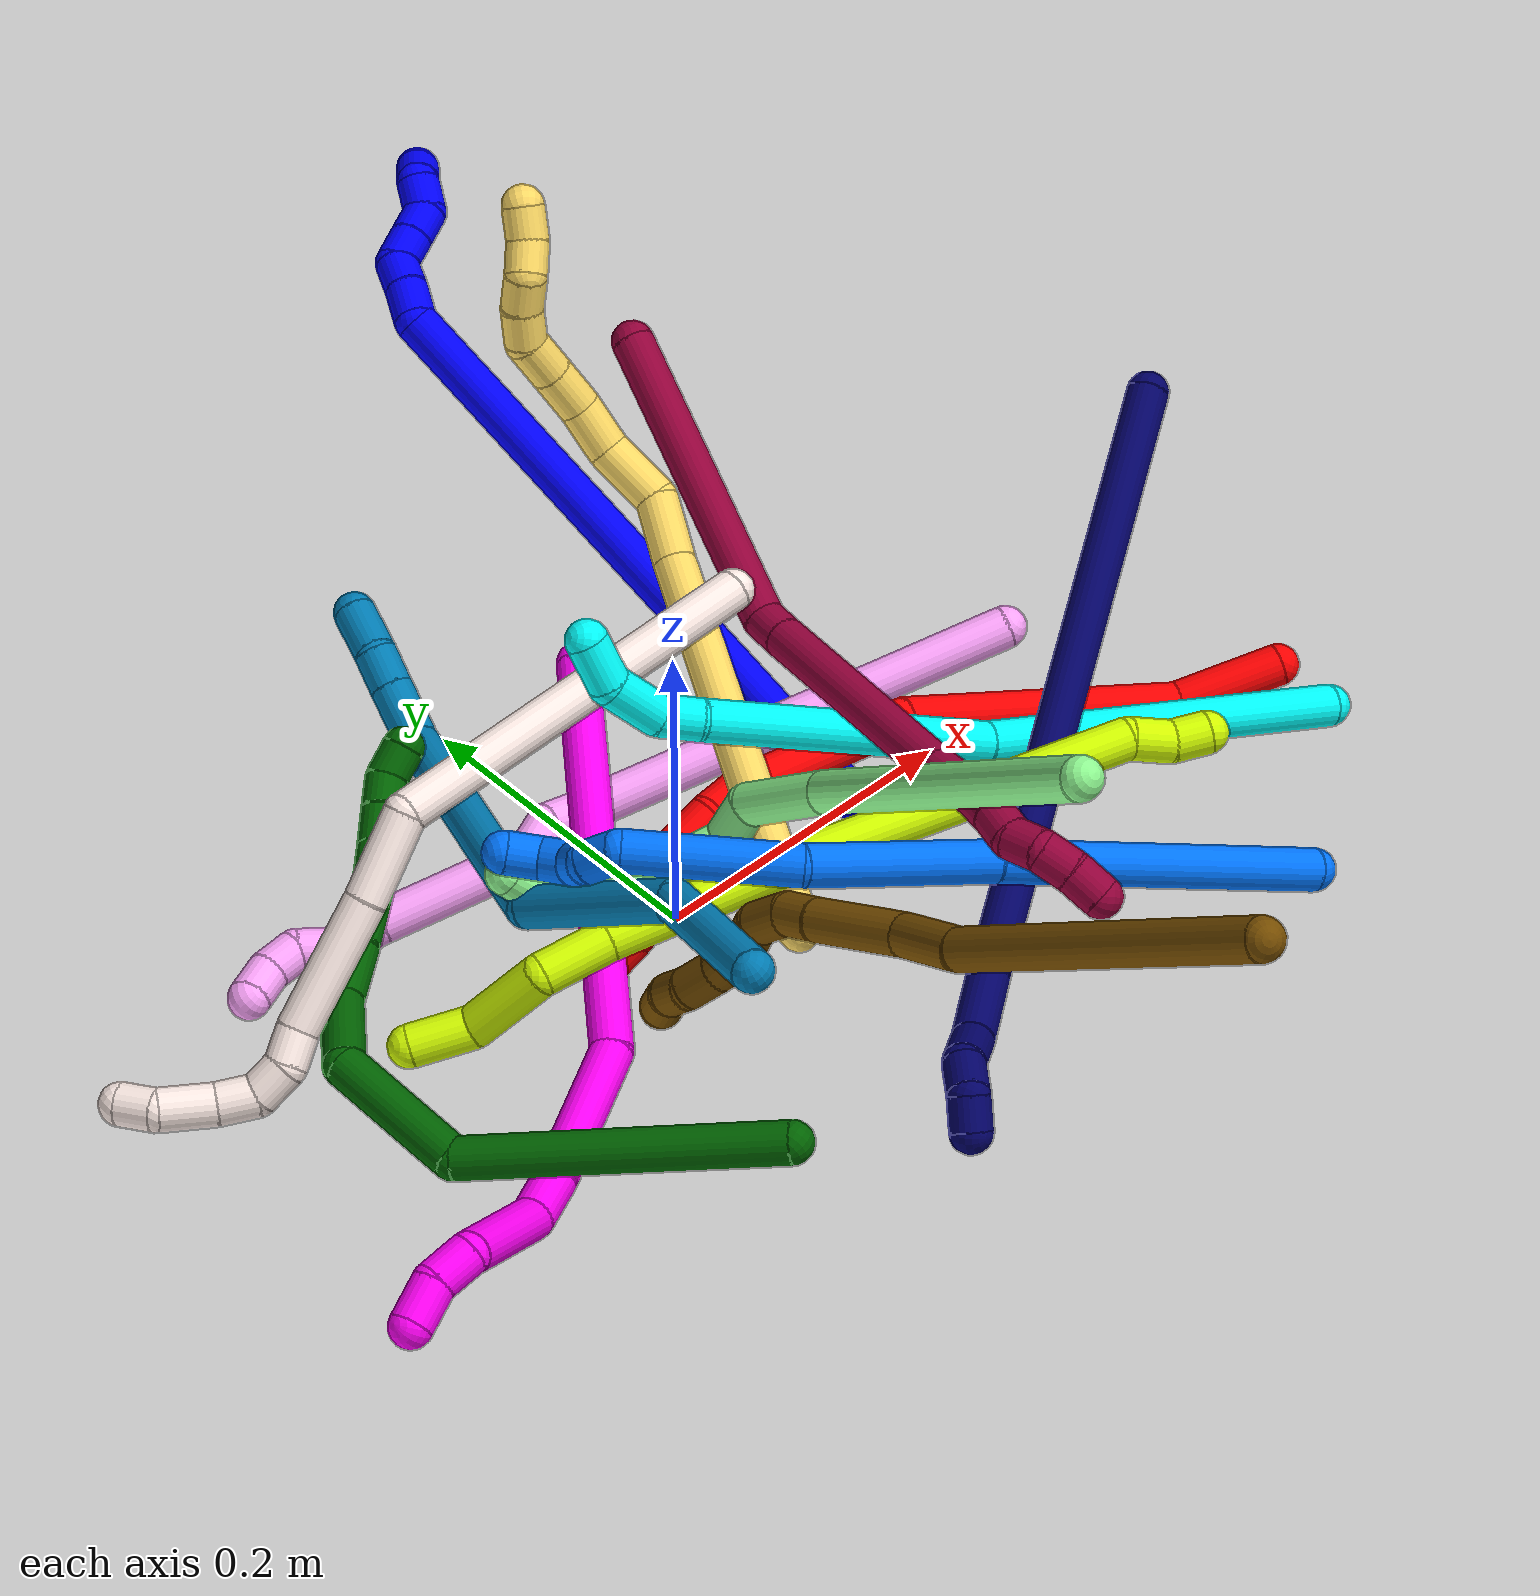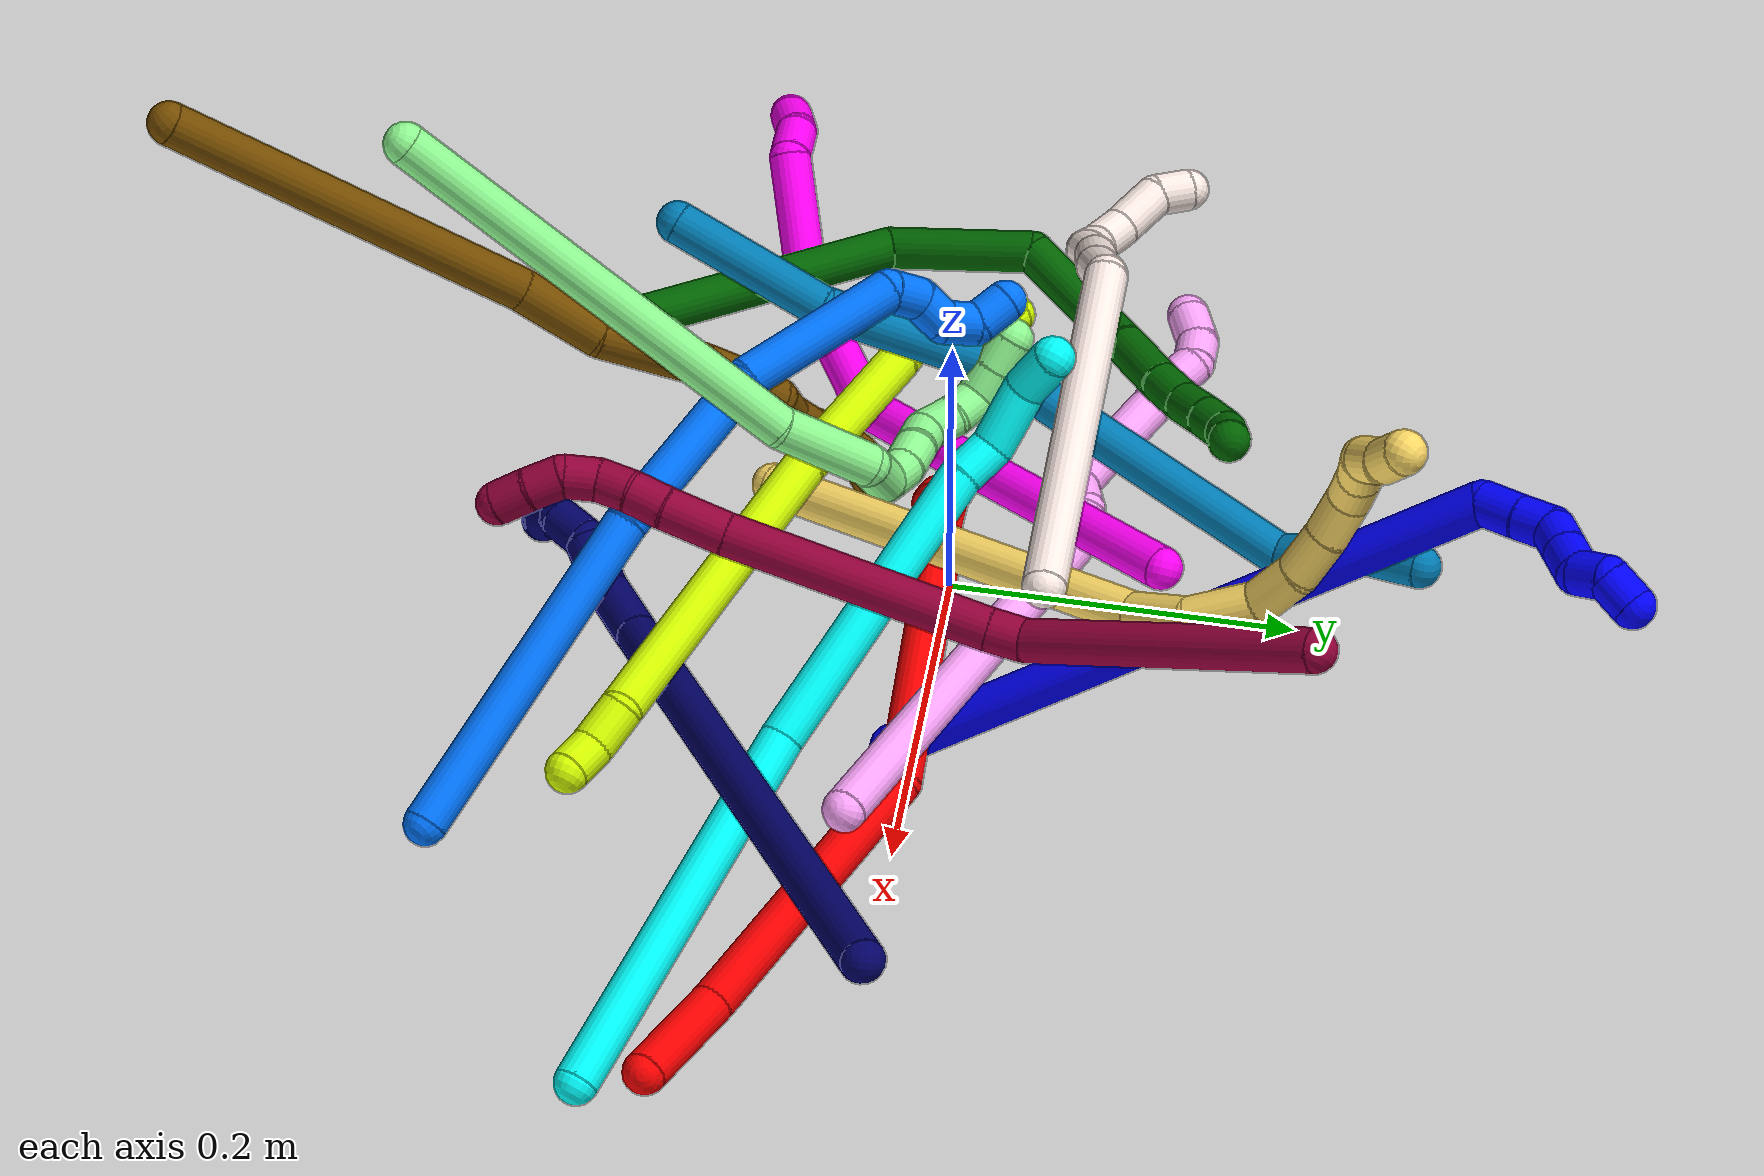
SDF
<sdf version="1.7">
 <world name="default">
  <plugin name="TubeGeneratorPlugin" filename="libtube_generator_plugin.so"/>
  <model name="photoneo_s_sensor">
   <static>1</static>
   <pose>0 0 2 1.57079 1.57079 3.14159</pose>
   <link name="link">
    <inertial><mass>0.1</mass></inertial>
    <sensor name="sensor" type="depth">
     <update_rate>30</update_rate>
     <camera>
      <horizontal_fov>1.22</horizontal_fov>
      <image><width>1920</width><height>1200</height><format>B8G8R8</format></image>
      <clip><near>0.1</near><far>4</far></clip>
      <depth_camera><output>points</output></depth_camera>
     </camera>
     <plugin name="camera_plugin" filename="libgazebo_ros_depth_camera.so">
      <baseline>0.2</baseline>
      <alwaysOn>1</alwaysOn>
      <updateRate>0.0</updateRate>
      <cameraName>camera_ir</cameraName>
      <imageTopicName>/camera/color/image_raw</imageTopicName>
      <cameraInfoTopicName>/camera/color/camera_info</cameraInfoTopicName>
      <depthImageTopicName>/camera/depth/image_raw</depthImageTopicName>
      <depthImageCameraInfoTopicName>/camera/depth/camera_info</depthImageCameraInfoTopicName>
      <pointCloudTopicName>/camera/depth/points</pointCloudTopicName>
      <frameName>fr_optical</frameName>
      <pointCloudCutoff>0.1</pointCloudCutoff>
      <pointCloudCutoffMax>2.0</pointCloudCutoffMax>
      <distortionK1>0</distortionK1>
      <distortionK2>0</distortionK2>
      <distortionK3>0</distortionK3>
      <distortionT1>0</distortionT1>
      <distortionT2>0</distortionT2>
      <CxPrime>0</CxPrime>
      <Cx>0</Cx>
      <Cy>0</Cy>
      <focalLength>0</focalLength>
      <hackBaseline>0</hackBaseline>
     </plugin>
    </sensor>
   </link>
  </model>
  <gravity>0 0 -9.8</gravity>
  <magnetic_field>6e-06 2.3e-05 -4.2e-05</magnetic_field>
  <atmosphere type="adiabatic"/>
  <physics name="default_physics" default="0" type="ode">
   <max_step_size>0.003</max_step_size>
   <real_time_factor>1</real_time_factor>
   <real_time_update_rate>1000</real_time_update_rate>
   <max_contacts>10000</max_contacts>
   <ode>
    <solver>
     <type>quick</type>
     <iters>100</iters>
     <sor>1.3</sor>
     <use_dynamic_moi_rescaling>0</use_dynamic_moi_rescaling>
    </solver>
    <constraints>
     <contact_max_correcting_vel>0</contact_max_correcting_vel>
     <contact_surface_layer>0.001</contact_surface_layer>
     <cfm>0</cfm>
     <erp>0.2</erp>
    </constraints>
   </ode>
  </physics>
  <scene><ambient>0.4 0.4 0.4 1</ambient><background>0.7 0.7 0.7 1</background><shadows>0</shadows></scene>
  <audio><device>default</device></audio>
  <spherical_coordinates>
   <surface_model>EARTH_WGS84</surface_model>
   <latitude_deg>0</latitude_deg>
   <longitude_deg>0</longitude_deg>
   <elevation>0</elevation>
   <heading_deg>0</heading_deg>
  </spherical_coordinates>
  <model name="bin">
   <static>1</static>
   <link name="bottom">
    <collision name="collision-bottom">
     <pose>0 0 -0.01 0 -0 0</pose>
     <geometry><box><size>0.8 0.6 0.02</size></box></geometry>
     <surface>
      <friction><ode><mu>100</mu><mu2>100</mu2></ode></friction>
      <contact><collide_bitmask>65535</collide_bitmask></contact>
     </surface>
    </collision>
   </link>
   <link name="west_wall">
    <collision name="collision-west_wall">
     <pose>-0.41 0 0.1 0 -0 0</pose>
     <geometry><box><size>0.02 0.6 0.2</size></box></geometry>
     <surface>
      <friction><ode><mu>100</mu><mu2>100</mu2></ode></friction>
      <contact><collide_bitmask>65535</collide_bitmask></contact>
     </surface>
    </collision>
   </link>
   <link name="east_wall">
    <collision name="collision-east_wall">
     <pose>0.41 0 0.1 0 -0 0</pose>
     <geometry><box><size>0.02 0.6 0.2</size></box></geometry>
     <surface>
      <friction><ode><mu>100</mu><mu2>100</mu2></ode></friction>
      <contact><collide_bitmask>65535</collide_bitmask></contact>
     </surface>
    </collision>
   </link>
   <link name="south_wall">
    <collision name="collision-south_wall">
     <pose>0 -0.31 0.1 0 -0 0</pose>
     <geometry><box><size>0.8 0.02 0.2</size></box></geometry>
     <surface>
      <friction><ode><mu>100</mu><mu2>100</mu2></ode></friction>
      <contact><collide_bitmask>65535</collide_bitmask></contact>
     </surface>
    </collision>
   </link>
   <link name="north_wall">
    <collision name="collision-north_wall">
     <pose>0 0.31 0.1 0 -0 0</pose>
     <geometry><box><size>0.8 0.02 0.2</size></box></geometry>
     <surface>
      <friction><ode><mu>100</mu><mu2>100</mu2></ode></friction>
      <contact><collide_bitmask>65535</collide_bitmask></contact>
     </surface>
    </collision>
   </link>
  </model>
  <model name="1">
   <static>0</static>
   <link name="1">
    <collision name="collision-cylinder-e_1_1_4">
     <pose>-0.029122 0.071616 0.17114 -0.396321 -0.155703 0.031325</pose>
     <geometry><cylinder><radius>0.0125</radius><length>0.375584</length></cylinder></geometry>
     <surface>
      <friction><ode><mu>1.16</mu><mu2>1.16</mu2><slip1>0</slip1><slip2>0</slip2></ode></friction>
      <contact><ode><kp>1e+06</kp><kd>1</kd><max_vel>0</max_vel><min_depth>0.001</min_depth></ode></contact>
     </surface>
    </collision>
    <visual name="visual-cylinder-e_1_1_4">
     <pose>-0.029122 0.071616 0.17114 -0.396321 -0.155703 0.031325</pose>
     <geometry><cylinder><radius>0.0125</radius><length>0.375584</length></cylinder></geometry>
     <material><ambient>0 0 1 1</ambient></material>
    </visual>
    <collision name="collision-cylinder-e_2_4_5">
     <pose>-0.051872 0.147866 0.35132 -0.473746 0.56021 -0.138666</pose>
     <geometry><cylinder><radius>0.0125</radius><length>0.023983</length></cylinder></geometry>
     <surface>
      <friction><ode><mu>1.16</mu><mu2>1.16</mu2><slip1>0</slip1><slip2>0</slip2></ode></friction>
      <contact><ode><kp>1e+06</kp><kd>1</kd><max_vel>0</max_vel><min_depth>0.001</min_depth></ode></contact>
     </surface>
    </collision>
    <visual name="visual-cylinder-e_2_4_5">
     <pose>-0.051872 0.147866 0.35132 -0.473746 0.56021 -0.138666</pose>
     <geometry><cylinder><radius>0.0125</radius><length>0.023983</length></cylinder></geometry>
     <material><ambient>0 0 1 1</ambient></material>
    </visual>
    <collision name="collision-cylinder-e_3_5_6">
     <pose>-0.040466 0.156999 0.367968 -0.533952 0.517734 -0.144601</pose>
     <geometry><cylinder><radius>0.0125</radius><length>0.020342</length></cylinder></geometry>
     <surface>
      <friction><ode><mu>1.16</mu><mu2>1.16</mu2><slip1>0</slip1><slip2>0</slip2></ode></friction>
      <contact><ode><kp>1e+06</kp><kd>1</kd><max_vel>0</max_vel><min_depth>0.001</min_depth></ode></contact>
     </surface>
    </collision>
    <visual name="visual-cylinder-e_3_5_6">
     <pose>-0.040466 0.156999 0.367968 -0.533952 0.517734 -0.144601</pose>
     <geometry><cylinder><radius>0.0125</radius><length>0.020342</length></cylinder></geometry>
     <material><ambient>0 0 1 1</ambient></material>
    </visual>
    <collision name="collision-cylinder-e_4_6_7">
     <pose>-0.027043 0.160234 0.380883 0.233717 0.994217 0.127213</pose>
     <geometry><cylinder><radius>0.0125</radius><length>0.020013</length></cylinder></geometry>
     <surface>
      <friction><ode><mu>1.16</mu><mu2>1.16</mu2><slip1>0</slip1><slip2>0</slip2></ode></friction>
      <contact><ode><kp>1e+06</kp><kd>1</kd><max_vel>0</max_vel><min_depth>0.001</min_depth></ode></contact>
     </surface>
    </collision>
    <visual name="visual-cylinder-e_4_6_7">
     <pose>-0.027043 0.160234 0.380883 0.233717 0.994217 0.127213</pose>
     <geometry><cylinder><radius>0.0125</radius><length>0.020013</length></cylinder></geometry>
     <material><ambient>0 0 1 1</ambient></material>
    </visual>
    <collision name="collision-cylinder-e_5_7_8">
     <pose>-0.01022 0.157763 0.391497 0.223665 0.99771 0.122215</pose>
     <geometry><cylinder><radius>0.0125</radius><length>0.020076</length></cylinder></geometry>
     <surface>
      <friction><ode><mu>1.16</mu><mu2>1.16</mu2><slip1>0</slip1><slip2>0</slip2></ode></friction>
      <contact><ode><kp>1e+06</kp><kd>1</kd><max_vel>0</max_vel><min_depth>0.001</min_depth></ode></contact>
     </surface>
    </collision>
    <visual name="visual-cylinder-e_5_7_8">
     <pose>-0.01022 0.157763 0.391497 0.223665 0.99771 0.122215</pose>
     <geometry><cylinder><radius>0.0125</radius><length>0.020076</length></cylinder></geometry>
     <material><ambient>0 0 1 1</ambient></material>
    </visual>
    <collision name="collision-cylinder-e_6_8_9">
     <pose>0.002382 0.158829 0.405605 -0.252726 0.429925 -0.05546</pose>
     <geometry><cylinder><radius>0.0125</radius><length>0.02</length></cylinder></geometry>
     <surface>
      <friction><ode><mu>1.16</mu><mu2>1.16</mu2><slip1>0</slip1><slip2>0</slip2></ode></friction>
      <contact><ode><kp>1e+06</kp><kd>1</kd><max_vel>0</max_vel><min_depth>0.001</min_depth></ode></contact>
     </surface>
    </collision>
    <visual name="visual-cylinder-e_6_8_9">
     <pose>0.002382 0.158829 0.405605 -0.252726 0.429925 -0.05546</pose>
     <geometry><cylinder><radius>0.0125</radius><length>0.02</length></cylinder></geometry>
     <material><ambient>0 0 1 1</ambient></material>
    </visual>
    <collision name="collision-cylinder-e_7_9_2">
     <pose>0.014505 0.166168 0.417732 -0.989965 0.919797 -0.522532</pose>
     <geometry><cylinder><radius>0.0125</radius><length>0.020001</length></cylinder></geometry>
     <surface>
      <friction><ode><mu>1.16</mu><mu2>1.16</mu2><slip1>0</slip1><slip2>0</slip2></ode></friction>
      <contact><ode><kp>1e+06</kp><kd>1</kd><max_vel>0</max_vel><min_depth>0.001</min_depth></ode></contact>
     </surface>
    </collision>
    <visual name="visual-cylinder-e_7_9_2">
     <pose>0.014505 0.166168 0.417732 -0.989965 0.919797 -0.522532</pose>
     <geometry><cylinder><radius>0.0125</radius><length>0.020001</length></cylinder></geometry>
     <material><ambient>0 0 1 1</ambient></material>
    </visual>
    <collision name="collision-sphere-2">
     <pose>0.02246 0.171234 0.421057 0 -0 0</pose>
     <geometry><sphere><radius>0.0125</radius></sphere></geometry>
     <surface>
      <friction><ode><mu>1.16</mu><mu2>1.16</mu2><slip1>0</slip1><slip2>0</slip2></ode></friction>
      <contact><ode><kp>1e+06</kp><kd>1</kd><max_vel>0</max_vel><min_depth>0.001</min_depth></ode></contact>
     </surface>
    </collision>
    <visual name="visual-sphere-2">
     <pose>0.02246 0.171234 0.421057 0 -0 0</pose>
     <geometry><sphere><radius>0.0125</radius></sphere></geometry>
     <material><ambient>0 0 1 1</ambient></material>
    </visual>
    <collision name="collision-sphere-9">
     <pose>0.00655 0.161102 0.414407 0 -0 0</pose>
     <geometry><sphere><radius>0.0125</radius></sphere></geometry>
     <surface>
      <friction><ode><mu>1.16</mu><mu2>1.16</mu2><slip1>0</slip1><slip2>0</slip2></ode></friction>
      <contact><ode><kp>1e+06</kp><kd>1</kd><max_vel>0</max_vel><min_depth>0.001</min_depth></ode></contact>
     </surface>
    </collision>
    <visual name="visual-sphere-9">
     <pose>0.00655 0.161102 0.414407 0 -0 0</pose>
     <geometry><sphere><radius>0.0125</radius></sphere></geometry>
     <material><ambient>0 0 1 1</ambient></material>
    </visual>
    <collision name="collision-sphere-4">
     <pose>-0.058244 0.143232 0.34228 0 -0 0</pose>
     <geometry><sphere><radius>0.0125</radius></sphere></geometry>
     <surface>
      <friction><ode><mu>1.16</mu><mu2>1.16</mu2><slip1>0</slip1><slip2>0</slip2></ode></friction>
      <contact><ode><kp>1e+06</kp><kd>1</kd><max_vel>0</max_vel><min_depth>0.001</min_depth></ode></contact>
     </surface>
    </collision>
    <visual name="visual-sphere-4">
     <pose>-0.058244 0.143232 0.34228 0 -0 0</pose>
     <geometry><sphere><radius>0.0125</radius></sphere></geometry>
     <material><ambient>0 0 1 1</ambient></material>
    </visual>
    <collision name="collision-sphere-1">
     <geometry><sphere><radius>0.0125</radius></sphere></geometry>
     <surface>
      <friction><ode><mu>1.16</mu><mu2>1.16</mu2><slip1>0</slip1><slip2>0</slip2></ode></friction>
      <contact><ode><kp>1e+06</kp><kd>1</kd><max_vel>0</max_vel><min_depth>0.001</min_depth></ode></contact>
     </surface>
    </collision>
    <visual name="visual-sphere-1">
     <geometry><sphere><radius>0.0125</radius></sphere></geometry>
     <material><ambient>0 0 1 1</ambient></material>
    </visual>
    <collision name="collision-sphere-8">
     <pose>-0.001786 0.156556 0.396804 0 -0 0</pose>
     <geometry><sphere><radius>0.0125</radius></sphere></geometry>
     <surface>
      <friction><ode><mu>1.16</mu><mu2>1.16</mu2><slip1>0</slip1><slip2>0</slip2></ode></friction>
      <contact><ode><kp>1e+06</kp><kd>1</kd><max_vel>0</max_vel><min_depth>0.001</min_depth></ode></contact>
     </surface>
    </collision>
    <visual name="visual-sphere-8">
     <pose>-0.001786 0.156556 0.396804 0 -0 0</pose>
     <geometry><sphere><radius>0.0125</radius></sphere></geometry>
     <material><ambient>0 0 1 1</ambient></material>
    </visual>
    <collision name="collision-sphere-5">
     <pose>-0.0455 0.152501 0.36036 0 -0 0</pose>
     <geometry><sphere><radius>0.0125</radius></sphere></geometry>
     <surface>
      <friction><ode><mu>1.16</mu><mu2>1.16</mu2><slip1>0</slip1><slip2>0</slip2></ode></friction>
      <contact><ode><kp>1e+06</kp><kd>1</kd><max_vel>0</max_vel><min_depth>0.001</min_depth></ode></contact>
     </surface>
    </collision>
    <visual name="visual-sphere-5">
     <pose>-0.0455 0.152501 0.36036 0 -0 0</pose>
     <geometry><sphere><radius>0.0125</radius></sphere></geometry>
     <material><ambient>0 0 1 1</ambient></material>
    </visual>
    <collision name="collision-sphere-6">
     <pose>-0.035432 0.161497 0.375576 0 -0 0</pose>
     <geometry><sphere><radius>0.0125</radius></sphere></geometry>
     <surface>
      <friction><ode><mu>1.16</mu><mu2>1.16</mu2><slip1>0</slip1><slip2>0</slip2></ode></friction>
      <contact><ode><kp>1e+06</kp><kd>1</kd><max_vel>0</max_vel><min_depth>0.001</min_depth></ode></contact>
     </surface>
    </collision>
    <visual name="visual-sphere-6">
     <pose>-0.035432 0.161497 0.375576 0 -0 0</pose>
     <geometry><sphere><radius>0.0125</radius></sphere></geometry>
     <material><ambient>0 0 1 1</ambient></material>
    </visual>
    <collision name="collision-sphere-7">
     <pose>-0.018654 0.15897 0.386189 0 -0 0</pose>
     <geometry><sphere><radius>0.0125</radius></sphere></geometry>
     <surface>
      <friction><ode><mu>1.16</mu><mu2>1.16</mu2><slip1>0</slip1><slip2>0</slip2></ode></friction>
      <contact><ode><kp>1e+06</kp><kd>1</kd><max_vel>0</max_vel><min_depth>0.001</min_depth></ode></contact>
     </surface>
    </collision>
    <visual name="visual-sphere-7">
     <pose>-0.018654 0.15897 0.386189 0 -0 0</pose>
     <geometry><sphere><radius>0.0125</radius></sphere></geometry>
     <material><ambient>0 0 1 1</ambient></material>
    </visual>
    <inertial>
     <pose>-0.026827 0.093024 0.224276 0 -0 0</pose>
     <mass>0.5</mass>
     <inertia>
      <ixx>0.004519</ixx>
      <ixy>0</ixy>
      <ixz>0</ixz>
      <iyy>0.004251</iyy>
      <iyz>0</iyz>
      <izz>-0.000978</izz>
     </inertia>
    </inertial>
   </link>
   <pose>0.131621 -0.011443 0.011493 -0.62536 0.317059 0.197017</pose>
  </model>
  <model name="2">
   <static>0</static>
   <link name="2">
    <collision name="collision-cylinder-e_1_1_4">
     <pose>-0.02005 0.011389 -0.022699 -2.67653 -0.668301 1.94434</pose>
     <geometry><cylinder><radius>0.0125</radius><length>0.064714</length></cylinder></geometry>
     <surface>
      <friction><ode><mu>1.16</mu><mu2>1.16</mu2><slip1>0</slip1><slip2>0</slip2></ode></friction>
      <contact><ode><kp>1e+06</kp><kd>1</kd><max_vel>0</max_vel><min_depth>0.001</min_depth></ode></contact>
     </surface>
    </collision>
    <visual name="visual-cylinder-e_1_1_4">
     <pose>-0.02005 0.011389 -0.022699 -2.67653 -0.668301 1.94434</pose>
     <geometry><cylinder><radius>0.0125</radius><length>0.064714</length></cylinder></geometry>
     <material><ambient>1 0 0 1</ambient></material>
    </visual>
    <collision name="collision-cylinder-e_2_4_5">
     <pose>-0.108999 0.053602 -0.081719 -2.4379 -0.965869 1.91994</pose>
     <geometry><cylinder><radius>0.0125</radius><length>0.167527</length></cylinder></geometry>
     <surface>
      <friction><ode><mu>1.16</mu><mu2>1.16</mu2><slip1>0</slip1><slip2>0</slip2></ode></friction>
      <contact><ode><kp>1e+06</kp><kd>1</kd><max_vel>0</max_vel><min_depth>0.001</min_depth></ode></contact>
     </surface>
    </collision>
    <visual name="visual-cylinder-e_2_4_5">
     <pose>-0.108999 0.053602 -0.081719 -2.4379 -0.965869 1.91994</pose>
     <geometry><cylinder><radius>0.0125</radius><length>0.167527</length></cylinder></geometry>
     <material><ambient>1 0 0 1</ambient></material>
    </visual>
    <collision name="collision-cylinder-e_3_5_6">
     <pose>-0.234221 0.07686 -0.151537 2.91949 -1.02326 -2.74952</pose>
     <geometry><cylinder><radius>0.0125</radius><length>0.131933</length></cylinder></geometry>
     <surface>
      <friction><ode><mu>1.16</mu><mu2>1.16</mu2><slip1>0</slip1><slip2>0</slip2></ode></friction>
      <contact><ode><kp>1e+06</kp><kd>1</kd><max_vel>0</max_vel><min_depth>0.001</min_depth></ode></contact>
     </surface>
    </collision>
    <visual name="visual-cylinder-e_3_5_6">
     <pose>-0.234221 0.07686 -0.151537 2.91949 -1.02326 -2.74952</pose>
     <geometry><cylinder><radius>0.0125</radius><length>0.131933</length></cylinder></geometry>
     <material><ambient>1 0 0 1</ambient></material>
    </visual>
    <collision name="collision-cylinder-e_4_6_7">
     <pose>-0.300809 0.066452 -0.194736 2.85653 -0.793043 -2.48121</pose>
     <geometry><cylinder><radius>0.0125</radius><length>0.028814</length></cylinder></geometry>
     <surface>
      <friction><ode><mu>1.16</mu><mu2>1.16</mu2><slip1>0</slip1><slip2>0</slip2></ode></friction>
      <contact><ode><kp>1e+06</kp><kd>1</kd><max_vel>0</max_vel><min_depth>0.001</min_depth></ode></contact>
     </surface>
    </collision>
    <visual name="visual-cylinder-e_4_6_7">
     <pose>-0.300809 0.066452 -0.194736 2.85653 -0.793043 -2.48121</pose>
     <geometry><cylinder><radius>0.0125</radius><length>0.028814</length></cylinder></geometry>
     <material><ambient>1 0 0 1</ambient></material>
    </visual>
    <collision name="collision-cylinder-e_5_7_8">
     <pose>-0.319236 0.063138 -0.219858 3.111 -0.486589 -3.01848</pose>
     <geometry><cylinder><radius>0.0125</radius><length>0.034908</length></cylinder></geometry>
     <surface>
      <friction><ode><mu>1.16</mu><mu2>1.16</mu2><slip1>0</slip1><slip2>0</slip2></ode></friction>
      <contact><ode><kp>1e+06</kp><kd>1</kd><max_vel>0</max_vel><min_depth>0.001</min_depth></ode></contact>
     </surface>
    </collision>
    <visual name="visual-cylinder-e_5_7_8">
     <pose>-0.319236 0.063138 -0.219858 3.111 -0.486589 -3.01848</pose>
     <geometry><cylinder><radius>0.0125</radius><length>0.034908</length></cylinder></geometry>
     <material><ambient>1 0 0 1</ambient></material>
    </visual>
    <collision name="collision-cylinder-e_6_8_9">
     <pose>-0.325604 0.059287 -0.24752 2.8723 0.140267 0.956785</pose>
     <geometry><cylinder><radius>0.0125</radius><length>0.025649</length></cylinder></geometry>
     <surface>
      <friction><ode><mu>1.16</mu><mu2>1.16</mu2><slip1>0</slip1><slip2>0</slip2></ode></friction>
      <contact><ode><kp>1e+06</kp><kd>1</kd><max_vel>0</max_vel><min_depth>0.001</min_depth></ode></contact>
     </surface>
    </collision>
    <visual name="visual-cylinder-e_6_8_9">
     <pose>-0.325604 0.059287 -0.24752 2.8723 0.140267 0.956785</pose>
     <geometry><cylinder><radius>0.0125</radius><length>0.025649</length></cylinder></geometry>
     <material><ambient>1 0 0 1</ambient></material>
    </visual>
    <collision name="collision-cylinder-e_7_9_10">
     <pose>-0.325827 0.056908 -0.270953 -3.05254 -0.177504 2.21315</pose>
     <geometry><cylinder><radius>0.0125</radius><length>0.022834</length></cylinder></geometry>
     <surface>
      <friction><ode><mu>1.16</mu><mu2>1.16</mu2><slip1>0</slip1><slip2>0</slip2></ode></friction>
      <contact><ode><kp>1e+06</kp><kd>1</kd><max_vel>0</max_vel><min_depth>0.001</min_depth></ode></contact>
     </surface>
    </collision>
    <visual name="visual-cylinder-e_7_9_10">
     <pose>-0.325827 0.056908 -0.270953 -3.05254 -0.177504 2.21315</pose>
     <geometry><cylinder><radius>0.0125</radius><length>0.022834</length></cylinder></geometry>
     <material><ambient>1 0 0 1</ambient></material>
    </visual>
    <collision name="collision-cylinder-e_8_10_2">
     <pose>-0.329557 0.060968 -0.293424 -2.87666 -0.145616 1.00166</pose>
     <geometry><cylinder><radius>0.0125</radius><length>0.023622</length></cylinder></geometry>
     <surface>
      <friction><ode><mu>1.16</mu><mu2>1.16</mu2><slip1>0</slip1><slip2>0</slip2></ode></friction>
      <contact><ode><kp>1e+06</kp><kd>1</kd><max_vel>0</max_vel><min_depth>0.001</min_depth></ode></contact>
     </surface>
    </collision>
    <visual name="visual-cylinder-e_8_10_2">
     <pose>-0.329557 0.060968 -0.293424 -2.87666 -0.145616 1.00166</pose>
     <geometry><cylinder><radius>0.0125</radius><length>0.023622</length></cylinder></geometry>
     <material><ambient>1 0 0 1</ambient></material>
    </visual>
    <collision name="collision-sphere-2">
     <pose>-0.331271 0.064028 -0.304703 0 -0 0</pose>
     <geometry><sphere><radius>0.0125</radius></sphere></geometry>
     <surface>
      <friction><ode><mu>1.16</mu><mu2>1.16</mu2><slip1>0</slip1><slip2>0</slip2></ode></friction>
      <contact><ode><kp>1e+06</kp><kd>1</kd><max_vel>0</max_vel><min_depth>0.001</min_depth></ode></contact>
     </surface>
    </collision>
    <visual name="visual-sphere-2">
     <pose>-0.331271 0.064028 -0.304703 0 -0 0</pose>
     <geometry><sphere><radius>0.0125</radius></sphere></geometry>
     <material><ambient>1 0 0 1</ambient></material>
    </visual>
    <collision name="collision-sphere-10">
     <pose>-0.327843 0.057908 -0.282146 0 -0 0</pose>
     <geometry><sphere><radius>0.0125</radius></sphere></geometry>
     <surface>
      <friction><ode><mu>1.16</mu><mu2>1.16</mu2><slip1>0</slip1><slip2>0</slip2></ode></friction>
      <contact><ode><kp>1e+06</kp><kd>1</kd><max_vel>0</max_vel><min_depth>0.001</min_depth></ode></contact>
     </surface>
    </collision>
    <visual name="visual-sphere-10">
     <pose>-0.327843 0.057908 -0.282146 0 -0 0</pose>
     <geometry><sphere><radius>0.0125</radius></sphere></geometry>
     <material><ambient>1 0 0 1</ambient></material>
    </visual>
    <collision name="collision-sphere-9">
     <pose>-0.323811 0.055909 -0.25976 0 -0 0</pose>
     <geometry><sphere><radius>0.0125</radius></sphere></geometry>
     <surface>
      <friction><ode><mu>1.16</mu><mu2>1.16</mu2><slip1>0</slip1><slip2>0</slip2></ode></friction>
      <contact><ode><kp>1e+06</kp><kd>1</kd><max_vel>0</max_vel><min_depth>0.001</min_depth></ode></contact>
     </surface>
    </collision>
    <visual name="visual-sphere-9">
     <pose>-0.323811 0.055909 -0.25976 0 -0 0</pose>
     <geometry><sphere><radius>0.0125</radius></sphere></geometry>
     <material><ambient>1 0 0 1</ambient></material>
    </visual>
    <collision name="collision-sphere-4">
     <pose>-0.0401 0.022779 -0.045398 0 -0 0</pose>
     <geometry><sphere><radius>0.0125</radius></sphere></geometry>
     <surface>
      <friction><ode><mu>1.16</mu><mu2>1.16</mu2><slip1>0</slip1><slip2>0</slip2></ode></friction>
      <contact><ode><kp>1e+06</kp><kd>1</kd><max_vel>0</max_vel><min_depth>0.001</min_depth></ode></contact>
     </surface>
    </collision>
    <visual name="visual-sphere-4">
     <pose>-0.0401 0.022779 -0.045398 0 -0 0</pose>
     <geometry><sphere><radius>0.0125</radius></sphere></geometry>
     <material><ambient>1 0 0 1</ambient></material>
    </visual>
    <collision name="collision-sphere-1">
     <geometry><sphere><radius>0.0125</radius></sphere></geometry>
     <surface>
      <friction><ode><mu>1.16</mu><mu2>1.16</mu2><slip1>0</slip1><slip2>0</slip2></ode></friction>
      <contact><ode><kp>1e+06</kp><kd>1</kd><max_vel>0</max_vel><min_depth>0.001</min_depth></ode></contact>
     </surface>
    </collision>
    <visual name="visual-sphere-1">
     <geometry><sphere><radius>0.0125</radius></sphere></geometry>
     <material><ambient>1 0 0 1</ambient></material>
    </visual>
    <collision name="collision-sphere-8">
     <pose>-0.327397 0.062666 -0.235279 0 -0 0</pose>
     <geometry><sphere><radius>0.0125</radius></sphere></geometry>
     <surface>
      <friction><ode><mu>1.16</mu><mu2>1.16</mu2><slip1>0</slip1><slip2>0</slip2></ode></friction>
      <contact><ode><kp>1e+06</kp><kd>1</kd><max_vel>0</max_vel><min_depth>0.001</min_depth></ode></contact>
     </surface>
    </collision>
    <visual name="visual-sphere-8">
     <pose>-0.327397 0.062666 -0.235279 0 -0 0</pose>
     <geometry><sphere><radius>0.0125</radius></sphere></geometry>
     <material><ambient>1 0 0 1</ambient></material>
    </visual>
    <collision name="collision-sphere-5">
     <pose>-0.177899 0.084424 -0.11804 0 -0 0</pose>
     <geometry><sphere><radius>0.0125</radius></sphere></geometry>
     <surface>
      <friction><ode><mu>1.16</mu><mu2>1.16</mu2><slip1>0</slip1><slip2>0</slip2></ode></friction>
      <contact><ode><kp>1e+06</kp><kd>1</kd><max_vel>0</max_vel><min_depth>0.001</min_depth></ode></contact>
     </surface>
    </collision>
    <visual name="visual-sphere-5">
     <pose>-0.177899 0.084424 -0.11804 0 -0 0</pose>
     <geometry><sphere><radius>0.0125</radius></sphere></geometry>
     <material><ambient>1 0 0 1</ambient></material>
    </visual>
    <collision name="collision-sphere-6">
     <pose>-0.290544 0.069295 -0.185035 0 -0 0</pose>
     <geometry><sphere><radius>0.0125</radius></sphere></geometry>
     <surface>
      <friction><ode><mu>1.16</mu><mu2>1.16</mu2><slip1>0</slip1><slip2>0</slip2></ode></friction>
      <contact><ode><kp>1e+06</kp><kd>1</kd><max_vel>0</max_vel><min_depth>0.001</min_depth></ode></contact>
     </surface>
    </collision>
    <visual name="visual-sphere-6">
     <pose>-0.290544 0.069295 -0.185035 0 -0 0</pose>
     <geometry><sphere><radius>0.0125</radius></sphere></geometry>
     <material><ambient>1 0 0 1</ambient></material>
    </visual>
    <collision name="collision-sphere-7">
     <pose>-0.311074 0.06361 -0.204437 0 -0 0</pose>
     <geometry><sphere><radius>0.0125</radius></sphere></geometry>
     <surface>
      <friction><ode><mu>1.16</mu><mu2>1.16</mu2><slip1>0</slip1><slip2>0</slip2></ode></friction>
      <contact><ode><kp>1e+06</kp><kd>1</kd><max_vel>0</max_vel><min_depth>0.001</min_depth></ode></contact>
     </surface>
    </collision>
    <visual name="visual-sphere-7">
     <pose>-0.311074 0.06361 -0.204437 0 -0 0</pose>
     <geometry><sphere><radius>0.0125</radius></sphere></geometry>
     <material><ambient>1 0 0 1</ambient></material>
    </visual>
    <inertial>
     <pose>-0.187693 0.056472 -0.135809 0 -0 0</pose>
     <mass>0.5</mass>
     <inertia>
      <ixx>-1.4e-05</ixx>
      <ixy>0</ixy>
      <ixz>0</ixz>
      <iyy>0.000716</iyy>
      <iyz>0</iyz>
      <izz>0.00036</izz>
     </inertia>
    </inertial>
   </link>
   <pose>0.383248 -0.102731 0.022092 -0.256168 0.730458 -0.24162</pose>
  </model>
  <model name="3">
   <static>0</static>
   <link name="3">
    <collision name="collision-cylinder-e_1_1_4">
     <pose>-0.005533 0.022938 -0.111422 -2.93856 -0.048604 0.468479</pose>
     <geometry><cylinder><radius>0.0125</radius><length>0.227787</length></cylinder></geometry>
     <surface>
      <friction><ode><mu>1.16</mu><mu2>1.16</mu2><slip1>0</slip1><slip2>0</slip2></ode></friction>
      <contact><ode><kp>1e+06</kp><kd>1</kd><max_vel>0</max_vel><min_depth>0.001</min_depth></ode></contact>
     </surface>
    </collision>
    <visual name="visual-cylinder-e_1_1_4">
     <pose>-0.005533 0.022938 -0.111422 -2.93856 -0.048604 0.468479</pose>
     <geometry><cylinder><radius>0.0125</radius><length>0.227787</length></cylinder></geometry>
     <material><ambient>0.003922 1 0.996078 1</ambient></material>
    </visual>
    <collision name="collision-cylinder-e_2_4_5">
     <pose>-0.020483 0.050111 -0.312323 -3.09429 -0.104724 2.29371</pose>
     <geometry><cylinder><radius>0.0125</radius><length>0.180144</length></cylinder></geometry>
     <surface>
      <friction><ode><mu>1.16</mu><mu2>1.16</mu2><slip1>0</slip1><slip2>0</slip2></ode></friction>
      <contact><ode><kp>1e+06</kp><kd>1</kd><max_vel>0</max_vel><min_depth>0.001</min_depth></ode></contact>
     </surface>
    </collision>
    <visual name="visual-cylinder-e_2_4_5">
     <pose>-0.020483 0.050111 -0.312323 -3.09429 -0.104724 2.29371</pose>
     <geometry><cylinder><radius>0.0125</radius><length>0.180144</length></cylinder></geometry>
     <material><ambient>0.003922 1 0.996078 1</ambient></material>
    </visual>
    <collision name="collision-cylinder-e_3_5_6">
     <pose>-0.03383 0.055245 -0.413611 -3.06562 -0.320509 2.67977</pose>
     <geometry><cylinder><radius>0.0125</radius><length>0.024959</length></cylinder></geometry>
     <surface>
      <friction><ode><mu>1.16</mu><mu2>1.16</mu2><slip1>0</slip1><slip2>0</slip2></ode></friction>
      <contact><ode><kp>1e+06</kp><kd>1</kd><max_vel>0</max_vel><min_depth>0.001</min_depth></ode></contact>
     </surface>
    </collision>
    <visual name="visual-cylinder-e_3_5_6">
     <pose>-0.03383 0.055245 -0.413611 -3.06562 -0.320509 2.67977</pose>
     <geometry><cylinder><radius>0.0125</radius><length>0.024959</length></cylinder></geometry>
     <material><ambient>0.003922 1 0.996078 1</ambient></material>
    </visual>
    <collision name="collision-cylinder-e_4_6_7">
     <pose>-0.037759 0.048769 -0.443179 2.74794 0.000119 0.000598</pose>
     <geometry><cylinder><radius>0.0125</radius><length>0.038456</length></cylinder></geometry>
     <surface>
      <friction><ode><mu>1.16</mu><mu2>1.16</mu2><slip1>0</slip1><slip2>0</slip2></ode></friction>
      <contact><ode><kp>1e+06</kp><kd>1</kd><max_vel>0</max_vel><min_depth>0.001</min_depth></ode></contact>
     </surface>
    </collision>
    <visual name="visual-cylinder-e_4_6_7">
     <pose>-0.037759 0.048769 -0.443179 2.74794 0.000119 0.000598</pose>
     <geometry><cylinder><radius>0.0125</radius><length>0.038456</length></cylinder></geometry>
     <material><ambient>0.003922 1 0.996078 1</ambient></material>
    </visual>
    <collision name="collision-cylinder-e_5_7_2">
     <pose>-0.040252 0.030358 -0.469725 2.24329 -0.175051 -0.360158</pose>
     <geometry><cylinder><radius>0.0125</radius><length>0.028654</length></cylinder></geometry>
     <surface>
      <friction><ode><mu>1.16</mu><mu2>1.16</mu2><slip1>0</slip1><slip2>0</slip2></ode></friction>
      <contact><ode><kp>1e+06</kp><kd>1</kd><max_vel>0</max_vel><min_depth>0.001</min_depth></ode></contact>
     </surface>
    </collision>
    <visual name="visual-cylinder-e_5_7_2">
     <pose>-0.040252 0.030358 -0.469725 2.24329 -0.175051 -0.360158</pose>
     <geometry><cylinder><radius>0.0125</radius><length>0.028654</length></cylinder></geometry>
     <material><ambient>0.003922 1 0.996078 1</ambient></material>
    </visual>
    <collision name="collision-sphere-2">
     <pose>-0.042747 0.019322 -0.478513 0 -0 0</pose>
     <geometry><sphere><radius>0.0125</radius></sphere></geometry>
     <surface>
      <friction><ode><mu>1.16</mu><mu2>1.16</mu2><slip1>0</slip1><slip2>0</slip2></ode></friction>
      <contact><ode><kp>1e+06</kp><kd>1</kd><max_vel>0</max_vel><min_depth>0.001</min_depth></ode></contact>
     </surface>
    </collision>
    <visual name="visual-sphere-2">
     <pose>-0.042747 0.019322 -0.478513 0 -0 0</pose>
     <geometry><sphere><radius>0.0125</radius></sphere></geometry>
     <material><ambient>0.003922 1 0.996078 1</ambient></material>
    </visual>
    <collision name="collision-sphere-7">
     <pose>-0.037757 0.041394 -0.460936 0 -0 0</pose>
     <geometry><sphere><radius>0.0125</radius></sphere></geometry>
     <surface>
      <friction><ode><mu>1.16</mu><mu2>1.16</mu2><slip1>0</slip1><slip2>0</slip2></ode></friction>
      <contact><ode><kp>1e+06</kp><kd>1</kd><max_vel>0</max_vel><min_depth>0.001</min_depth></ode></contact>
     </surface>
    </collision>
    <visual name="visual-sphere-7">
     <pose>-0.037757 0.041394 -0.460936 0 -0 0</pose>
     <geometry><sphere><radius>0.0125</radius></sphere></geometry>
     <material><ambient>0.003922 1 0.996078 1</ambient></material>
    </visual>
    <collision name="collision-sphere-6">
     <pose>-0.037761 0.056144 -0.425421 0 -0 0</pose>
     <geometry><sphere><radius>0.0125</radius></sphere></geometry>
     <surface>
      <friction><ode><mu>1.16</mu><mu2>1.16</mu2><slip1>0</slip1><slip2>0</slip2></ode></friction>
      <contact><ode><kp>1e+06</kp><kd>1</kd><max_vel>0</max_vel><min_depth>0.001</min_depth></ode></contact>
     </surface>
    </collision>
    <visual name="visual-sphere-6">
     <pose>-0.037761 0.056144 -0.425421 0 -0 0</pose>
     <geometry><sphere><radius>0.0125</radius></sphere></geometry>
     <material><ambient>0.003922 1 0.996078 1</ambient></material>
    </visual>
    <collision name="collision-sphere-5">
     <pose>-0.029898 0.054346 -0.401801 0 -0 0</pose>
     <geometry><sphere><radius>0.0125</radius></sphere></geometry>
     <surface>
      <friction><ode><mu>1.16</mu><mu2>1.16</mu2><slip1>0</slip1><slip2>0</slip2></ode></friction>
      <contact><ode><kp>1e+06</kp><kd>1</kd><max_vel>0</max_vel><min_depth>0.001</min_depth></ode></contact>
     </surface>
    </collision>
    <visual name="visual-sphere-5">
     <pose>-0.029898 0.054346 -0.401801 0 -0 0</pose>
     <geometry><sphere><radius>0.0125</radius></sphere></geometry>
     <material><ambient>0.003922 1 0.996078 1</ambient></material>
    </visual>
    <collision name="collision-sphere-1">
     <geometry><sphere><radius>0.0125</radius></sphere></geometry>
     <surface>
      <friction><ode><mu>1.16</mu><mu2>1.16</mu2><slip1>0</slip1><slip2>0</slip2></ode></friction>
      <contact><ode><kp>1e+06</kp><kd>1</kd><max_vel>0</max_vel><min_depth>0.001</min_depth></ode></contact>
     </surface>
    </collision>
    <visual name="visual-sphere-1">
     <geometry><sphere><radius>0.0125</radius></sphere></geometry>
     <material><ambient>0.003922 1 0.996078 1</ambient></material>
    </visual>
    <collision name="collision-sphere-4">
     <pose>-0.011067 0.045876 -0.222844 0 -0 0</pose>
     <geometry><sphere><radius>0.0125</radius></sphere></geometry>
     <surface>
      <friction><ode><mu>1.16</mu><mu2>1.16</mu2><slip1>0</slip1><slip2>0</slip2></ode></friction>
      <contact><ode><kp>1e+06</kp><kd>1</kd><max_vel>0</max_vel><min_depth>0.001</min_depth></ode></contact>
     </surface>
    </collision>
    <visual name="visual-sphere-4">
     <pose>-0.011067 0.045876 -0.222844 0 -0 0</pose>
     <geometry><sphere><radius>0.0125</radius></sphere></geometry>
     <material><ambient>0.003922 1 0.996078 1</ambient></material>
    </visual>
    <inertial>
     <pose>-0.0168 0.036753 -0.244939 0 -0 0</pose>
     <mass>0.5</mass>
     <inertia>
      <ixx>0.001381</ixx>
      <ixy>0</ixy>
      <ixz>0</ixz>
      <iyy>0.000277</iyy>
      <iyz>0</iyz>
      <izz>-0.000155</izz>
     </inertia>
    </inertial>
   </link>
   <pose>0.388506 -0.139499 0.011616 -2.04721 -0.344748 -1.77319</pose>
  </model>
  <model name="4">
   <static>0</static>
   <link name="4">
    <collision name="collision-cylinder-e_1_1_4">
     <pose>-0.06249 -0.062116 0.099054 0.560106 -0.490847 -0.143829</pose>
     <geometry><cylinder><radius>0.0125</radius><length>0.265142</length></cylinder></geometry>
     <surface>
      <friction><ode><mu>1.16</mu><mu2>1.16</mu2><slip1>0</slip1><slip2>0</slip2></ode></friction>
      <contact><ode><kp>1e+06</kp><kd>1</kd><max_vel>0</max_vel><min_depth>0.001</min_depth></ode></contact>
     </surface>
    </collision>
    <visual name="visual-cylinder-e_1_1_4">
     <pose>-0.06249 -0.062116 0.099054 0.560106 -0.490847 -0.143829</pose>
     <geometry><cylinder><radius>0.0125</radius><length>0.265142</length></cylinder></geometry>
     <material><ambient>1 0.65098 0.996078 1</ambient></material>
    </visual>
    <collision name="collision-cylinder-e_2_4_5">
     <pose>-0.133935 -0.13194 0.203846 0.930813 -0.750096 -0.39038</pose>
     <geometry><cylinder><radius>0.0125</radius><length>0.026268</length></cylinder></geometry>
     <surface>
      <friction><ode><mu>1.16</mu><mu2>1.16</mu2><slip1>0</slip1><slip2>0</slip2></ode></friction>
      <contact><ode><kp>1e+06</kp><kd>1</kd><max_vel>0</max_vel><min_depth>0.001</min_depth></ode></contact>
     </surface>
    </collision>
    <visual name="visual-cylinder-e_2_4_5">
     <pose>-0.133935 -0.13194 0.203846 0.930813 -0.750096 -0.39038</pose>
     <geometry><cylinder><radius>0.0125</radius><length>0.026268</length></cylinder></geometry>
     <material><ambient>1 0.65098 0.996078 1</ambient></material>
    </visual>
    <collision name="collision-cylinder-e_3_5_6">
     <pose>-0.153589 -0.140488 0.215025 0.153302 -1.09568 -0.09365</pose>
     <geometry><cylinder><radius>0.0125</radius><length>0.024068</length></cylinder></geometry>
     <surface>
      <friction><ode><mu>1.16</mu><mu2>1.16</mu2><slip1>0</slip1><slip2>0</slip2></ode></friction>
      <contact><ode><kp>1e+06</kp><kd>1</kd><max_vel>0</max_vel><min_depth>0.001</min_depth></ode></contact>
     </surface>
    </collision>
    <visual name="visual-cylinder-e_3_5_6">
     <pose>-0.153589 -0.140488 0.215025 0.153302 -1.09568 -0.09365</pose>
     <geometry><cylinder><radius>0.0125</radius><length>0.024068</length></cylinder></geometry>
     <material><ambient>1 0.65098 0.996078 1</ambient></material>
    </visual>
    <collision name="collision-cylinder-e_4_6_7">
     <pose>-0.18483 -0.161421 0.255197 0.524457 -0.473109 -0.12923</pose>
     <geometry><cylinder><radius>0.0125</radius><length>0.090152</length></cylinder></geometry>
     <surface>
      <friction><ode><mu>1.16</mu><mu2>1.16</mu2><slip1>0</slip1><slip2>0</slip2></ode></friction>
      <contact><ode><kp>1e+06</kp><kd>1</kd><max_vel>0</max_vel><min_depth>0.001</min_depth></ode></contact>
     </surface>
    </collision>
    <visual name="visual-cylinder-e_4_6_7">
     <pose>-0.18483 -0.161421 0.255197 0.524457 -0.473109 -0.12923</pose>
     <geometry><cylinder><radius>0.0125</radius><length>0.090152</length></cylinder></geometry>
     <material><ambient>1 0.65098 0.996078 1</ambient></material>
    </visual>
    <collision name="collision-cylinder-e_5_7_8">
     <pose>-0.21294 -0.187582 0.302084 0.463063 -0.50835 -0.122345</pose>
     <geometry><cylinder><radius>0.0125</radius><length>0.031106</length></cylinder></geometry>
     <surface>
      <friction><ode><mu>1.16</mu><mu2>1.16</mu2><slip1>0</slip1><slip2>0</slip2></ode></friction>
      <contact><ode><kp>1e+06</kp><kd>1</kd><max_vel>0</max_vel><min_depth>0.001</min_depth></ode></contact>
     </surface>
    </collision>
    <visual name="visual-cylinder-e_5_7_8">
     <pose>-0.21294 -0.187582 0.302084 0.463063 -0.50835 -0.122345</pose>
     <geometry><cylinder><radius>0.0125</radius><length>0.031106</length></cylinder></geometry>
     <material><ambient>1 0.65098 0.996078 1</ambient></material>
    </visual>
    <collision name="collision-cylinder-e_6_8_9">
     <pose>-0.223083 -0.20111 0.320557 0.868079 -0.257395 -0.119827</pose>
     <geometry><cylinder><radius>0.0125</radius><length>0.020214</length></cylinder></geometry>
     <surface>
      <friction><ode><mu>1.16</mu><mu2>1.16</mu2><slip1>0</slip1><slip2>0</slip2></ode></friction>
      <contact><ode><kp>1e+06</kp><kd>1</kd><max_vel>0</max_vel><min_depth>0.001</min_depth></ode></contact>
     </surface>
    </collision>
    <visual name="visual-cylinder-e_6_8_9">
     <pose>-0.223083 -0.20111 0.320557 0.868079 -0.257395 -0.119827</pose>
     <geometry><cylinder><radius>0.0125</radius><length>0.020214</length></cylinder></geometry>
     <material><ambient>1 0.65098 0.996078 1</ambient></material>
    </visual>
    <collision name="collision-cylinder-e_7_9_10">
     <pose>-0.233175 -0.211961 0.332786 0.521039 -0.834341 -0.235195</pose>
     <geometry><cylinder><radius>0.0125</radius><length>0.020298</length></cylinder></geometry>
     <surface>
      <friction><ode><mu>1.16</mu><mu2>1.16</mu2><slip1>0</slip1><slip2>0</slip2></ode></friction>
      <contact><ode><kp>1e+06</kp><kd>1</kd><max_vel>0</max_vel><min_depth>0.001</min_depth></ode></contact>
     </surface>
    </collision>
    <visual name="visual-cylinder-e_7_9_10">
     <pose>-0.233175 -0.211961 0.332786 0.521039 -0.834341 -0.235195</pose>
     <geometry><cylinder><radius>0.0125</radius><length>0.020298</length></cylinder></geometry>
     <material><ambient>1 0.65098 0.996078 1</ambient></material>
    </visual>
    <collision name="collision-cylinder-e_8_10_2">
     <pose>-0.251466 -0.217353 0.341755 0.578994 -1.24394 -0.420751</pose>
     <geometry><cylinder><radius>0.0125</radius><length>0.02275</length></cylinder></geometry>
     <surface>
      <friction><ode><mu>1.16</mu><mu2>1.16</mu2><slip1>0</slip1><slip2>0</slip2></ode></friction>
      <contact><ode><kp>1e+06</kp><kd>1</kd><max_vel>0</max_vel><min_depth>0.001</min_depth></ode></contact>
     </surface>
    </collision>
    <visual name="visual-cylinder-e_8_10_2">
     <pose>-0.251466 -0.217353 0.341755 0.578994 -1.24394 -0.420751</pose>
     <geometry><cylinder><radius>0.0125</radius><length>0.02275</length></cylinder></geometry>
     <material><ambient>1 0.65098 0.996078 1</ambient></material>
    </visual>
    <collision name="collision-sphere-2">
     <pose>-0.262239 -0.219352 0.344812 0 -0 0</pose>
     <geometry><sphere><radius>0.0125</radius></sphere></geometry>
     <surface>
      <friction><ode><mu>1.16</mu><mu2>1.16</mu2><slip1>0</slip1><slip2>0</slip2></ode></friction>
      <contact><ode><kp>1e+06</kp><kd>1</kd><max_vel>0</max_vel><min_depth>0.001</min_depth></ode></contact>
     </surface>
    </collision>
    <visual name="visual-sphere-2">
     <pose>-0.262239 -0.219352 0.344812 0 -0 0</pose>
     <geometry><sphere><radius>0.0125</radius></sphere></geometry>
     <material><ambient>1 0.65098 0.996078 1</ambient></material>
    </visual>
    <collision name="collision-sphere-10">
     <pose>-0.240694 -0.215355 0.338698 0 -0 0</pose>
     <geometry><sphere><radius>0.0125</radius></sphere></geometry>
     <surface>
      <friction><ode><mu>1.16</mu><mu2>1.16</mu2><slip1>0</slip1><slip2>0</slip2></ode></friction>
      <contact><ode><kp>1e+06</kp><kd>1</kd><max_vel>0</max_vel><min_depth>0.001</min_depth></ode></contact>
     </surface>
    </collision>
    <visual name="visual-sphere-10">
     <pose>-0.240694 -0.215355 0.338698 0 -0 0</pose>
     <geometry><sphere><radius>0.0125</radius></sphere></geometry>
     <material><ambient>1 0.65098 0.996078 1</ambient></material>
    </visual>
    <collision name="collision-sphere-9">
     <pose>-0.225655 -0.208568 0.326874 0 -0 0</pose>
     <geometry><sphere><radius>0.0125</radius></sphere></geometry>
     <surface>
      <friction><ode><mu>1.16</mu><mu2>1.16</mu2><slip1>0</slip1><slip2>0</slip2></ode></friction>
      <contact><ode><kp>1e+06</kp><kd>1</kd><max_vel>0</max_vel><min_depth>0.001</min_depth></ode></contact>
     </surface>
    </collision>
    <visual name="visual-sphere-9">
     <pose>-0.225655 -0.208568 0.326874 0 -0 0</pose>
     <geometry><sphere><radius>0.0125</radius></sphere></geometry>
     <material><ambient>1 0.65098 0.996078 1</ambient></material>
    </visual>
    <collision name="collision-sphere-4">
     <pose>-0.124981 -0.124233 0.198107 0 -0 0</pose>
     <geometry><sphere><radius>0.0125</radius></sphere></geometry>
     <surface>
      <friction><ode><mu>1.16</mu><mu2>1.16</mu2><slip1>0</slip1><slip2>0</slip2></ode></friction>
      <contact><ode><kp>1e+06</kp><kd>1</kd><max_vel>0</max_vel><min_depth>0.001</min_depth></ode></contact>
     </surface>
    </collision>
    <visual name="visual-sphere-4">
     <pose>-0.124981 -0.124233 0.198107 0 -0 0</pose>
     <geometry><sphere><radius>0.0125</radius></sphere></geometry>
     <material><ambient>1 0.65098 0.996078 1</ambient></material>
    </visual>
    <collision name="collision-sphere-1">
     <geometry><sphere><radius>0.0125</radius></sphere></geometry>
     <surface>
      <friction><ode><mu>1.16</mu><mu2>1.16</mu2><slip1>0</slip1><slip2>0</slip2></ode></friction>
      <contact><ode><kp>1e+06</kp><kd>1</kd><max_vel>0</max_vel><min_depth>0.001</min_depth></ode></contact>
     </surface>
    </collision>
    <visual name="visual-sphere-1">
     <geometry><sphere><radius>0.0125</radius></sphere></geometry>
     <material><ambient>1 0.65098 0.996078 1</ambient></material>
    </visual>
    <collision name="collision-sphere-8">
     <pose>-0.22051 -0.193651 0.31424 0 -0 0</pose>
     <geometry><sphere><radius>0.0125</radius></sphere></geometry>
     <surface>
      <friction><ode><mu>1.16</mu><mu2>1.16</mu2><slip1>0</slip1><slip2>0</slip2></ode></friction>
      <contact><ode><kp>1e+06</kp><kd>1</kd><max_vel>0</max_vel><min_depth>0.001</min_depth></ode></contact>
     </surface>
    </collision>
    <visual name="visual-sphere-8">
     <pose>-0.22051 -0.193651 0.31424 0 -0 0</pose>
     <geometry><sphere><radius>0.0125</radius></sphere></geometry>
     <material><ambient>1 0.65098 0.996078 1</ambient></material>
    </visual>
    <collision name="collision-sphere-5">
     <pose>-0.142888 -0.139648 0.209584 0 -0 0</pose>
     <geometry><sphere><radius>0.0125</radius></sphere></geometry>
     <surface>
      <friction><ode><mu>1.16</mu><mu2>1.16</mu2><slip1>0</slip1><slip2>0</slip2></ode></friction>
      <contact><ode><kp>1e+06</kp><kd>1</kd><max_vel>0</max_vel><min_depth>0.001</min_depth></ode></contact>
     </surface>
    </collision>
    <visual name="visual-sphere-5">
     <pose>-0.142888 -0.139648 0.209584 0 -0 0</pose>
     <geometry><sphere><radius>0.0125</radius></sphere></geometry>
     <material><ambient>1 0.65098 0.996078 1</ambient></material>
    </visual>
    <collision name="collision-sphere-6">
     <pose>-0.164291 -0.141329 0.220465 0 -0 0</pose>
     <geometry><sphere><radius>0.0125</radius></sphere></geometry>
     <surface>
      <friction><ode><mu>1.16</mu><mu2>1.16</mu2><slip1>0</slip1><slip2>0</slip2></ode></friction>
      <contact><ode><kp>1e+06</kp><kd>1</kd><max_vel>0</max_vel><min_depth>0.001</min_depth></ode></contact>
     </surface>
    </collision>
    <visual name="visual-sphere-6">
     <pose>-0.164291 -0.141329 0.220465 0 -0 0</pose>
     <geometry><sphere><radius>0.0125</radius></sphere></geometry>
     <material><ambient>1 0.65098 0.996078 1</ambient></material>
    </visual>
    <collision name="collision-sphere-7">
     <pose>-0.205369 -0.181513 0.289929 0 -0 0</pose>
     <geometry><sphere><radius>0.0125</radius></sphere></geometry>
     <surface>
      <friction><ode><mu>1.16</mu><mu2>1.16</mu2><slip1>0</slip1><slip2>0</slip2></ode></friction>
      <contact><ode><kp>1e+06</kp><kd>1</kd><max_vel>0</max_vel><min_depth>0.001</min_depth></ode></contact>
     </surface>
    </collision>
    <visual name="visual-sphere-7">
     <pose>-0.205369 -0.181513 0.289929 0 -0 0</pose>
     <geometry><sphere><radius>0.0125</radius></sphere></geometry>
     <material><ambient>1 0.65098 0.996078 1</ambient></material>
    </visual>
    <inertial>
     <pose>-0.124067 -0.114034 0.180413 0 -0 0</pose>
     <mass>0.5</mass>
     <inertia>
      <ixx>0.001203</ixx>
      <ixy>0</ixy>
      <ixz>0</ixz>
      <iyy>0.001212</iyy>
      <iyz>0</iyz>
      <izz>0.001569</izz>
     </inertia>
    </inertial>
   </link>
   <pose>0.239311 -0.019106 0.086683 -2.37 0.072895 0.709573</pose>
  </model>
  <model name="5">
   <static>0</static>
   <link name="5">
    <collision name="collision-cylinder-e_1_1_4">
     <pose>0.001889 0.013874 0.125974 -0.10969 0.014901 -0.000818</pose>
     <geometry><cylinder><radius>0.0125</radius><length>0.2535</length></cylinder></geometry>
     <surface>
      <friction><ode><mu>1.16</mu><mu2>1.16</mu2><slip1>0</slip1><slip2>0</slip2></ode></friction>
      <contact><ode><kp>1e+06</kp><kd>1</kd><max_vel>0</max_vel><min_depth>0.001</min_depth></ode></contact>
     </surface>
    </collision>
    <visual name="visual-cylinder-e_1_1_4">
     <pose>0.001889 0.013874 0.125974 -0.10969 0.014901 -0.000818</pose>
     <geometry><cylinder><radius>0.0125</radius><length>0.2535</length></cylinder></geometry>
     <material><ambient>1 0.858824 0.4 1</ambient></material>
    </visual>
    <collision name="collision-cylinder-e_2_4_5">
     <pose>-0.0004 0.033071 0.270765 -0.275728 -0.210432 0.029302</pose>
     <geometry><cylinder><radius>0.0125</radius><length>0.039993</length></cylinder></geometry>
     <surface>
      <friction><ode><mu>1.16</mu><mu2>1.16</mu2><slip1>0</slip1><slip2>0</slip2></ode></friction>
      <contact><ode><kp>1e+06</kp><kd>1</kd><max_vel>0</max_vel><min_depth>0.001</min_depth></ode></contact>
     </surface>
    </collision>
    <visual name="visual-cylinder-e_2_4_5">
     <pose>-0.0004 0.033071 0.270765 -0.275728 -0.210432 0.029302</pose>
     <geometry><cylinder><radius>0.0125</radius><length>0.039993</length></cylinder></geometry>
     <material><ambient>1 0.858824 0.4 1</ambient></material>
    </visual>
    <collision name="collision-cylinder-e_3_5_6">
     <pose>-0.002467 0.050724 0.305128 -0.67049 0.105934 -0.036937</pose>
     <geometry><cylinder><radius>0.0125</radius><length>0.039907</length></cylinder></geometry>
     <surface>
      <friction><ode><mu>1.16</mu><mu2>1.16</mu2><slip1>0</slip1><slip2>0</slip2></ode></friction>
      <contact><ode><kp>1e+06</kp><kd>1</kd><max_vel>0</max_vel><min_depth>0.001</min_depth></ode></contact>
     </surface>
    </collision>
    <visual name="visual-cylinder-e_3_5_6">
     <pose>-0.002467 0.050724 0.305128 -0.67049 0.105934 -0.036937</pose>
     <geometry><cylinder><radius>0.0125</radius><length>0.039907</length></cylinder></geometry>
     <material><ambient>1 0.858824 0.4 1</ambient></material>
    </visual>
    <collision name="collision-cylinder-e_4_6_7">
     <pose>-0.004717 0.074629 0.329855 -0.900277 -0.286934 0.139387</pose>
     <geometry><cylinder><radius>0.0125</radius><length>0.030809</length></cylinder></geometry>
     <surface>
      <friction><ode><mu>1.16</mu><mu2>1.16</mu2><slip1>0</slip1><slip2>0</slip2></ode></friction>
      <contact><ode><kp>1e+06</kp><kd>1</kd><max_vel>0</max_vel><min_depth>0.001</min_depth></ode></contact>
     </surface>
    </collision>
    <visual name="visual-cylinder-e_4_6_7">
     <pose>-0.004717 0.074629 0.329855 -0.900277 -0.286934 0.139387</pose>
     <geometry><cylinder><radius>0.0125</radius><length>0.030809</length></cylinder></geometry>
     <material><ambient>1 0.858824 0.4 1</ambient></material>
    </visual>
    <collision name="collision-cylinder-e_5_7_8">
     <pose>-0.0137 0.098235 0.344126 -1.17048 -0.340239 0.226697</pose>
     <geometry><cylinder><radius>0.0125</radius><length>0.027713</length></cylinder></geometry>
     <surface>
      <friction><ode><mu>1.16</mu><mu2>1.16</mu2><slip1>0</slip1><slip2>0</slip2></ode></friction>
      <contact><ode><kp>1e+06</kp><kd>1</kd><max_vel>0</max_vel><min_depth>0.001</min_depth></ode></contact>
     </surface>
    </collision>
    <visual name="visual-cylinder-e_5_7_8">
     <pose>-0.0137 0.098235 0.344126 -1.17048 -0.340239 0.226697</pose>
     <geometry><cylinder><radius>0.0125</radius><length>0.027713</length></cylinder></geometry>
     <material><ambient>1 0.858824 0.4 1</ambient></material>
    </visual>
    <collision name="collision-cylinder-e_6_8_9">
     <pose>-0.023174 0.121625 0.352777 -1.26708 -0.386816 0.285773</pose>
     <geometry><cylinder><radius>0.0125</radius><length>0.025711</length></cylinder></geometry>
     <surface>
      <friction><ode><mu>1.16</mu><mu2>1.16</mu2><slip1>0</slip1><slip2>0</slip2></ode></friction>
      <contact><ode><kp>1e+06</kp><kd>1</kd><max_vel>0</max_vel><min_depth>0.001</min_depth></ode></contact>
     </surface>
    </collision>
    <visual name="visual-cylinder-e_6_8_9">
     <pose>-0.023174 0.121625 0.352777 -1.26708 -0.386816 0.285773</pose>
     <geometry><cylinder><radius>0.0125</radius><length>0.025711</length></cylinder></geometry>
     <material><ambient>1 0.858824 0.4 1</ambient></material>
    </visual>
    <collision name="collision-cylinder-e_7_9_10">
     <pose>-0.03596 0.138906 0.360803 -0.924575 -0.819345 0.426195</pose>
     <geometry><cylinder><radius>0.0125</radius><length>0.021723</length></cylinder></geometry>
     <surface>
      <friction><ode><mu>1.16</mu><mu2>1.16</mu2><slip1>0</slip1><slip2>0</slip2></ode></friction>
      <contact><ode><kp>1e+06</kp><kd>1</kd><max_vel>0</max_vel><min_depth>0.001</min_depth></ode></contact>
     </surface>
    </collision>
    <visual name="visual-cylinder-e_7_9_10">
     <pose>-0.03596 0.138906 0.360803 -0.924575 -0.819345 0.426195</pose>
     <geometry><cylinder><radius>0.0125</radius><length>0.021723</length></cylinder></geometry>
     <material><ambient>1 0.858824 0.4 1</ambient></material>
    </visual>
    <collision name="collision-cylinder-e_8_10_11">
     <pose>-0.052654 0.148681 0.369044 -0.795883 -1.01862 0.461161</pose>
     <geometry><cylinder><radius>0.0125</radius><length>0.020573</length></cylinder></geometry>
     <surface>
      <friction><ode><mu>1.16</mu><mu2>1.16</mu2><slip1>0</slip1><slip2>0</slip2></ode></friction>
      <contact><ode><kp>1e+06</kp><kd>1</kd><max_vel>0</max_vel><min_depth>0.001</min_depth></ode></contact>
     </surface>
    </collision>
    <visual name="visual-cylinder-e_8_10_11">
     <pose>-0.052654 0.148681 0.369044 -0.795883 -1.01862 0.461161</pose>
     <geometry><cylinder><radius>0.0125</radius><length>0.020573</length></cylinder></geometry>
     <material><ambient>1 0.858824 0.4 1</ambient></material>
    </visual>
    <collision name="collision-cylinder-e_9_11_12">
     <pose>-0.066491 0.153641 0.381368 -0.128535 -0.532418 0.035094</pose>
     <geometry><cylinder><radius>0.0125</radius><length>0.02001</length></cylinder></geometry>
     <surface>
      <friction><ode><mu>1.16</mu><mu2>1.16</mu2><slip1>0</slip1><slip2>0</slip2></ode></friction>
      <contact><ode><kp>1e+06</kp><kd>1</kd><max_vel>0</max_vel><min_depth>0.001</min_depth></ode></contact>
     </surface>
    </collision>
    <visual name="visual-cylinder-e_9_11_12">
     <pose>-0.066491 0.153641 0.381368 -0.128535 -0.532418 0.035094</pose>
     <geometry><cylinder><radius>0.0125</radius><length>0.02001</length></cylinder></geometry>
     <material><ambient>1 0.858824 0.4 1</ambient></material>
    </visual>
    <collision name="collision-cylinder-e_10_12_2">
     <pose>-0.077006 0.158631 0.397398 -0.479 -0.572773 0.14357</pose>
     <geometry><cylinder><radius>0.0125</radius><length>0.020061</length></cylinder></geometry>
     <surface>
      <friction><ode><mu>1.16</mu><mu2>1.16</mu2><slip1>0</slip1><slip2>0</slip2></ode></friction>
      <contact><ode><kp>1e+06</kp><kd>1</kd><max_vel>0</max_vel><min_depth>0.001</min_depth></ode></contact>
     </surface>
    </collision>
    <visual name="visual-cylinder-e_10_12_2">
     <pose>-0.077006 0.158631 0.397398 -0.479 -0.572773 0.14357</pose>
     <geometry><cylinder><radius>0.0125</radius><length>0.020061</length></cylinder></geometry>
     <material><ambient>1 0.858824 0.4 1</ambient></material>
    </visual>
    <collision name="collision-sphere-2">
     <pose>-0.082442 0.162516 0.404879 0 -0 0</pose>
     <geometry><sphere><radius>0.0125</radius></sphere></geometry>
     <surface>
      <friction><ode><mu>1.16</mu><mu2>1.16</mu2><slip1>0</slip1><slip2>0</slip2></ode></friction>
      <contact><ode><kp>1e+06</kp><kd>1</kd><max_vel>0</max_vel><min_depth>0.001</min_depth></ode></contact>
     </surface>
    </collision>
    <visual name="visual-sphere-2">
     <pose>-0.082442 0.162516 0.404879 0 -0 0</pose>
     <geometry><sphere><radius>0.0125</radius></sphere></geometry>
     <material><ambient>1 0.858824 0.4 1</ambient></material>
    </visual>
    <collision name="collision-sphere-12">
     <pose>-0.07157 0.154746 0.389917 0 -0 0</pose>
     <geometry><sphere><radius>0.0125</radius></sphere></geometry>
     <surface>
      <friction><ode><mu>1.16</mu><mu2>1.16</mu2><slip1>0</slip1><slip2>0</slip2></ode></friction>
      <contact><ode><kp>1e+06</kp><kd>1</kd><max_vel>0</max_vel><min_depth>0.001</min_depth></ode></contact>
     </surface>
    </collision>
    <visual name="visual-sphere-12">
     <pose>-0.07157 0.154746 0.389917 0 -0 0</pose>
     <geometry><sphere><radius>0.0125</radius></sphere></geometry>
     <material><ambient>1 0.858824 0.4 1</ambient></material>
    </visual>
    <collision name="collision-sphere-11">
     <pose>-0.061412 0.152536 0.372819 0 -0 0</pose>
     <geometry><sphere><radius>0.0125</radius></sphere></geometry>
     <surface>
      <friction><ode><mu>1.16</mu><mu2>1.16</mu2><slip1>0</slip1><slip2>0</slip2></ode></friction>
      <contact><ode><kp>1e+06</kp><kd>1</kd><max_vel>0</max_vel><min_depth>0.001</min_depth></ode></contact>
     </surface>
    </collision>
    <visual name="visual-sphere-11">
     <pose>-0.061412 0.152536 0.372819 0 -0 0</pose>
     <geometry><sphere><radius>0.0125</radius></sphere></geometry>
     <material><ambient>1 0.858824 0.4 1</ambient></material>
    </visual>
    <collision name="collision-sphere-10">
     <pose>-0.043897 0.144826 0.365269 0 -0 0</pose>
     <geometry><sphere><radius>0.0125</radius></sphere></geometry>
     <surface>
      <friction><ode><mu>1.16</mu><mu2>1.16</mu2><slip1>0</slip1><slip2>0</slip2></ode></friction>
      <contact><ode><kp>1e+06</kp><kd>1</kd><max_vel>0</max_vel><min_depth>0.001</min_depth></ode></contact>
     </surface>
    </collision>
    <visual name="visual-sphere-10">
     <pose>-0.043897 0.144826 0.365269 0 -0 0</pose>
     <geometry><sphere><radius>0.0125</radius></sphere></geometry>
     <material><ambient>1 0.858824 0.4 1</ambient></material>
    </visual>
    <collision name="collision-sphere-9">
     <pose>-0.028024 0.132986 0.356338 0 -0 0</pose>
     <geometry><sphere><radius>0.0125</radius></sphere></geometry>
     <surface>
      <friction><ode><mu>1.16</mu><mu2>1.16</mu2><slip1>0</slip1><slip2>0</slip2></ode></friction>
      <contact><ode><kp>1e+06</kp><kd>1</kd><max_vel>0</max_vel><min_depth>0.001</min_depth></ode></contact>
     </surface>
    </collision>
    <visual name="visual-sphere-9">
     <pose>-0.028024 0.132986 0.356338 0 -0 0</pose>
     <geometry><sphere><radius>0.0125</radius></sphere></geometry>
     <material><ambient>1 0.858824 0.4 1</ambient></material>
    </visual>
    <collision name="collision-sphere-4">
     <pose>0.003777 0.027747 0.251948 0 -0 0</pose>
     <geometry><sphere><radius>0.0125</radius></sphere></geometry>
     <surface>
      <friction><ode><mu>1.16</mu><mu2>1.16</mu2><slip1>0</slip1><slip2>0</slip2></ode></friction>
      <contact><ode><kp>1e+06</kp><kd>1</kd><max_vel>0</max_vel><min_depth>0.001</min_depth></ode></contact>
     </surface>
    </collision>
    <visual name="visual-sphere-4">
     <pose>0.003777 0.027747 0.251948 0 -0 0</pose>
     <geometry><sphere><radius>0.0125</radius></sphere></geometry>
     <material><ambient>1 0.858824 0.4 1</ambient></material>
    </visual>
    <collision name="collision-sphere-1">
     <geometry><sphere><radius>0.0125</radius></sphere></geometry>
     <surface>
      <friction><ode><mu>1.16</mu><mu2>1.16</mu2><slip1>0</slip1><slip2>0</slip2></ode></friction>
      <contact><ode><kp>1e+06</kp><kd>1</kd><max_vel>0</max_vel><min_depth>0.001</min_depth></ode></contact>
     </surface>
    </collision>
    <visual name="visual-sphere-1">
     <geometry><sphere><radius>0.0125</radius></sphere></geometry>
     <material><ambient>1 0.858824 0.4 1</ambient></material>
    </visual>
    <collision name="collision-sphere-8">
     <pose>-0.018324 0.110264 0.349217 0 -0 0</pose>
     <geometry><sphere><radius>0.0125</radius></sphere></geometry>
     <surface>
      <friction><ode><mu>1.16</mu><mu2>1.16</mu2><slip1>0</slip1><slip2>0</slip2></ode></friction>
      <contact><ode><kp>1e+06</kp><kd>1</kd><max_vel>0</max_vel><min_depth>0.001</min_depth></ode></contact>
     </surface>
    </collision>
    <visual name="visual-sphere-8">
     <pose>-0.018324 0.110264 0.349217 0 -0 0</pose>
     <geometry><sphere><radius>0.0125</radius></sphere></geometry>
     <material><ambient>1 0.858824 0.4 1</ambient></material>
    </visual>
    <collision name="collision-sphere-5">
     <pose>-0.004577 0.038395 0.289582 0 -0 0</pose>
     <geometry><sphere><radius>0.0125</radius></sphere></geometry>
     <surface>
      <friction><ode><mu>1.16</mu><mu2>1.16</mu2><slip1>0</slip1><slip2>0</slip2></ode></friction>
      <contact><ode><kp>1e+06</kp><kd>1</kd><max_vel>0</max_vel><min_depth>0.001</min_depth></ode></contact>
     </surface>
    </collision>
    <visual name="visual-sphere-5">
     <pose>-0.004577 0.038395 0.289582 0 -0 0</pose>
     <geometry><sphere><radius>0.0125</radius></sphere></geometry>
     <material><ambient>1 0.858824 0.4 1</ambient></material>
    </visual>
    <collision name="collision-sphere-6">
     <pose>-0.000357 0.063053 0.320674 0 -0 0</pose>
     <geometry><sphere><radius>0.0125</radius></sphere></geometry>
     <surface>
      <friction><ode><mu>1.16</mu><mu2>1.16</mu2><slip1>0</slip1><slip2>0</slip2></ode></friction>
      <contact><ode><kp>1e+06</kp><kd>1</kd><max_vel>0</max_vel><min_depth>0.001</min_depth></ode></contact>
     </surface>
    </collision>
    <visual name="visual-sphere-6">
     <pose>-0.000357 0.063053 0.320674 0 -0 0</pose>
     <geometry><sphere><radius>0.0125</radius></sphere></geometry>
     <material><ambient>1 0.858824 0.4 1</ambient></material>
    </visual>
    <collision name="collision-sphere-7">
     <pose>-0.009076 0.086205 0.339036 0 -0 0</pose>
     <geometry><sphere><radius>0.0125</radius></sphere></geometry>
     <surface>
      <friction><ode><mu>1.16</mu><mu2>1.16</mu2><slip1>0</slip1><slip2>0</slip2></ode></friction>
      <contact><ode><kp>1e+06</kp><kd>1</kd><max_vel>0</max_vel><min_depth>0.001</min_depth></ode></contact>
     </surface>
    </collision>
    <visual name="visual-sphere-7">
     <pose>-0.009076 0.086205 0.339036 0 -0 0</pose>
     <geometry><sphere><radius>0.0125</radius></sphere></geometry>
     <material><ambient>1 0.858824 0.4 1</ambient></material>
    </visual>
    <inertial>
     <pose>-0.010992 0.054691 0.229486 0 -0 0</pose>
     <mass>0.5</mass>
     <inertia>
      <ixx>0.001388</ixx>
      <ixy>0</ixy>
      <ixz>0</ixz>
      <iyy>0.001396</iyy>
      <iyz>0</iyz>
      <izz>-0.000146</izz>
     </inertia>
    </inertial>
   </link>
   <pose>-0.001023 -0.102122 0.067884 1.25246 0.95214 2.31521</pose>
  </model>
  <model name="6">
   <static>0</static>
   <link name="6">
    <collision name="collision-cylinder-e_1_1_4">
     <pose>0.040332 0.073375 0.041851 -1.05244 0.44546 -0.261609</pose>
     <geometry><cylinder><radius>0.0125</radius><length>0.187212</length></cylinder></geometry>
     <surface>
      <friction><ode><mu>1.16</mu><mu2>1.16</mu2><slip1>0</slip1><slip2>0</slip2></ode></friction>
      <contact><ode><kp>1e+06</kp><kd>1</kd><max_vel>0</max_vel><min_depth>0.001</min_depth></ode></contact>
     </surface>
    </collision>
    <visual name="visual-cylinder-e_1_1_4">
     <pose>0.040332 0.073375 0.041851 -1.05244 0.44546 -0.261609</pose>
     <geometry><cylinder><radius>0.0125</radius><length>0.187212</length></cylinder></geometry>
     <material><ambient>0 0.392157 0.003922 1</ambient></material>
    </visual>
    <collision name="collision-cylinder-e_2_4_5">
     <pose>0.107637 0.17917 0.073351 -1.87987 0.670175 -0.889712</pose>
     <geometry><cylinder><radius>0.0125</radius><length>0.086851</length></cylinder></geometry>
     <surface>
      <friction><ode><mu>1.16</mu><mu2>1.16</mu2><slip1>0</slip1><slip2>0</slip2></ode></friction>
      <contact><ode><kp>1e+06</kp><kd>1</kd><max_vel>0</max_vel><min_depth>0.001</min_depth></ode></contact>
     </surface>
    </collision>
    <visual name="visual-cylinder-e_2_4_5">
     <pose>0.107637 0.17917 0.073351 -1.87987 0.670175 -0.889712</pose>
     <geometry><cylinder><radius>0.0125</radius><length>0.086851</length></cylinder></geometry>
     <material><ambient>0 0.392157 0.003922 1</ambient></material>
    </visual>
    <collision name="collision-cylinder-e_3_5_6">
     <pose>0.137129 0.231655 0.04016 -2.42076 0.082669 -0.218603</pose>
     <geometry><cylinder><radius>0.0125</radius><length>0.061011</length></cylinder></geometry>
     <surface>
      <friction><ode><mu>1.16</mu><mu2>1.16</mu2><slip1>0</slip1><slip2>0</slip2></ode></friction>
      <contact><ode><kp>1e+06</kp><kd>1</kd><max_vel>0</max_vel><min_depth>0.001</min_depth></ode></contact>
     </surface>
    </collision>
    <visual name="visual-cylinder-e_3_5_6">
     <pose>0.137129 0.231655 0.04016 -2.42076 0.082669 -0.218603</pose>
     <geometry><cylinder><radius>0.0125</radius><length>0.061011</length></cylinder></geometry>
     <material><ambient>0 0.392157 0.003922 1</ambient></material>
    </visual>
    <collision name="collision-cylinder-e_4_6_7">
     <pose>0.145161 0.253898 0.001051 -3.00854 0.324046 -2.36754</pose>
     <geometry><cylinder><radius>0.0125</radius><length>0.034632</length></cylinder></geometry>
     <surface>
      <friction><ode><mu>1.16</mu><mu2>1.16</mu2><slip1>0</slip1><slip2>0</slip2></ode></friction>
      <contact><ode><kp>1e+06</kp><kd>1</kd><max_vel>0</max_vel><min_depth>0.001</min_depth></ode></contact>
     </surface>
    </collision>
    <visual name="visual-cylinder-e_4_6_7">
     <pose>0.145161 0.253898 0.001051 -3.00854 0.324046 -2.36754</pose>
     <geometry><cylinder><radius>0.0125</radius><length>0.034632</length></cylinder></geometry>
     <material><ambient>0 0.392157 0.003922 1</ambient></material>
    </visual>
    <collision name="collision-cylinder-e_5_7_8">
     <pose>0.156084 0.261709 -0.035034 -2.86461 0.256799 -1.49429</pose>
     <geometry><cylinder><radius>0.0125</radius><length>0.042597</length></cylinder></geometry>
     <surface>
      <friction><ode><mu>1.16</mu><mu2>1.16</mu2><slip1>0</slip1><slip2>0</slip2></ode></friction>
      <contact><ode><kp>1e+06</kp><kd>1</kd><max_vel>0</max_vel><min_depth>0.001</min_depth></ode></contact>
     </surface>
    </collision>
    <visual name="visual-cylinder-e_5_7_8">
     <pose>0.156084 0.261709 -0.035034 -2.86461 0.256799 -1.49429</pose>
     <geometry><cylinder><radius>0.0125</radius><length>0.042597</length></cylinder></geometry>
     <material><ambient>0 0.392157 0.003922 1</ambient></material>
    </visual>
    <collision name="collision-cylinder-e_6_8_9">
     <pose>0.164661 0.271709 -0.065204 -2.74255 0.274669 -1.19908</pose>
     <geometry><cylinder><radius>0.0125</radius><length>0.023352</length></cylinder></geometry>
     <surface>
      <friction><ode><mu>1.16</mu><mu2>1.16</mu2><slip1>0</slip1><slip2>0</slip2></ode></friction>
      <contact><ode><kp>1e+06</kp><kd>1</kd><max_vel>0</max_vel><min_depth>0.001</min_depth></ode></contact>
     </surface>
    </collision>
    <visual name="visual-cylinder-e_6_8_9">
     <pose>0.164661 0.271709 -0.065204 -2.74255 0.274669 -1.19908</pose>
     <geometry><cylinder><radius>0.0125</radius><length>0.023352</length></cylinder></geometry>
     <material><ambient>0 0.392157 0.003922 1</ambient></material>
    </visual>
    <collision name="collision-cylinder-e_7_9_10">
     <pose>0.172749 0.278844 -0.085963 -2.88147 0.428764 -2.05965</pose>
     <geometry><cylinder><radius>0.0125</radius><length>0.023673</length></cylinder></geometry>
     <surface>
      <friction><ode><mu>1.16</mu><mu2>1.16</mu2><slip1>0</slip1><slip2>0</slip2></ode></friction>
      <contact><ode><kp>1e+06</kp><kd>1</kd><max_vel>0</max_vel><min_depth>0.001</min_depth></ode></contact>
     </surface>
    </collision>
    <visual name="visual-cylinder-e_7_9_10">
     <pose>0.172749 0.278844 -0.085963 -2.88147 0.428764 -2.05965</pose>
     <geometry><cylinder><radius>0.0125</radius><length>0.023673</length></cylinder></geometry>
     <material><ambient>0 0.392157 0.003922 1</ambient></material>
    </visual>
    <collision name="collision-cylinder-e_8_10_11">
     <pose>0.181449 0.284458 -0.105516 -2.84013 0.375654 -1.79319</pose>
     <geometry><cylinder><radius>0.0125</radius><length>0.0206</length></cylinder></geometry>
     <surface>
      <friction><ode><mu>1.16</mu><mu2>1.16</mu2><slip1>0</slip1><slip2>0</slip2></ode></friction>
      <contact><ode><kp>1e+06</kp><kd>1</kd><max_vel>0</max_vel><min_depth>0.001</min_depth></ode></contact>
     </surface>
    </collision>
    <visual name="visual-cylinder-e_8_10_11">
     <pose>0.181449 0.284458 -0.105516 -2.84013 0.375654 -1.79319</pose>
     <geometry><cylinder><radius>0.0125</radius><length>0.0206</length></cylinder></geometry>
     <material><ambient>0 0.392157 0.003922 1</ambient></material>
    </visual>
    <collision name="collision-cylinder-e_9_11_2">
     <pose>0.188242 0.284815 -0.123909 2.87869 0.305064 1.72098</pose>
     <geometry><cylinder><radius>0.0125</radius><length>0.020071</length></cylinder></geometry>
     <surface>
      <friction><ode><mu>1.16</mu><mu2>1.16</mu2><slip1>0</slip1><slip2>0</slip2></ode></friction>
      <contact><ode><kp>1e+06</kp><kd>1</kd><max_vel>0</max_vel><min_depth>0.001</min_depth></ode></contact>
     </surface>
    </collision>
    <visual name="visual-cylinder-e_9_11_2">
     <pose>0.188242 0.284815 -0.123909 2.87869 0.305064 1.72098</pose>
     <geometry><cylinder><radius>0.0125</radius><length>0.020071</length></cylinder></geometry>
     <material><ambient>0 0.392157 0.003922 1</ambient></material>
    </visual>
    <collision name="collision-sphere-2">
     <pose>0.191256 0.282328 -0.133152 0 -0 0</pose>
     <geometry><sphere><radius>0.0125</radius></sphere></geometry>
     <surface>
      <friction><ode><mu>1.16</mu><mu2>1.16</mu2><slip1>0</slip1><slip2>0</slip2></ode></friction>
      <contact><ode><kp>1e+06</kp><kd>1</kd><max_vel>0</max_vel><min_depth>0.001</min_depth></ode></contact>
     </surface>
    </collision>
    <visual name="visual-sphere-2">
     <pose>0.191256 0.282328 -0.133152 0 -0 0</pose>
     <geometry><sphere><radius>0.0125</radius></sphere></geometry>
     <material><ambient>0 0.392157 0.003922 1</ambient></material>
    </visual>
    <collision name="collision-sphere-11">
     <pose>0.185228 0.287303 -0.114665 0 -0 0</pose>
     <geometry><sphere><radius>0.0125</radius></sphere></geometry>
     <surface>
      <friction><ode><mu>1.16</mu><mu2>1.16</mu2><slip1>0</slip1><slip2>0</slip2></ode></friction>
      <contact><ode><kp>1e+06</kp><kd>1</kd><max_vel>0</max_vel><min_depth>0.001</min_depth></ode></contact>
     </surface>
    </collision>
    <visual name="visual-sphere-11">
     <pose>0.185228 0.287303 -0.114665 0 -0 0</pose>
     <geometry><sphere><radius>0.0125</radius></sphere></geometry>
     <material><ambient>0 0.392157 0.003922 1</ambient></material>
    </visual>
    <collision name="collision-sphere-10">
     <pose>0.17767 0.281613 -0.096366 0 -0 0</pose>
     <geometry><sphere><radius>0.0125</radius></sphere></geometry>
     <surface>
      <friction><ode><mu>1.16</mu><mu2>1.16</mu2><slip1>0</slip1><slip2>0</slip2></ode></friction>
      <contact><ode><kp>1e+06</kp><kd>1</kd><max_vel>0</max_vel><min_depth>0.001</min_depth></ode></contact>
     </surface>
    </collision>
    <visual name="visual-sphere-10">
     <pose>0.17767 0.281613 -0.096366 0 -0 0</pose>
     <geometry><sphere><radius>0.0125</radius></sphere></geometry>
     <material><ambient>0 0.392157 0.003922 1</ambient></material>
    </visual>
    <collision name="collision-sphere-9">
     <pose>0.167828 0.276075 -0.07556 0 -0 0</pose>
     <geometry><sphere><radius>0.0125</radius></sphere></geometry>
     <surface>
      <friction><ode><mu>1.16</mu><mu2>1.16</mu2><slip1>0</slip1><slip2>0</slip2></ode></friction>
      <contact><ode><kp>1e+06</kp><kd>1</kd><max_vel>0</max_vel><min_depth>0.001</min_depth></ode></contact>
     </surface>
    </collision>
    <visual name="visual-sphere-9">
     <pose>0.167828 0.276075 -0.07556 0 -0 0</pose>
     <geometry><sphere><radius>0.0125</radius></sphere></geometry>
     <material><ambient>0 0.392157 0.003922 1</ambient></material>
    </visual>
    <collision name="collision-sphere-4">
     <pose>0.080664 0.146749 0.083703 0 -0 0</pose>
     <geometry><sphere><radius>0.0125</radius></sphere></geometry>
     <surface>
      <friction><ode><mu>1.16</mu><mu2>1.16</mu2><slip1>0</slip1><slip2>0</slip2></ode></friction>
      <contact><ode><kp>1e+06</kp><kd>1</kd><max_vel>0</max_vel><min_depth>0.001</min_depth></ode></contact>
     </surface>
    </collision>
    <visual name="visual-sphere-4">
     <pose>0.080664 0.146749 0.083703 0 -0 0</pose>
     <geometry><sphere><radius>0.0125</radius></sphere></geometry>
     <material><ambient>0 0.392157 0.003922 1</ambient></material>
    </visual>
    <collision name="collision-sphere-1">
     <geometry><sphere><radius>0.0125</radius></sphere></geometry>
     <surface>
      <friction><ode><mu>1.16</mu><mu2>1.16</mu2><slip1>0</slip1><slip2>0</slip2></ode></friction>
      <contact><ode><kp>1e+06</kp><kd>1</kd><max_vel>0</max_vel><min_depth>0.001</min_depth></ode></contact>
     </surface>
    </collision>
    <visual name="visual-sphere-1">
     <geometry><sphere><radius>0.0125</radius></sphere></geometry>
     <material><ambient>0 0.392157 0.003922 1</ambient></material>
    </visual>
    <collision name="collision-sphere-8">
     <pose>0.161494 0.267342 -0.054849 0 -0 0</pose>
     <geometry><sphere><radius>0.0125</radius></sphere></geometry>
     <surface>
      <friction><ode><mu>1.16</mu><mu2>1.16</mu2><slip1>0</slip1><slip2>0</slip2></ode></friction>
      <contact><ode><kp>1e+06</kp><kd>1</kd><max_vel>0</max_vel><min_depth>0.001</min_depth></ode></contact>
     </surface>
    </collision>
    <visual name="visual-sphere-8">
     <pose>0.161494 0.267342 -0.054849 0 -0 0</pose>
     <geometry><sphere><radius>0.0125</radius></sphere></geometry>
     <material><ambient>0 0.392157 0.003922 1</ambient></material>
    </visual>
    <collision name="collision-sphere-5">
     <pose>0.13461 0.21159 0.062999 0 -0 0</pose>
     <geometry><sphere><radius>0.0125</radius></sphere></geometry>
     <surface>
      <friction><ode><mu>1.16</mu><mu2>1.16</mu2><slip1>0</slip1><slip2>0</slip2></ode></friction>
      <contact><ode><kp>1e+06</kp><kd>1</kd><max_vel>0</max_vel><min_depth>0.001</min_depth></ode></contact>
     </surface>
    </collision>
    <visual name="visual-sphere-5">
     <pose>0.13461 0.21159 0.062999 0 -0 0</pose>
     <geometry><sphere><radius>0.0125</radius></sphere></geometry>
     <material><ambient>0 0.392157 0.003922 1</ambient></material>
    </visual>
    <collision name="collision-sphere-6">
     <pose>0.139648 0.251721 0.017321 0 -0 0</pose>
     <geometry><sphere><radius>0.0125</radius></sphere></geometry>
     <surface>
      <friction><ode><mu>1.16</mu><mu2>1.16</mu2><slip1>0</slip1><slip2>0</slip2></ode></friction>
      <contact><ode><kp>1e+06</kp><kd>1</kd><max_vel>0</max_vel><min_depth>0.001</min_depth></ode></contact>
     </surface>
    </collision>
    <visual name="visual-sphere-6">
     <pose>0.139648 0.251721 0.017321 0 -0 0</pose>
     <geometry><sphere><radius>0.0125</radius></sphere></geometry>
     <material><ambient>0 0.392157 0.003922 1</ambient></material>
    </visual>
    <collision name="collision-sphere-7">
     <pose>0.150675 0.256076 -0.015219 0 -0 0</pose>
     <geometry><sphere><radius>0.0125</radius></sphere></geometry>
     <surface>
      <friction><ode><mu>1.16</mu><mu2>1.16</mu2><slip1>0</slip1><slip2>0</slip2></ode></friction>
      <contact><ode><kp>1e+06</kp><kd>1</kd><max_vel>0</max_vel><min_depth>0.001</min_depth></ode></contact>
     </surface>
    </collision>
    <visual name="visual-sphere-7">
     <pose>0.150675 0.256076 -0.015219 0 -0 0</pose>
     <geometry><sphere><radius>0.0125</radius></sphere></geometry>
     <material><ambient>0 0.392157 0.003922 1</ambient></material>
    </visual>
    <inertial>
     <pose>0.104785 0.17579 0.013963 0 -0 0</pose>
     <mass>0.5</mass>
     <inertia>
      <ixx>0.00036</ixx>
      <ixy>0</ixy>
      <ixz>0</ixz>
      <iyy>0.000162</iyy>
      <iyz>0</iyz>
      <izz>-0.000789</izz>
     </inertia>
    </inertial>
   </link>
   <pose>-0.111505 -0.213929 0.066166 -1.84822 -0.918501 2.05595</pose>
  </model>
  <model name="7">
   <static>0</static>
   <link name="7">
    <collision name="collision-cylinder-e_1_1_4">
     <pose>-0.158007 -0.099102 0.033779 1.24229 -0.985589 -0.733777</pose>
     <geometry><cylinder><radius>0.0125</radius><length>0.379097</length></cylinder></geometry>
     <surface>
      <friction><ode><mu>1.16</mu><mu2>1.16</mu2><slip1>0</slip1><slip2>0</slip2></ode></friction>
      <contact><ode><kp>1e+06</kp><kd>1</kd><max_vel>0</max_vel><min_depth>0.001</min_depth></ode></contact>
     </surface>
    </collision>
    <visual name="visual-cylinder-e_1_1_4">
     <pose>-0.158007 -0.099102 0.033779 1.24229 -0.985589 -0.733777</pose>
     <geometry><cylinder><radius>0.0125</radius><length>0.379097</length></cylinder></geometry>
     <material><ambient>0.003922 0 0.403922 1</ambient></material>
    </visual>
    <collision name="collision-cylinder-e_2_4_5">
     <pose>-0.335773 -0.206386 0.073943 0.908112 -1.0872 -0.573646</pose>
     <geometry><cylinder><radius>0.0125</radius><length>0.044636</length></cylinder></geometry>
     <surface>
      <friction><ode><mu>1.16</mu><mu2>1.16</mu2><slip1>0</slip1><slip2>0</slip2></ode></friction>
      <contact><ode><kp>1e+06</kp><kd>1</kd><max_vel>0</max_vel><min_depth>0.001</min_depth></ode></contact>
     </surface>
    </collision>
    <visual name="visual-cylinder-e_2_4_5">
     <pose>-0.335773 -0.206386 0.073943 0.908112 -1.0872 -0.573646</pose>
     <geometry><cylinder><radius>0.0125</radius><length>0.044636</length></cylinder></geometry>
     <material><ambient>0.003922 0 0.403922 1</ambient></material>
    </visual>
    <collision name="collision-cylinder-e_3_5_6">
     <pose>-0.370419 -0.211556 0.087101 -0.418224 -1.10882 0.261305</pose>
     <geometry><cylinder><radius>0.0125</radius><length>0.033261</length></cylinder></geometry>
     <surface>
      <friction><ode><mu>1.16</mu><mu2>1.16</mu2><slip1>0</slip1><slip2>0</slip2></ode></friction>
      <contact><ode><kp>1e+06</kp><kd>1</kd><max_vel>0</max_vel><min_depth>0.001</min_depth></ode></contact>
     </surface>
    </collision>
    <visual name="visual-cylinder-e_3_5_6">
     <pose>-0.370419 -0.211556 0.087101 -0.418224 -1.10882 0.261305</pose>
     <geometry><cylinder><radius>0.0125</radius><length>0.033261</length></cylinder></geometry>
     <material><ambient>0.003922 0 0.403922 1</ambient></material>
    </visual>
    <collision name="collision-cylinder-e_4_6_7">
     <pose>-0.393812 -0.211964 0.100487 0.4772 -0.851852 -0.21982</pose>
     <geometry><cylinder><radius>0.0125</radius><length>0.022607</length></cylinder></geometry>
     <surface>
      <friction><ode><mu>1.16</mu><mu2>1.16</mu2><slip1>0</slip1><slip2>0</slip2></ode></friction>
      <contact><ode><kp>1e+06</kp><kd>1</kd><max_vel>0</max_vel><min_depth>0.001</min_depth></ode></contact>
     </surface>
    </collision>
    <visual name="visual-cylinder-e_4_6_7">
     <pose>-0.393812 -0.211964 0.100487 0.4772 -0.851852 -0.21982</pose>
     <geometry><cylinder><radius>0.0125</radius><length>0.022607</length></cylinder></geometry>
     <material><ambient>0.003922 0 0.403922 1</ambient></material>
    </visual>
    <collision name="collision-cylinder-e_5_7_2">
     <pose>-0.406957 -0.224011 0.109941 1.25272 -0.472202 -0.344702</pose>
     <geometry><cylinder><radius>0.0125</radius><length>0.020399</length></cylinder></geometry>
     <surface>
      <friction><ode><mu>1.16</mu><mu2>1.16</mu2><slip1>0</slip1><slip2>0</slip2></ode></friction>
      <contact><ode><kp>1e+06</kp><kd>1</kd><max_vel>0</max_vel><min_depth>0.001</min_depth></ode></contact>
     </surface>
    </collision>
    <visual name="visual-cylinder-e_5_7_2">
     <pose>-0.406957 -0.224011 0.109941 1.25272 -0.472202 -0.344702</pose>
     <geometry><cylinder><radius>0.0125</radius><length>0.020399</length></cylinder></geometry>
     <material><ambient>0.003922 0 0.403922 1</ambient></material>
    </visual>
    <collision name="collision-sphere-2">
     <pose>-0.411596 -0.232639 0.112781 0 -0 0</pose>
     <geometry><sphere><radius>0.0125</radius></sphere></geometry>
     <surface>
      <friction><ode><mu>1.16</mu><mu2>1.16</mu2><slip1>0</slip1><slip2>0</slip2></ode></friction>
      <contact><ode><kp>1e+06</kp><kd>1</kd><max_vel>0</max_vel><min_depth>0.001</min_depth></ode></contact>
     </surface>
    </collision>
    <visual name="visual-sphere-2">
     <pose>-0.411596 -0.232639 0.112781 0 -0 0</pose>
     <geometry><sphere><radius>0.0125</radius></sphere></geometry>
     <material><ambient>0.003922 0 0.403922 1</ambient></material>
    </visual>
    <collision name="collision-sphere-7">
     <pose>-0.402318 -0.215384 0.1071 0 -0 0</pose>
     <geometry><sphere><radius>0.0125</radius></sphere></geometry>
     <surface>
      <friction><ode><mu>1.16</mu><mu2>1.16</mu2><slip1>0</slip1><slip2>0</slip2></ode></friction>
      <contact><ode><kp>1e+06</kp><kd>1</kd><max_vel>0</max_vel><min_depth>0.001</min_depth></ode></contact>
     </surface>
    </collision>
    <visual name="visual-sphere-7">
     <pose>-0.402318 -0.215384 0.1071 0 -0 0</pose>
     <geometry><sphere><radius>0.0125</radius></sphere></geometry>
     <material><ambient>0.003922 0 0.403922 1</ambient></material>
    </visual>
    <collision name="collision-sphere-6">
     <pose>-0.385306 -0.208545 0.093874 0 -0 0</pose>
     <geometry><sphere><radius>0.0125</radius></sphere></geometry>
     <surface>
      <friction><ode><mu>1.16</mu><mu2>1.16</mu2><slip1>0</slip1><slip2>0</slip2></ode></friction>
      <contact><ode><kp>1e+06</kp><kd>1</kd><max_vel>0</max_vel><min_depth>0.001</min_depth></ode></contact>
     </surface>
    </collision>
    <visual name="visual-sphere-6">
     <pose>-0.385306 -0.208545 0.093874 0 -0 0</pose>
     <geometry><sphere><radius>0.0125</radius></sphere></geometry>
     <material><ambient>0.003922 0 0.403922 1</ambient></material>
    </visual>
    <collision name="collision-sphere-5">
     <pose>-0.355532 -0.214566 0.080327 0 -0 0</pose>
     <geometry><sphere><radius>0.0125</radius></sphere></geometry>
     <surface>
      <friction><ode><mu>1.16</mu><mu2>1.16</mu2><slip1>0</slip1><slip2>0</slip2></ode></friction>
      <contact><ode><kp>1e+06</kp><kd>1</kd><max_vel>0</max_vel><min_depth>0.001</min_depth></ode></contact>
     </surface>
    </collision>
    <visual name="visual-sphere-5">
     <pose>-0.355532 -0.214566 0.080327 0 -0 0</pose>
     <geometry><sphere><radius>0.0125</radius></sphere></geometry>
     <material><ambient>0.003922 0 0.403922 1</ambient></material>
    </visual>
    <collision name="collision-sphere-1">
     <geometry><sphere><radius>0.0125</radius></sphere></geometry>
     <surface>
      <friction><ode><mu>1.16</mu><mu2>1.16</mu2><slip1>0</slip1><slip2>0</slip2></ode></friction>
      <contact><ode><kp>1e+06</kp><kd>1</kd><max_vel>0</max_vel><min_depth>0.001</min_depth></ode></contact>
     </surface>
    </collision>
    <visual name="visual-sphere-1">
     <geometry><sphere><radius>0.0125</radius></sphere></geometry>
     <material><ambient>0.003922 0 0.403922 1</ambient></material>
    </visual>
    <collision name="collision-sphere-4">
     <pose>-0.316014 -0.198205 0.067558 0 -0 0</pose>
     <geometry><sphere><radius>0.0125</radius></sphere></geometry>
     <surface>
      <friction><ode><mu>1.16</mu><mu2>1.16</mu2><slip1>0</slip1><slip2>0</slip2></ode></friction>
      <contact><ode><kp>1e+06</kp><kd>1</kd><max_vel>0</max_vel><min_depth>0.001</min_depth></ode></contact>
     </surface>
    </collision>
    <visual name="visual-sphere-4">
     <pose>-0.316014 -0.198205 0.067558 0 -0 0</pose>
     <geometry><sphere><radius>0.0125</radius></sphere></geometry>
     <material><ambient>0.003922 0 0.403922 1</ambient></material>
    </visual>
    <inertial>
     <pose>-0.208825 -0.12636 0.047035 0 -0 0</pose>
     <mass>0.5</mass>
     <inertia>
      <ixx>0.000157</ixx>
      <ixy>0</ixy>
      <ixz>0</ixz>
      <iyy>0.001807</iyy>
      <iyz>0</iyz>
      <izz>0.006206</izz>
     </inertia>
    </inertial>
   </link>
   <pose>0.387893 0.016241 0.154473 1.34634 0.138432 0.22511</pose>
  </model>
  <model name="8">
   <static>0</static>
   <link name="8">
    <collision name="collision-cylinder-e_1_1_4">
     <pose>0.090347 -0.008474 -0.019535 2.73232 1.33933 2.62884</pose>
     <geometry><cylinder><radius>0.0125</radius><length>0.185645</length></cylinder></geometry>
     <surface>
      <friction><ode><mu>1.16</mu><mu2>1.16</mu2><slip1>0</slip1><slip2>0</slip2></ode></friction>
      <contact><ode><kp>1e+06</kp><kd>1</kd><max_vel>0</max_vel><min_depth>0.001</min_depth></ode></contact>
     </surface>
    </collision>
    <visual name="visual-cylinder-e_1_1_4">
     <pose>0.090347 -0.008474 -0.019535 2.73232 1.33933 2.62884</pose>
     <geometry><cylinder><radius>0.0125</radius><length>0.185645</length></cylinder></geometry>
     <material><ambient>0.584314 0 0.227451 1</ambient></material>
    </visual>
    <collision name="collision-cylinder-e_2_4_5">
     <pose>0.190299 -0.012627 -0.040102 -1.80512 1.13758 -1.3614</pose>
     <geometry><cylinder><radius>0.0125</radius><length>0.021163</length></cylinder></geometry>
     <surface>
      <friction><ode><mu>1.16</mu><mu2>1.16</mu2><slip1>0</slip1><slip2>0</slip2></ode></friction>
      <contact><ode><kp>1e+06</kp><kd>1</kd><max_vel>0</max_vel><min_depth>0.001</min_depth></ode></contact>
     </surface>
    </collision>
    <visual name="visual-cylinder-e_2_4_5">
     <pose>0.190299 -0.012627 -0.040102 -1.80512 1.13758 -1.3614</pose>
     <geometry><cylinder><radius>0.0125</radius><length>0.021163</length></cylinder></geometry>
     <material><ambient>0.584314 0 0.227451 1</ambient></material>
    </visual>
    <collision name="collision-cylinder-e_3_5_6">
     <pose>0.268457 0.02714 -0.045084 -1.6818 1.09108 -1.19216</pose>
     <geometry><cylinder><radius>0.0125</radius><length>0.154555</length></cylinder></geometry>
     <surface>
      <friction><ode><mu>1.16</mu><mu2>1.16</mu2><slip1>0</slip1><slip2>0</slip2></ode></friction>
      <contact><ode><kp>1e+06</kp><kd>1</kd><max_vel>0</max_vel><min_depth>0.001</min_depth></ode></contact>
     </surface>
    </collision>
    <visual name="visual-cylinder-e_3_5_6">
     <pose>0.268457 0.02714 -0.045084 -1.6818 1.09108 -1.19216</pose>
     <geometry><cylinder><radius>0.0125</radius><length>0.154555</length></cylinder></geometry>
     <material><ambient>0.584314 0 0.227451 1</ambient></material>
    </visual>
    <collision name="collision-cylinder-e_4_6_7">
     <pose>0.352729 0.072362 -0.049218 -1.58952 1.0143 -1.03027</pose>
     <geometry><cylinder><radius>0.0125</radius><length>0.037021</length></cylinder></geometry>
     <surface>
      <friction><ode><mu>1.16</mu><mu2>1.16</mu2><slip1>0</slip1><slip2>0</slip2></ode></friction>
      <contact><ode><kp>1e+06</kp><kd>1</kd><max_vel>0</max_vel><min_depth>0.001</min_depth></ode></contact>
     </surface>
    </collision>
    <visual name="visual-cylinder-e_4_6_7">
     <pose>0.352729 0.072362 -0.049218 -1.58952 1.0143 -1.03027</pose>
     <geometry><cylinder><radius>0.0125</radius><length>0.037021</length></cylinder></geometry>
     <material><ambient>0.584314 0 0.227451 1</ambient></material>
    </visual>
    <collision name="collision-cylinder-e_5_7_8">
     <pose>0.377745 0.086774 -0.048892 -1.46125 1.10589 -1.0103</pose>
     <geometry><cylinder><radius>0.0125</radius><length>0.020804</length></cylinder></geometry>
     <surface>
      <friction><ode><mu>1.16</mu><mu2>1.16</mu2><slip1>0</slip1><slip2>0</slip2></ode></friction>
      <contact><ode><kp>1e+06</kp><kd>1</kd><max_vel>0</max_vel><min_depth>0.001</min_depth></ode></contact>
     </surface>
    </collision>
    <visual name="visual-cylinder-e_5_7_8">
     <pose>0.377745 0.086774 -0.048892 -1.46125 1.10589 -1.0103</pose>
     <geometry><cylinder><radius>0.0125</radius><length>0.020804</length></cylinder></geometry>
     <material><ambient>0.584314 0 0.227451 1</ambient></material>
    </visual>
    <collision name="collision-cylinder-e_6_8_9">
     <pose>0.396581 0.094417 -0.048501 -1.61051 1.26507 -1.30316</pose>
     <geometry><cylinder><radius>0.0125</radius><length>0.020002</length></cylinder></geometry>
     <surface>
      <friction><ode><mu>1.16</mu><mu2>1.16</mu2><slip1>0</slip1><slip2>0</slip2></ode></friction>
      <contact><ode><kp>1e+06</kp><kd>1</kd><max_vel>0</max_vel><min_depth>0.001</min_depth></ode></contact>
     </surface>
    </collision>
    <visual name="visual-cylinder-e_6_8_9">
     <pose>0.396581 0.094417 -0.048501 -1.61051 1.26507 -1.30316</pose>
     <geometry><cylinder><radius>0.0125</radius><length>0.020002</length></cylinder></geometry>
     <material><ambient>0.584314 0 0.227451 1</ambient></material>
    </visual>
    <collision name="collision-cylinder-e_7_9_10">
     <pose>0.41387 0.10311 -0.051894 -2.09331 0.868538 -1.35231</pose>
     <geometry><cylinder><radius>0.0125</radius><length>0.02031</length></cylinder></geometry>
     <surface>
      <friction><ode><mu>1.16</mu><mu2>1.16</mu2><slip1>0</slip1><slip2>0</slip2></ode></friction>
      <contact><ode><kp>1e+06</kp><kd>1</kd><max_vel>0</max_vel><min_depth>0.001</min_depth></ode></contact>
     </surface>
    </collision>
    <visual name="visual-cylinder-e_7_9_10">
     <pose>0.41387 0.10311 -0.051894 -2.09331 0.868538 -1.35231</pose>
     <geometry><cylinder><radius>0.0125</radius><length>0.02031</length></cylinder></geometry>
     <material><ambient>0.584314 0 0.227451 1</ambient></material>
    </visual>
    <collision name="collision-cylinder-e_8_10_11">
     <pose>0.428943 0.110468 -0.061774 -2.89342 0.821177 -2.58352</pose>
     <geometry><cylinder><radius>0.0125</radius><length>0.020004</length></cylinder></geometry>
     <surface>
      <friction><ode><mu>1.16</mu><mu2>1.16</mu2><slip1>0</slip1><slip2>0</slip2></ode></friction>
      <contact><ode><kp>1e+06</kp><kd>1</kd><max_vel>0</max_vel><min_depth>0.001</min_depth></ode></contact>
     </surface>
    </collision>
    <visual name="visual-cylinder-e_8_10_11">
     <pose>0.428943 0.110468 -0.061774 -2.89342 0.821177 -2.58352</pose>
     <geometry><cylinder><radius>0.0125</radius><length>0.020004</length></cylinder></geometry>
     <material><ambient>0.584314 0 0.227451 1</ambient></material>
    </visual>
    <collision name="collision-cylinder-e_9_11_2">
     <pose>0.444144 0.112379 -0.074927 -3.10533 0.877222 -3.06432</pose>
     <geometry><cylinder><radius>0.0125</radius><length>0.020495</length></cylinder></geometry>
     <surface>
      <friction><ode><mu>1.16</mu><mu2>1.16</mu2><slip1>0</slip1><slip2>0</slip2></ode></friction>
      <contact><ode><kp>1e+06</kp><kd>1</kd><max_vel>0</max_vel><min_depth>0.001</min_depth></ode></contact>
     </surface>
    </collision>
    <visual name="visual-cylinder-e_9_11_2">
     <pose>0.444144 0.112379 -0.074927 -3.10533 0.877222 -3.06432</pose>
     <geometry><cylinder><radius>0.0125</radius><length>0.020495</length></cylinder></geometry>
     <material><ambient>0.584314 0 0.227451 1</ambient></material>
    </visual>
    <collision name="collision-sphere-2">
     <pose>0.452024 0.112617 -0.081474 0 -0 0</pose>
     <geometry><sphere><radius>0.0125</radius></sphere></geometry>
     <surface>
      <friction><ode><mu>1.16</mu><mu2>1.16</mu2><slip1>0</slip1><slip2>0</slip2></ode></friction>
      <contact><ode><kp>1e+06</kp><kd>1</kd><max_vel>0</max_vel><min_depth>0.001</min_depth></ode></contact>
     </surface>
    </collision>
    <visual name="visual-sphere-2">
     <pose>0.452024 0.112617 -0.081474 0 -0 0</pose>
     <geometry><sphere><radius>0.0125</radius></sphere></geometry>
     <material><ambient>0.584314 0 0.227451 1</ambient></material>
    </visual>
    <collision name="collision-sphere-11">
     <pose>0.436264 0.112142 -0.06838 0 -0 0</pose>
     <geometry><sphere><radius>0.0125</radius></sphere></geometry>
     <surface>
      <friction><ode><mu>1.16</mu><mu2>1.16</mu2><slip1>0</slip1><slip2>0</slip2></ode></friction>
      <contact><ode><kp>1e+06</kp><kd>1</kd><max_vel>0</max_vel><min_depth>0.001</min_depth></ode></contact>
     </surface>
    </collision>
    <visual name="visual-sphere-11">
     <pose>0.436264 0.112142 -0.06838 0 -0 0</pose>
     <geometry><sphere><radius>0.0125</radius></sphere></geometry>
     <material><ambient>0.584314 0 0.227451 1</ambient></material>
    </visual>
    <collision name="collision-sphere-10">
     <pose>0.421623 0.108794 -0.055168 0 -0 0</pose>
     <geometry><sphere><radius>0.0125</radius></sphere></geometry>
     <surface>
      <friction><ode><mu>1.16</mu><mu2>1.16</mu2><slip1>0</slip1><slip2>0</slip2></ode></friction>
      <contact><ode><kp>1e+06</kp><kd>1</kd><max_vel>0</max_vel><min_depth>0.001</min_depth></ode></contact>
     </surface>
    </collision>
    <visual name="visual-sphere-10">
     <pose>0.421623 0.108794 -0.055168 0 -0 0</pose>
     <geometry><sphere><radius>0.0125</radius></sphere></geometry>
     <material><ambient>0.584314 0 0.227451 1</ambient></material>
    </visual>
    <collision name="collision-sphere-9">
     <pose>0.406118 0.097425 -0.048621 0 -0 0</pose>
     <geometry><sphere><radius>0.0125</radius></sphere></geometry>
     <surface>
      <friction><ode><mu>1.16</mu><mu2>1.16</mu2><slip1>0</slip1><slip2>0</slip2></ode></friction>
      <contact><ode><kp>1e+06</kp><kd>1</kd><max_vel>0</max_vel><min_depth>0.001</min_depth></ode></contact>
     </surface>
    </collision>
    <visual name="visual-sphere-9">
     <pose>0.406118 0.097425 -0.048621 0 -0 0</pose>
     <geometry><sphere><radius>0.0125</radius></sphere></geometry>
     <material><ambient>0.584314 0 0.227451 1</ambient></material>
    </visual>
    <collision name="collision-sphere-4">
     <pose>0.180694 -0.016948 -0.039071 0 -0 0</pose>
     <geometry><sphere><radius>0.0125</radius></sphere></geometry>
     <surface>
      <friction><ode><mu>1.16</mu><mu2>1.16</mu2><slip1>0</slip1><slip2>0</slip2></ode></friction>
      <contact><ode><kp>1e+06</kp><kd>1</kd><max_vel>0</max_vel><min_depth>0.001</min_depth></ode></contact>
     </surface>
    </collision>
    <visual name="visual-sphere-4">
     <pose>0.180694 -0.016948 -0.039071 0 -0 0</pose>
     <geometry><sphere><radius>0.0125</radius></sphere></geometry>
     <material><ambient>0.584314 0 0.227451 1</ambient></material>
    </visual>
    <collision name="collision-sphere-1">
     <geometry><sphere><radius>0.0125</radius></sphere></geometry>
     <surface>
      <friction><ode><mu>1.16</mu><mu2>1.16</mu2><slip1>0</slip1><slip2>0</slip2></ode></friction>
      <contact><ode><kp>1e+06</kp><kd>1</kd><max_vel>0</max_vel><min_depth>0.001</min_depth></ode></contact>
     </surface>
    </collision>
    <visual name="visual-sphere-1">
     <geometry><sphere><radius>0.0125</radius></sphere></geometry>
     <material><ambient>0.584314 0 0.227451 1</ambient></material>
    </visual>
    <collision name="collision-sphere-8">
     <pose>0.387043 0.09141 -0.048382 0 -0 0</pose>
     <geometry><sphere><radius>0.0125</radius></sphere></geometry>
     <surface>
      <friction><ode><mu>1.16</mu><mu2>1.16</mu2><slip1>0</slip1><slip2>0</slip2></ode></friction>
      <contact><ode><kp>1e+06</kp><kd>1</kd><max_vel>0</max_vel><min_depth>0.001</min_depth></ode></contact>
     </surface>
    </collision>
    <visual name="visual-sphere-8">
     <pose>0.387043 0.09141 -0.048382 0 -0 0</pose>
     <geometry><sphere><radius>0.0125</radius></sphere></geometry>
     <material><ambient>0.584314 0 0.227451 1</ambient></material>
    </visual>
    <collision name="collision-sphere-5">
     <pose>0.199903 -0.008306 -0.041133 0 -0 0</pose>
     <geometry><sphere><radius>0.0125</radius></sphere></geometry>
     <surface>
      <friction><ode><mu>1.16</mu><mu2>1.16</mu2><slip1>0</slip1><slip2>0</slip2></ode></friction>
      <contact><ode><kp>1e+06</kp><kd>1</kd><max_vel>0</max_vel><min_depth>0.001</min_depth></ode></contact>
     </surface>
    </collision>
    <visual name="visual-sphere-5">
     <pose>0.199903 -0.008306 -0.041133 0 -0 0</pose>
     <geometry><sphere><radius>0.0125</radius></sphere></geometry>
     <material><ambient>0.584314 0 0.227451 1</ambient></material>
    </visual>
    <collision name="collision-sphere-6">
     <pose>0.337012 0.062586 -0.049035 0 -0 0</pose>
     <geometry><sphere><radius>0.0125</radius></sphere></geometry>
     <surface>
      <friction><ode><mu>1.16</mu><mu2>1.16</mu2><slip1>0</slip1><slip2>0</slip2></ode></friction>
      <contact><ode><kp>1e+06</kp><kd>1</kd><max_vel>0</max_vel><min_depth>0.001</min_depth></ode></contact>
     </surface>
    </collision>
    <visual name="visual-sphere-6">
     <pose>0.337012 0.062586 -0.049035 0 -0 0</pose>
     <geometry><sphere><radius>0.0125</radius></sphere></geometry>
     <material><ambient>0.584314 0 0.227451 1</ambient></material>
    </visual>
    <collision name="collision-sphere-7">
     <pose>0.368447 0.082138 -0.049401 0 -0 0</pose>
     <geometry><sphere><radius>0.0125</radius></sphere></geometry>
     <surface>
      <friction><ode><mu>1.16</mu><mu2>1.16</mu2><slip1>0</slip1><slip2>0</slip2></ode></friction>
      <contact><ode><kp>1e+06</kp><kd>1</kd><max_vel>0</max_vel><min_depth>0.001</min_depth></ode></contact>
     </surface>
    </collision>
    <visual name="visual-sphere-7">
     <pose>0.368447 0.082138 -0.049401 0 -0 0</pose>
     <geometry><sphere><radius>0.0125</radius></sphere></geometry>
     <material><ambient>0.584314 0 0.227451 1</ambient></material>
    </visual>
    <inertial>
     <pose>0.23446 0.030668 -0.038156 0 -0 0</pose>
     <mass>0.5</mass>
     <inertia>
      <ixx>-9.8e-05</ixx>
      <ixy>0</ixy>
      <ixz>0</ixz>
      <iyy>0.00072</iyy>
      <iyz>0</iyz>
      <izz>-0.000924</izz>
     </inertia>
    </inertial>
   </link>
   <pose>0.172288 0.222772 0.18986 1.0728 0.262179 -2.01202</pose>
  </model>
  <model name="9">
   <static>0</static>
   <link name="9">
    <collision name="collision-cylinder-e_1_1_4">
     <pose>0.043448 0.017124 0.010569 -1.01782 1.13706 -0.684837</pose>
     <geometry><cylinder><radius>0.0125</radius><length>0.095763</length></cylinder></geometry>
     <surface>
      <friction><ode><mu>1.16</mu><mu2>1.16</mu2><slip1>0</slip1><slip2>0</slip2></ode></friction>
      <contact><ode><kp>1e+06</kp><kd>1</kd><max_vel>0</max_vel><min_depth>0.001</min_depth></ode></contact>
     </surface>
    </collision>
    <visual name="visual-cylinder-e_1_1_4">
     <pose>0.043448 0.017124 0.010569 -1.01782 1.13706 -0.684837</pose>
     <geometry><cylinder><radius>0.0125</radius><length>0.095763</length></cylinder></geometry>
     <material><ambient>0 0.490196 0.709804 1</ambient></material>
    </visual>
    <collision name="collision-cylinder-e_2_4_5">
     <pose>0.139647 0.024861 0.035412 0.581674 1.25759 0.428694</pose>
     <geometry><cylinder><radius>0.0125</radius><length>0.110898</length></cylinder></geometry>
     <surface>
      <friction><ode><mu>1.16</mu><mu2>1.16</mu2><slip1>0</slip1><slip2>0</slip2></ode></friction>
      <contact><ode><kp>1e+06</kp><kd>1</kd><max_vel>0</max_vel><min_depth>0.001</min_depth></ode></contact>
     </surface>
    </collision>
    <visual name="visual-cylinder-e_2_4_5">
     <pose>0.139647 0.024861 0.035412 0.581674 1.25759 0.428694</pose>
     <geometry><cylinder><radius>0.0125</radius><length>0.110898</length></cylinder></geometry>
     <material><ambient>0 0.490196 0.709804 1</ambient></material>
    </visual>
    <collision name="collision-cylinder-e_3_5_6">
     <pose>0.279054 0.06358 0.071076 -1.15243 1.02486 -0.70088</pose>
     <geometry><cylinder><radius>0.0125</radius><length>0.202789</length></cylinder></geometry>
     <surface>
      <friction><ode><mu>1.16</mu><mu2>1.16</mu2><slip1>0</slip1><slip2>0</slip2></ode></friction>
      <contact><ode><kp>1e+06</kp><kd>1</kd><max_vel>0</max_vel><min_depth>0.001</min_depth></ode></contact>
     </surface>
    </collision>
    <visual name="visual-cylinder-e_3_5_6">
     <pose>0.279054 0.06358 0.071076 -1.15243 1.02486 -0.70088</pose>
     <geometry><cylinder><radius>0.0125</radius><length>0.202789</length></cylinder></geometry>
     <material><ambient>0 0.490196 0.709804 1</ambient></material>
    </visual>
    <collision name="collision-cylinder-e_4_6_7">
     <pose>0.378235 0.121362 0.083937 -2.29317 0.770769 -1.46367</pose>
     <geometry><cylinder><radius>0.0125</radius><length>0.035956</length></cylinder></geometry>
     <surface>
      <friction><ode><mu>1.16</mu><mu2>1.16</mu2><slip1>0</slip1><slip2>0</slip2></ode></friction>
      <contact><ode><kp>1e+06</kp><kd>1</kd><max_vel>0</max_vel><min_depth>0.001</min_depth></ode></contact>
     </surface>
    </collision>
    <visual name="visual-cylinder-e_4_6_7">
     <pose>0.378235 0.121362 0.083937 -2.29317 0.770769 -1.46367</pose>
     <geometry><cylinder><radius>0.0125</radius><length>0.035956</length></cylinder></geometry>
     <material><ambient>0 0.490196 0.709804 1</ambient></material>
    </visual>
    <collision name="collision-cylinder-e_5_7_8">
     <pose>0.398821 0.137528 0.069903 -2.27439 0.758165 -1.42099</pose>
     <geometry><cylinder><radius>0.0125</radius><length>0.023446</length></cylinder></geometry>
     <surface>
      <friction><ode><mu>1.16</mu><mu2>1.16</mu2><slip1>0</slip1><slip2>0</slip2></ode></friction>
      <contact><ode><kp>1e+06</kp><kd>1</kd><max_vel>0</max_vel><min_depth>0.001</min_depth></ode></contact>
     </surface>
    </collision>
    <visual name="visual-cylinder-e_5_7_8">
     <pose>0.398821 0.137528 0.069903 -2.27439 0.758165 -1.42099</pose>
     <geometry><cylinder><radius>0.0125</radius><length>0.023446</length></cylinder></geometry>
     <material><ambient>0 0.490196 0.709804 1</ambient></material>
    </visual>
    <collision name="collision-cylinder-e_6_8_2">
     <pose>0.419355 0.152659 0.060888 -1.95653 0.928857 -1.27949</pose>
     <geometry><cylinder><radius>0.0125</radius><length>0.031148</length></cylinder></geometry>
     <surface>
      <friction><ode><mu>1.16</mu><mu2>1.16</mu2><slip1>0</slip1><slip2>0</slip2></ode></friction>
      <contact><ode><kp>1e+06</kp><kd>1</kd><max_vel>0</max_vel><min_depth>0.001</min_depth></ode></contact>
     </surface>
    </collision>
    <visual name="visual-cylinder-e_6_8_2">
     <pose>0.419355 0.152659 0.060888 -1.95653 0.928857 -1.27949</pose>
     <geometry><cylinder><radius>0.0125</radius><length>0.031148</length></cylinder></geometry>
     <material><ambient>0 0.490196 0.709804 1</ambient></material>
    </visual>
    <collision name="collision-sphere-2">
     <pose>0.431829 0.161298 0.057379 0 -0 0</pose>
     <geometry><sphere><radius>0.0125</radius></sphere></geometry>
     <surface>
      <friction><ode><mu>1.16</mu><mu2>1.16</mu2><slip1>0</slip1><slip2>0</slip2></ode></friction>
      <contact><ode><kp>1e+06</kp><kd>1</kd><max_vel>0</max_vel><min_depth>0.001</min_depth></ode></contact>
     </surface>
    </collision>
    <visual name="visual-sphere-2">
     <pose>0.431829 0.161298 0.057379 0 -0 0</pose>
     <geometry><sphere><radius>0.0125</radius></sphere></geometry>
     <material><ambient>0 0.490196 0.709804 1</ambient></material>
    </visual>
    <collision name="collision-sphere-4">
     <pose>0.086895 0.034247 0.021138 0 -0 0</pose>
     <geometry><sphere><radius>0.0125</radius></sphere></geometry>
     <surface>
      <friction><ode><mu>1.16</mu><mu2>1.16</mu2><slip1>0</slip1><slip2>0</slip2></ode></friction>
      <contact><ode><kp>1e+06</kp><kd>1</kd><max_vel>0</max_vel><min_depth>0.001</min_depth></ode></contact>
     </surface>
    </collision>
    <visual name="visual-sphere-4">
     <pose>0.086895 0.034247 0.021138 0 -0 0</pose>
     <geometry><sphere><radius>0.0125</radius></sphere></geometry>
     <material><ambient>0 0.490196 0.709804 1</ambient></material>
    </visual>
    <collision name="collision-sphere-1">
     <geometry><sphere><radius>0.0125</radius></sphere></geometry>
     <surface>
      <friction><ode><mu>1.16</mu><mu2>1.16</mu2><slip1>0</slip1><slip2>0</slip2></ode></friction>
      <contact><ode><kp>1e+06</kp><kd>1</kd><max_vel>0</max_vel><min_depth>0.001</min_depth></ode></contact>
     </surface>
    </collision>
    <visual name="visual-sphere-1">
     <geometry><sphere><radius>0.0125</radius></sphere></geometry>
     <material><ambient>0 0.490196 0.709804 1</ambient></material>
    </visual>
    <collision name="collision-sphere-8">
     <pose>0.406881 0.144019 0.064396 0 -0 0</pose>
     <geometry><sphere><radius>0.0125</radius></sphere></geometry>
     <surface>
      <friction><ode><mu>1.16</mu><mu2>1.16</mu2><slip1>0</slip1><slip2>0</slip2></ode></friction>
      <contact><ode><kp>1e+06</kp><kd>1</kd><max_vel>0</max_vel><min_depth>0.001</min_depth></ode></contact>
     </surface>
    </collision>
    <visual name="visual-sphere-8">
     <pose>0.406881 0.144019 0.064396 0 -0 0</pose>
     <geometry><sphere><radius>0.0125</radius></sphere></geometry>
     <material><ambient>0 0.490196 0.709804 1</ambient></material>
    </visual>
    <collision name="collision-sphere-5">
     <pose>0.192398 0.015474 0.049687 0 -0 0</pose>
     <geometry><sphere><radius>0.0125</radius></sphere></geometry>
     <surface>
      <friction><ode><mu>1.16</mu><mu2>1.16</mu2><slip1>0</slip1><slip2>0</slip2></ode></friction>
      <contact><ode><kp>1e+06</kp><kd>1</kd><max_vel>0</max_vel><min_depth>0.001</min_depth></ode></contact>
     </surface>
    </collision>
    <visual name="visual-sphere-5">
     <pose>0.192398 0.015474 0.049687 0 -0 0</pose>
     <geometry><sphere><radius>0.0125</radius></sphere></geometry>
     <material><ambient>0 0.490196 0.709804 1</ambient></material>
    </visual>
    <collision name="collision-sphere-6">
     <pose>0.36571 0.111686 0.092464 0 -0 0</pose>
     <geometry><sphere><radius>0.0125</radius></sphere></geometry>
     <surface>
      <friction><ode><mu>1.16</mu><mu2>1.16</mu2><slip1>0</slip1><slip2>0</slip2></ode></friction>
      <contact><ode><kp>1e+06</kp><kd>1</kd><max_vel>0</max_vel><min_depth>0.001</min_depth></ode></contact>
     </surface>
    </collision>
    <visual name="visual-sphere-6">
     <pose>0.36571 0.111686 0.092464 0 -0 0</pose>
     <geometry><sphere><radius>0.0125</radius></sphere></geometry>
     <material><ambient>0 0.490196 0.709804 1</ambient></material>
    </visual>
    <collision name="collision-sphere-7">
     <pose>0.39076 0.131037 0.07541 0 -0 0</pose>
     <geometry><sphere><radius>0.0125</radius></sphere></geometry>
     <surface>
      <friction><ode><mu>1.16</mu><mu2>1.16</mu2><slip1>0</slip1><slip2>0</slip2></ode></friction>
      <contact><ode><kp>1e+06</kp><kd>1</kd><max_vel>0</max_vel><min_depth>0.001</min_depth></ode></contact>
     </surface>
    </collision>
    <visual name="visual-sphere-7">
     <pose>0.39076 0.131037 0.07541 0 -0 0</pose>
     <geometry><sphere><radius>0.0125</radius></sphere></geometry>
     <material><ambient>0 0.490196 0.709804 1</ambient></material>
    </visual>
    <inertial>
     <pose>0.224498 0.059267 0.051812 0 -0 0</pose>
     <mass>0.5</mass>
     <inertia>
      <ixx>0.000124</ixx>
      <ixy>0</ixy>
      <ixz>0</ixz>
      <iyy>0.000526</iyy>
      <iyz>0</iyz>
      <izz>-0.001133</izz>
     </inertia>
    </inertial>
   </link>
   <pose>-0.104758 -0.175182 0.163834 2.82999 0.230467 1.74279</pose>
  </model>
  <model name="10">
   <static>0</static>
   <link name="10">
    <collision name="collision-cylinder-e_1_1_4">
     <pose>-0.045104 -0.11485 0.025762 1.35014 -0.365937 -0.294121</pose>
     <geometry><cylinder><radius>0.0125</radius><length>0.252099</length></cylinder></geometry>
     <surface>
      <friction><ode><mu>1.16</mu><mu2>1.16</mu2><slip1>0</slip1><slip2>0</slip2></ode></friction>
      <contact><ode><kp>1e+06</kp><kd>1</kd><max_vel>0</max_vel><min_depth>0.001</min_depth></ode></contact>
     </surface>
    </collision>
    <visual name="visual-cylinder-e_1_1_4">
     <pose>-0.045104 -0.11485 0.025762 1.35014 -0.365937 -0.294121</pose>
     <geometry><cylinder><radius>0.0125</radius><length>0.252099</length></cylinder></geometry>
     <material><ambient>1 0 0.964706 1</ambient></material>
    </visual>
    <collision name="collision-cylinder-e_2_4_5">
     <pose>-0.11087 -0.261805 0.078689 0.868573 -0.45667 -0.214743</pose>
     <geometry><cylinder><radius>0.0125</radius><length>0.093716</length></cylinder></geometry>
     <surface>
      <friction><ode><mu>1.16</mu><mu2>1.16</mu2><slip1>0</slip1><slip2>0</slip2></ode></friction>
      <contact><ode><kp>1e+06</kp><kd>1</kd><max_vel>0</max_vel><min_depth>0.001</min_depth></ode></contact>
     </surface>
    </collision>
    <visual name="visual-cylinder-e_2_4_5">
     <pose>-0.11087 -0.261805 0.078689 0.868573 -0.45667 -0.214743</pose>
     <geometry><cylinder><radius>0.0125</radius><length>0.093716</length></cylinder></geometry>
     <material><ambient>1 0 0.964706 1</ambient></material>
    </visual>
    <collision name="collision-cylinder-e_3_5_6">
     <pose>-0.139422 -0.302418 0.114161 0.797255 -0.585868 -0.252709</pose>
     <geometry><cylinder><radius>0.0125</radius><length>0.028539</length></cylinder></geometry>
     <surface>
      <friction><ode><mu>1.16</mu><mu2>1.16</mu2><slip1>0</slip1><slip2>0</slip2></ode></friction>
      <contact><ode><kp>1e+06</kp><kd>1</kd><max_vel>0</max_vel><min_depth>0.001</min_depth></ode></contact>
     </surface>
    </collision>
    <visual name="visual-cylinder-e_3_5_6">
     <pose>-0.139422 -0.302418 0.114161 0.797255 -0.585868 -0.252709</pose>
     <geometry><cylinder><radius>0.0125</radius><length>0.028539</length></cylinder></geometry>
     <material><ambient>1 0 0.964706 1</ambient></material>
    </visual>
    <collision name="collision-cylinder-e_4_6_7">
     <pose>-0.149234 -0.326116 0.156019 0.425183 -0.052127 -0.011254</pose>
     <geometry><cylinder><radius>0.0125</radius><length>0.073759</length></cylinder></geometry>
     <surface>
      <friction><ode><mu>1.16</mu><mu2>1.16</mu2><slip1>0</slip1><slip2>0</slip2></ode></friction>
      <contact><ode><kp>1e+06</kp><kd>1</kd><max_vel>0</max_vel><min_depth>0.001</min_depth></ode></contact>
     </surface>
    </collision>
    <visual name="visual-cylinder-e_4_6_7">
     <pose>-0.149234 -0.326116 0.156019 0.425183 -0.052127 -0.011254</pose>
     <geometry><cylinder><radius>0.0125</radius><length>0.073759</length></cylinder></geometry>
     <material><ambient>1 0 0.964706 1</ambient></material>
    </visual>
    <collision name="collision-cylinder-e_5_7_8">
     <pose>-0.159898 -0.344882 0.198119 0.39591 -0.756257 -0.159024</pose>
     <geometry><cylinder><radius>0.0125</radius><length>0.025479</length></cylinder></geometry>
     <surface>
      <friction><ode><mu>1.16</mu><mu2>1.16</mu2><slip1>0</slip1><slip2>0</slip2></ode></friction>
      <contact><ode><kp>1e+06</kp><kd>1</kd><max_vel>0</max_vel><min_depth>0.001</min_depth></ode></contact>
     </surface>
    </collision>
    <visual name="visual-cylinder-e_5_7_8">
     <pose>-0.159898 -0.344882 0.198119 0.39591 -0.756257 -0.159024</pose>
     <geometry><cylinder><radius>0.0125</radius><length>0.025479</length></cylinder></geometry>
     <material><ambient>1 0 0.964706 1</ambient></material>
    </visual>
    <collision name="collision-cylinder-e_6_8_2">
     <pose>-0.17831 -0.355642 0.21207 0.926323 -0.821881 -0.428539</pose>
     <geometry><cylinder><radius>0.0125</radius><length>0.026408</length></cylinder></geometry>
     <surface>
      <friction><ode><mu>1.16</mu><mu2>1.16</mu2><slip1>0</slip1><slip2>0</slip2></ode></friction>
      <contact><ode><kp>1e+06</kp><kd>1</kd><max_vel>0</max_vel><min_depth>0.001</min_depth></ode></contact>
     </surface>
    </collision>
    <visual name="visual-cylinder-e_6_8_2">
     <pose>-0.17831 -0.355642 0.21207 0.926323 -0.821881 -0.428539</pose>
     <geometry><cylinder><radius>0.0125</radius><length>0.026408</length></cylinder></geometry>
     <material><ambient>1 0 0.964706 1</ambient></material>
    </visual>
    <collision name="collision-sphere-2">
     <pose>-0.187981 -0.362829 0.21747 0 -0 0</pose>
     <geometry><sphere><radius>0.0125</radius></sphere></geometry>
     <surface>
      <friction><ode><mu>1.16</mu><mu2>1.16</mu2><slip1>0</slip1><slip2>0</slip2></ode></friction>
      <contact><ode><kp>1e+06</kp><kd>1</kd><max_vel>0</max_vel><min_depth>0.001</min_depth></ode></contact>
     </surface>
    </collision>
    <visual name="visual-sphere-2">
     <pose>-0.187981 -0.362829 0.21747 0 -0 0</pose>
     <geometry><sphere><radius>0.0125</radius></sphere></geometry>
     <material><ambient>1 0 0.964706 1</ambient></material>
    </visual>
    <collision name="collision-sphere-4">
     <pose>-0.090207 -0.229699 0.051524 0 -0 0</pose>
     <geometry><sphere><radius>0.0125</radius></sphere></geometry>
     <surface>
      <friction><ode><mu>1.16</mu><mu2>1.16</mu2><slip1>0</slip1><slip2>0</slip2></ode></friction>
      <contact><ode><kp>1e+06</kp><kd>1</kd><max_vel>0</max_vel><min_depth>0.001</min_depth></ode></contact>
     </surface>
    </collision>
    <visual name="visual-sphere-4">
     <pose>-0.090207 -0.229699 0.051524 0 -0 0</pose>
     <geometry><sphere><radius>0.0125</radius></sphere></geometry>
     <material><ambient>1 0 0.964706 1</ambient></material>
    </visual>
    <collision name="collision-sphere-1">
     <geometry><sphere><radius>0.0125</radius></sphere></geometry>
     <surface>
      <friction><ode><mu>1.16</mu><mu2>1.16</mu2><slip1>0</slip1><slip2>0</slip2></ode></friction>
      <contact><ode><kp>1e+06</kp><kd>1</kd><max_vel>0</max_vel><min_depth>0.001</min_depth></ode></contact>
     </surface>
    </collision>
    <visual name="visual-sphere-1">
     <geometry><sphere><radius>0.0125</radius></sphere></geometry>
     <material><ambient>1 0 0.964706 1</ambient></material>
    </visual>
    <collision name="collision-sphere-8">
     <pose>-0.168639 -0.348456 0.206669 0 -0 0</pose>
     <geometry><sphere><radius>0.0125</radius></sphere></geometry>
     <surface>
      <friction><ode><mu>1.16</mu><mu2>1.16</mu2><slip1>0</slip1><slip2>0</slip2></ode></friction>
      <contact><ode><kp>1e+06</kp><kd>1</kd><max_vel>0</max_vel><min_depth>0.001</min_depth></ode></contact>
     </surface>
    </collision>
    <visual name="visual-sphere-8">
     <pose>-0.168639 -0.348456 0.206669 0 -0 0</pose>
     <geometry><sphere><radius>0.0125</radius></sphere></geometry>
     <material><ambient>1 0 0.964706 1</ambient></material>
    </visual>
    <collision name="collision-sphere-5">
     <pose>-0.131532 -0.293912 0.105854 0 -0 0</pose>
     <geometry><sphere><radius>0.0125</radius></sphere></geometry>
     <surface>
      <friction><ode><mu>1.16</mu><mu2>1.16</mu2><slip1>0</slip1><slip2>0</slip2></ode></friction>
      <contact><ode><kp>1e+06</kp><kd>1</kd><max_vel>0</max_vel><min_depth>0.001</min_depth></ode></contact>
     </surface>
    </collision>
    <visual name="visual-sphere-5">
     <pose>-0.131532 -0.293912 0.105854 0 -0 0</pose>
     <geometry><sphere><radius>0.0125</radius></sphere></geometry>
     <material><ambient>1 0 0.964706 1</ambient></material>
    </visual>
    <collision name="collision-sphere-6">
     <pose>-0.147313 -0.310925 0.122469 0 -0 0</pose>
     <geometry><sphere><radius>0.0125</radius></sphere></geometry>
     <surface>
      <friction><ode><mu>1.16</mu><mu2>1.16</mu2><slip1>0</slip1><slip2>0</slip2></ode></friction>
      <contact><ode><kp>1e+06</kp><kd>1</kd><max_vel>0</max_vel><min_depth>0.001</min_depth></ode></contact>
     </surface>
    </collision>
    <visual name="visual-sphere-6">
     <pose>-0.147313 -0.310925 0.122469 0 -0 0</pose>
     <geometry><sphere><radius>0.0125</radius></sphere></geometry>
     <material><ambient>1 0 0.964706 1</ambient></material>
    </visual>
    <collision name="collision-sphere-7">
     <pose>-0.151156 -0.341308 0.189569 0 -0 0</pose>
     <geometry><sphere><radius>0.0125</radius></sphere></geometry>
     <surface>
      <friction><ode><mu>1.16</mu><mu2>1.16</mu2><slip1>0</slip1><slip2>0</slip2></ode></friction>
      <contact><ode><kp>1e+06</kp><kd>1</kd><max_vel>0</max_vel><min_depth>0.001</min_depth></ode></contact>
     </surface>
    </collision>
    <visual name="visual-sphere-7">
     <pose>-0.151156 -0.341308 0.189569 0 -0 0</pose>
     <geometry><sphere><radius>0.0125</radius></sphere></geometry>
     <material><ambient>1 0 0.964706 1</ambient></material>
    </visual>
    <inertial>
     <pose>-0.09106 -0.208705 0.078566 0 -0 0</pose>
     <mass>0.5</mass>
     <inertia><ixx>0.000913</ixx><ixy>0</ixy><ixz>0</ixz><iyy>0.0001</iyy><iyz>0</iyz><izz>0.001831</izz></inertia>
    </inertial>
   </link>
   <pose>0.039882 0.125522 0.086274 0.189195 -0.87782 -0.396212</pose>
  </model>
  <model name="11">
   <static>0</static>
   <link name="11">
    <collision name="collision-cylinder-e_1_1_4">
     <pose>-0.097763 0.019751 0.07251 -0.265943 -0.91542 0.131591</pose>
     <geometry><cylinder><radius>0.0125</radius><length>0.24662</length></cylinder></geometry>
     <surface>
      <friction><ode><mu>1.16</mu><mu2>1.16</mu2><slip1>0</slip1><slip2>0</slip2></ode></friction>
      <contact><ode><kp>1e+06</kp><kd>1</kd><max_vel>0</max_vel><min_depth>0.001</min_depth></ode></contact>
     </surface>
    </collision>
    <visual name="visual-cylinder-e_1_1_4">
     <pose>-0.097763 0.019751 0.07251 -0.265943 -0.91542 0.131591</pose>
     <geometry><cylinder><radius>0.0125</radius><length>0.24662</length></cylinder></geometry>
     <material><ambient>1 0.933333 0.909804 1</ambient></material>
    </visual>
    <collision name="collision-cylinder-e_2_4_5">
     <pose>-0.201234 0.048191 0.169166 -0.345388 -0.21892 0.038335</pose>
     <geometry><cylinder><radius>0.0125</radius><length>0.052577</length></cylinder></geometry>
     <surface>
      <friction><ode><mu>1.16</mu><mu2>1.16</mu2><slip1>0</slip1><slip2>0</slip2></ode></friction>
      <contact><ode><kp>1e+06</kp><kd>1</kd><max_vel>0</max_vel><min_depth>0.001</min_depth></ode></contact>
     </surface>
    </collision>
    <visual name="visual-cylinder-e_2_4_5">
     <pose>-0.201234 0.048191 0.169166 -0.345388 -0.21892 0.038335</pose>
     <geometry><cylinder><radius>0.0125</radius><length>0.052577</length></cylinder></geometry>
     <material><ambient>1 0.933333 0.909804 1</ambient></material>
    </visual>
    <collision name="collision-cylinder-e_3_5_6">
     <pose>-0.215533 0.066886 0.230986 -0.259622 -0.216876 0.028422</pose>
     <geometry><cylinder><radius>0.0125</radius><length>0.079831</length></cylinder></geometry>
     <surface>
      <friction><ode><mu>1.16</mu><mu2>1.16</mu2><slip1>0</slip1><slip2>0</slip2></ode></friction>
      <contact><ode><kp>1e+06</kp><kd>1</kd><max_vel>0</max_vel><min_depth>0.001</min_depth></ode></contact>
     </surface>
    </collision>
    <visual name="visual-cylinder-e_3_5_6">
     <pose>-0.215533 0.066886 0.230986 -0.259622 -0.216876 0.028422</pose>
     <geometry><cylinder><radius>0.0125</radius><length>0.079831</length></cylinder></geometry>
     <material><ambient>1 0.933333 0.909804 1</ambient></material>
    </visual>
    <collision name="collision-cylinder-e_4_6_7">
     <pose>-0.226706 0.081934 0.277638 -0.511685 -0.245936 0.064634</pose>
     <geometry><cylinder><radius>0.0125</radius><length>0.021232</length></cylinder></geometry>
     <surface>
      <friction><ode><mu>1.16</mu><mu2>1.16</mu2><slip1>0</slip1><slip2>0</slip2></ode></friction>
      <contact><ode><kp>1e+06</kp><kd>1</kd><max_vel>0</max_vel><min_depth>0.001</min_depth></ode></contact>
     </surface>
    </collision>
    <visual name="visual-cylinder-e_4_6_7">
     <pose>-0.226706 0.081934 0.277638 -0.511685 -0.245936 0.064634</pose>
     <geometry><cylinder><radius>0.0125</radius><length>0.021232</length></cylinder></geometry>
     <material><ambient>1 0.933333 0.909804 1</ambient></material>
    </visual>
    <collision name="collision-cylinder-e_5_7_8">
     <pose>-0.232803 0.086735 0.297138 0.022916 -0.322128 -0.003723</pose>
     <geometry><cylinder><radius>0.0125</radius><length>0.022191</length></cylinder></geometry>
     <surface>
      <friction><ode><mu>1.16</mu><mu2>1.16</mu2><slip1>0</slip1><slip2>0</slip2></ode></friction>
      <contact><ode><kp>1e+06</kp><kd>1</kd><max_vel>0</max_vel><min_depth>0.001</min_depth></ode></contact>
     </surface>
    </collision>
    <visual name="visual-cylinder-e_5_7_8">
     <pose>-0.232803 0.086735 0.297138 0.022916 -0.322128 -0.003723</pose>
     <geometry><cylinder><radius>0.0125</radius><length>0.022191</length></cylinder></geometry>
     <material><ambient>1 0.933333 0.909804 1</ambient></material>
    </visual>
    <collision name="collision-cylinder-e_6_8_9">
     <pose>-0.244335 0.082069 0.314928 0.54682 -0.755765 -0.221728</pose>
     <geometry><cylinder><radius>0.0125</radius><length>0.023383</length></cylinder></geometry>
     <surface>
      <friction><ode><mu>1.16</mu><mu2>1.16</mu2><slip1>0</slip1><slip2>0</slip2></ode></friction>
      <contact><ode><kp>1e+06</kp><kd>1</kd><max_vel>0</max_vel><min_depth>0.001</min_depth></ode></contact>
     </surface>
    </collision>
    <visual name="visual-cylinder-e_6_8_9">
     <pose>-0.244335 0.082069 0.314928 0.54682 -0.755765 -0.221728</pose>
     <geometry><cylinder><radius>0.0125</radius><length>0.023383</length></cylinder></geometry>
     <material><ambient>1 0.933333 0.909804 1</ambient></material>
    </visual>
    <collision name="collision-cylinder-e_7_9_10">
     <pose>-0.265303 0.07122 0.330079 0.683806 -0.905044 -0.342643</pose>
     <geometry><cylinder><radius>0.0125</radius><length>0.032931</length></cylinder></geometry>
     <surface>
      <friction><ode><mu>1.16</mu><mu2>1.16</mu2><slip1>0</slip1><slip2>0</slip2></ode></friction>
      <contact><ode><kp>1e+06</kp><kd>1</kd><max_vel>0</max_vel><min_depth>0.001</min_depth></ode></contact>
     </surface>
    </collision>
    <visual name="visual-cylinder-e_7_9_10">
     <pose>-0.265303 0.07122 0.330079 0.683806 -0.905044 -0.342643</pose>
     <geometry><cylinder><radius>0.0125</radius><length>0.032931</length></cylinder></geometry>
     <material><ambient>1 0.933333 0.909804 1</ambient></material>
    </visual>
    <collision name="collision-cylinder-e_8_10_2">
     <pose>-0.282618 0.056451 0.342865 1.03953 -0.423842 -0.245008</pose>
     <geometry><cylinder><radius>0.0125</radius><length>0.021235</length></cylinder></geometry>
     <surface>
      <friction><ode><mu>1.16</mu><mu2>1.16</mu2><slip1>0</slip1><slip2>0</slip2></ode></friction>
      <contact><ode><kp>1e+06</kp><kd>1</kd><max_vel>0</max_vel><min_depth>0.001</min_depth></ode></contact>
     </surface>
    </collision>
    <visual name="visual-cylinder-e_8_10_2">
     <pose>-0.282618 0.056451 0.342865 1.03953 -0.423842 -0.245008</pose>
     <geometry><cylinder><radius>0.0125</radius><length>0.021235</length></cylinder></geometry>
     <material><ambient>1 0.933333 0.909804 1</ambient></material>
    </visual>
    <collision name="collision-sphere-2">
     <pose>-0.286985 0.048107 0.347768 0 -0 0</pose>
     <geometry><sphere><radius>0.0125</radius></sphere></geometry>
     <surface>
      <friction><ode><mu>1.16</mu><mu2>1.16</mu2><slip1>0</slip1><slip2>0</slip2></ode></friction>
      <contact><ode><kp>1e+06</kp><kd>1</kd><max_vel>0</max_vel><min_depth>0.001</min_depth></ode></contact>
     </surface>
    </collision>
    <visual name="visual-sphere-2">
     <pose>-0.286985 0.048107 0.347768 0 -0 0</pose>
     <geometry><sphere><radius>0.0125</radius></sphere></geometry>
     <material><ambient>1 0.933333 0.909804 1</ambient></material>
    </visual>
    <collision name="collision-sphere-10">
     <pose>-0.278252 0.064795 0.337962 0 -0 0</pose>
     <geometry><sphere><radius>0.0125</radius></sphere></geometry>
     <surface>
      <friction><ode><mu>1.16</mu><mu2>1.16</mu2><slip1>0</slip1><slip2>0</slip2></ode></friction>
      <contact><ode><kp>1e+06</kp><kd>1</kd><max_vel>0</max_vel><min_depth>0.001</min_depth></ode></contact>
     </surface>
    </collision>
    <visual name="visual-sphere-10">
     <pose>-0.278252 0.064795 0.337962 0 -0 0</pose>
     <geometry><sphere><radius>0.0125</radius></sphere></geometry>
     <material><ambient>1 0.933333 0.909804 1</ambient></material>
    </visual>
    <collision name="collision-sphere-9">
     <pose>-0.252353 0.077645 0.322195 0 -0 0</pose>
     <geometry><sphere><radius>0.0125</radius></sphere></geometry>
     <surface>
      <friction><ode><mu>1.16</mu><mu2>1.16</mu2><slip1>0</slip1><slip2>0</slip2></ode></friction>
      <contact><ode><kp>1e+06</kp><kd>1</kd><max_vel>0</max_vel><min_depth>0.001</min_depth></ode></contact>
     </surface>
    </collision>
    <visual name="visual-sphere-9">
     <pose>-0.252353 0.077645 0.322195 0 -0 0</pose>
     <geometry><sphere><radius>0.0125</radius></sphere></geometry>
     <material><ambient>1 0.933333 0.909804 1</ambient></material>
    </visual>
    <collision name="collision-sphere-4">
     <pose>-0.195525 0.039503 0.145021 0 -0 0</pose>
     <geometry><sphere><radius>0.0125</radius></sphere></geometry>
     <surface>
      <friction><ode><mu>1.16</mu><mu2>1.16</mu2><slip1>0</slip1><slip2>0</slip2></ode></friction>
      <contact><ode><kp>1e+06</kp><kd>1</kd><max_vel>0</max_vel><min_depth>0.001</min_depth></ode></contact>
     </surface>
    </collision>
    <visual name="visual-sphere-4">
     <pose>-0.195525 0.039503 0.145021 0 -0 0</pose>
     <geometry><sphere><radius>0.0125</radius></sphere></geometry>
     <material><ambient>1 0.933333 0.909804 1</ambient></material>
    </visual>
    <collision name="collision-sphere-1">
     <geometry><sphere><radius>0.0125</radius></sphere></geometry>
     <surface>
      <friction><ode><mu>1.16</mu><mu2>1.16</mu2><slip1>0</slip1><slip2>0</slip2></ode></friction>
      <contact><ode><kp>1e+06</kp><kd>1</kd><max_vel>0</max_vel><min_depth>0.001</min_depth></ode></contact>
     </surface>
    </collision>
    <visual name="visual-sphere-1">
     <geometry><sphere><radius>0.0125</radius></sphere></geometry>
     <material><ambient>1 0.933333 0.909804 1</ambient></material>
    </visual>
    <collision name="collision-sphere-8">
     <pose>-0.236316 0.086493 0.30766 0 -0 0</pose>
     <geometry><sphere><radius>0.0125</radius></sphere></geometry>
     <surface>
      <friction><ode><mu>1.16</mu><mu2>1.16</mu2><slip1>0</slip1><slip2>0</slip2></ode></friction>
      <contact><ode><kp>1e+06</kp><kd>1</kd><max_vel>0</max_vel><min_depth>0.001</min_depth></ode></contact>
     </surface>
    </collision>
    <visual name="visual-sphere-8">
     <pose>-0.236316 0.086493 0.30766 0 -0 0</pose>
     <geometry><sphere><radius>0.0125</radius></sphere></geometry>
     <material><ambient>1 0.933333 0.909804 1</ambient></material>
    </visual>
    <collision name="collision-sphere-5">
     <pose>-0.206944 0.056879 0.193312 0 -0 0</pose>
     <geometry><sphere><radius>0.0125</radius></sphere></geometry>
     <surface>
      <friction><ode><mu>1.16</mu><mu2>1.16</mu2><slip1>0</slip1><slip2>0</slip2></ode></friction>
      <contact><ode><kp>1e+06</kp><kd>1</kd><max_vel>0</max_vel><min_depth>0.001</min_depth></ode></contact>
     </surface>
    </collision>
    <visual name="visual-sphere-5">
     <pose>-0.206944 0.056879 0.193312 0 -0 0</pose>
     <geometry><sphere><radius>0.0125</radius></sphere></geometry>
     <material><ambient>1 0.933333 0.909804 1</ambient></material>
    </visual>
    <collision name="collision-sphere-6">
     <pose>-0.224122 0.076892 0.26866 0 -0 0</pose>
     <geometry><sphere><radius>0.0125</radius></sphere></geometry>
     <surface>
      <friction><ode><mu>1.16</mu><mu2>1.16</mu2><slip1>0</slip1><slip2>0</slip2></ode></friction>
      <contact><ode><kp>1e+06</kp><kd>1</kd><max_vel>0</max_vel><min_depth>0.001</min_depth></ode></contact>
     </surface>
    </collision>
    <visual name="visual-sphere-6">
     <pose>-0.224122 0.076892 0.26866 0 -0 0</pose>
     <geometry><sphere><radius>0.0125</radius></sphere></geometry>
     <material><ambient>1 0.933333 0.909804 1</ambient></material>
    </visual>
    <collision name="collision-sphere-7">
     <pose>-0.229291 0.086976 0.286616 0 -0 0</pose>
     <geometry><sphere><radius>0.0125</radius></sphere></geometry>
     <surface>
      <friction><ode><mu>1.16</mu><mu2>1.16</mu2><slip1>0</slip1><slip2>0</slip2></ode></friction>
      <contact><ode><kp>1e+06</kp><kd>1</kd><max_vel>0</max_vel><min_depth>0.001</min_depth></ode></contact>
     </surface>
    </collision>
    <visual name="visual-sphere-7">
     <pose>-0.229291 0.086976 0.286616 0 -0 0</pose>
     <geometry><sphere><radius>0.0125</radius></sphere></geometry>
     <material><ambient>1 0.933333 0.909804 1</ambient></material>
    </visual>
    <inertial>
     <pose>-0.164655 0.043744 0.166439 0 -0 0</pose>
     <mass>0.5</mass>
     <inertia>
      <ixx>0.000907</ixx>
      <ixy>0</ixy>
      <ixz>0</ixz>
      <iyy>0.001411</iyy>
      <iyz>0</iyz>
      <izz>0.00083</izz>
     </inertia>
    </inertial>
   </link>
   <pose>0.108165 0.068843 0.138402 -3.08049 0.601888 -0.118494</pose>
  </model>
  <model name="12">
   <static>0</static>
   <link name="12">
    <collision name="collision-cylinder-e_1_1_4">
     <pose>0.000473 0.048019 -0.101999 -2.70159 0.004196 -0.018764</pose>
     <geometry><cylinder><radius>0.0125</radius><length>0.225475</length></cylinder></geometry>
     <surface>
      <friction><ode><mu>1.16</mu><mu2>1.16</mu2><slip1>0</slip1><slip2>0</slip2></ode></friction>
      <contact><ode><kp>1e+06</kp><kd>1</kd><max_vel>0</max_vel><min_depth>0.001</min_depth></ode></contact>
     </surface>
    </collision>
    <visual name="visual-cylinder-e_1_1_4">
     <pose>0.000473 0.048019 -0.101999 -2.70159 0.004196 -0.018764</pose>
     <geometry><cylinder><radius>0.0125</radius><length>0.225475</length></cylinder></geometry>
     <material><ambient>0.466667 0.301961 0 1</ambient></material>
    </visual>
    <collision name="collision-cylinder-e_2_4_5">
     <pose>0.004848 0.10285 -0.228558 -2.87105 0.151893 -1.01958</pose>
     <geometry><cylinder><radius>0.0125</radius><length>0.05157</length></cylinder></geometry>
     <surface>
      <friction><ode><mu>1.16</mu><mu2>1.16</mu2><slip1>0</slip1><slip2>0</slip2></ode></friction>
      <contact><ode><kp>1e+06</kp><kd>1</kd><max_vel>0</max_vel><min_depth>0.001</min_depth></ode></contact>
     </surface>
    </collision>
    <visual name="visual-cylinder-e_2_4_5">
     <pose>0.004848 0.10285 -0.228558 -2.87105 0.151893 -1.01958</pose>
     <geometry><cylinder><radius>0.0125</radius><length>0.05157</length></cylinder></geometry>
     <material><ambient>0.466667 0.301961 0 1</ambient></material>
    </visual>
    <collision name="collision-cylinder-e_3_5_6">
     <pose>0.014424 0.126084 -0.279702 -2.5882 0.179658 -0.614279</pose>
     <geometry><cylinder><radius>0.0125</radius><length>0.063514</length></cylinder></geometry>
     <surface>
      <friction><ode><mu>1.16</mu><mu2>1.16</mu2><slip1>0</slip1><slip2>0</slip2></ode></friction>
      <contact><ode><kp>1e+06</kp><kd>1</kd><max_vel>0</max_vel><min_depth>0.001</min_depth></ode></contact>
     </surface>
    </collision>
    <visual name="visual-cylinder-e_3_5_6">
     <pose>0.014424 0.126084 -0.279702 -2.5882 0.179658 -0.614279</pose>
     <geometry><cylinder><radius>0.0125</radius><length>0.063514</length></cylinder></geometry>
     <material><ambient>0.466667 0.301961 0 1</ambient></material>
    </visual>
    <collision name="collision-cylinder-e_4_6_7">
     <pose>0.022184 0.147388 -0.31687 -2.70947 0.176977 -0.768267</pose>
     <geometry><cylinder><radius>0.0125</radius><length>0.023684</length></cylinder></geometry>
     <surface>
      <friction><ode><mu>1.16</mu><mu2>1.16</mu2><slip1>0</slip1><slip2>0</slip2></ode></friction>
      <contact><ode><kp>1e+06</kp><kd>1</kd><max_vel>0</max_vel><min_depth>0.001</min_depth></ode></contact>
     </surface>
    </collision>
    <visual name="visual-cylinder-e_4_6_7">
     <pose>0.022184 0.147388 -0.31687 -2.70947 0.176977 -0.768267</pose>
     <geometry><cylinder><radius>0.0125</radius><length>0.023684</length></cylinder></geometry>
     <material><ambient>0.466667 0.301961 0 1</ambient></material>
    </visual>
    <collision name="collision-cylinder-e_5_7_8">
     <pose>0.021974 0.158185 -0.338721 -2.65815 -0.178375 0.69592</pose>
     <geometry><cylinder><radius>0.0125</radius><length>0.025859</length></cylinder></geometry>
     <surface>
      <friction><ode><mu>1.16</mu><mu2>1.16</mu2><slip1>0</slip1><slip2>0</slip2></ode></friction>
      <contact><ode><kp>1e+06</kp><kd>1</kd><max_vel>0</max_vel><min_depth>0.001</min_depth></ode></contact>
     </surface>
    </collision>
    <visual name="visual-cylinder-e_5_7_8">
     <pose>0.021974 0.158185 -0.338721 -2.65815 -0.178375 0.69592</pose>
     <geometry><cylinder><radius>0.0125</radius><length>0.025859</length></cylinder></geometry>
     <material><ambient>0.466667 0.301961 0 1</ambient></material>
    </visual>
    <collision name="collision-cylinder-e_6_8_9">
     <pose>0.011686 0.167986 -0.357514 -2.66501 -0.756465 2.04423</pose>
     <geometry><cylinder><radius>0.0125</radius><length>0.023296</length></cylinder></geometry>
     <surface>
      <friction><ode><mu>1.16</mu><mu2>1.16</mu2><slip1>0</slip1><slip2>0</slip2></ode></friction>
      <contact><ode><kp>1e+06</kp><kd>1</kd><max_vel>0</max_vel><min_depth>0.001</min_depth></ode></contact>
     </surface>
    </collision>
    <visual name="visual-cylinder-e_6_8_9">
     <pose>0.011686 0.167986 -0.357514 -2.66501 -0.756465 2.04423</pose>
     <geometry><cylinder><radius>0.0125</radius><length>0.023296</length></cylinder></geometry>
     <material><ambient>0.466667 0.301961 0 1</ambient></material>
    </visual>
    <collision name="collision-cylinder-e_7_9_10">
     <pose>-0.000582 0.176632 -0.373126 -2.60942 -0.427397 1.34488</pose>
     <geometry><cylinder><radius>0.0125</radius><length>0.020618</length></cylinder></geometry>
     <surface>
      <friction><ode><mu>1.16</mu><mu2>1.16</mu2><slip1>0</slip1><slip2>0</slip2></ode></friction>
      <contact><ode><kp>1e+06</kp><kd>1</kd><max_vel>0</max_vel><min_depth>0.001</min_depth></ode></contact>
     </surface>
    </collision>
    <visual name="visual-cylinder-e_7_9_10">
     <pose>-0.000582 0.176632 -0.373126 -2.60942 -0.427397 1.34488</pose>
     <geometry><cylinder><radius>0.0125</radius><length>0.020618</length></cylinder></geometry>
     <material><ambient>0.466667 0.301961 0 1</ambient></material>
    </visual>
    <collision name="collision-cylinder-e_8_10_11">
     <pose>-0.009142 0.188283 -0.390442 -2.50039 -0.356227 0.993575</pose>
     <geometry><cylinder><radius>0.0125</radius><length>0.024582</length></cylinder></geometry>
     <surface>
      <friction><ode><mu>1.16</mu><mu2>1.16</mu2><slip1>0</slip1><slip2>0</slip2></ode></friction>
      <contact><ode><kp>1e+06</kp><kd>1</kd><max_vel>0</max_vel><min_depth>0.001</min_depth></ode></contact>
     </surface>
    </collision>
    <visual name="visual-cylinder-e_8_10_11">
     <pose>-0.009142 0.188283 -0.390442 -2.50039 -0.356227 0.993575</pose>
     <geometry><cylinder><radius>0.0125</radius><length>0.024582</length></cylinder></geometry>
     <material><ambient>0.466667 0.301961 0 1</ambient></material>
    </visual>
    <collision name="collision-cylinder-e_9_11_12">
     <pose>-0.015249 0.198446 -0.409076 -2.80669 -0.18094 0.985134</pose>
     <geometry><cylinder><radius>0.0125</radius><length>0.020242</length></cylinder></geometry>
     <surface>
      <friction><ode><mu>1.16</mu><mu2>1.16</mu2><slip1>0</slip1><slip2>0</slip2></ode></friction>
      <contact><ode><kp>1e+06</kp><kd>1</kd><max_vel>0</max_vel><min_depth>0.001</min_depth></ode></contact>
     </surface>
    </collision>
    <visual name="visual-cylinder-e_9_11_12">
     <pose>-0.015249 0.198446 -0.409076 -2.80669 -0.18094 0.985134</pose>
     <geometry><cylinder><radius>0.0125</radius><length>0.020242</length></cylinder></geometry>
     <material><ambient>0.466667 0.301961 0 1</ambient></material>
    </visual>
    <collision name="collision-cylinder-e_10_12_2">
     <pose>-0.021028 0.202008 -0.428286 -3.11198 -0.383406 2.98932</pose>
     <geometry><cylinder><radius>0.0125</radius><length>0.021159</length></cylinder></geometry>
     <surface>
      <friction><ode><mu>1.16</mu><mu2>1.16</mu2><slip1>0</slip1><slip2>0</slip2></ode></friction>
      <contact><ode><kp>1e+06</kp><kd>1</kd><max_vel>0</max_vel><min_depth>0.001</min_depth></ode></contact>
     </surface>
    </collision>
    <visual name="visual-cylinder-e_10_12_2">
     <pose>-0.021028 0.202008 -0.428286 -3.11198 -0.383406 2.98932</pose>
     <geometry><cylinder><radius>0.0125</radius><length>0.021159</length></cylinder></geometry>
     <material><ambient>0.466667 0.301961 0 1</ambient></material>
    </visual>
    <collision name="collision-sphere-2">
     <pose>-0.024986 0.202299 -0.438093 0 -0 0</pose>
     <geometry><sphere><radius>0.0125</radius></sphere></geometry>
     <surface>
      <friction><ode><mu>1.16</mu><mu2>1.16</mu2><slip1>0</slip1><slip2>0</slip2></ode></friction>
      <contact><ode><kp>1e+06</kp><kd>1</kd><max_vel>0</max_vel><min_depth>0.001</min_depth></ode></contact>
     </surface>
    </collision>
    <visual name="visual-sphere-2">
     <pose>-0.024986 0.202299 -0.438093 0 -0 0</pose>
     <geometry><sphere><radius>0.0125</radius></sphere></geometry>
     <material><ambient>0.466667 0.301961 0 1</ambient></material>
    </visual>
    <collision name="collision-sphere-12">
     <pose>-0.017071 0.201718 -0.418479 0 -0 0</pose>
     <geometry><sphere><radius>0.0125</radius></sphere></geometry>
     <surface>
      <friction><ode><mu>1.16</mu><mu2>1.16</mu2><slip1>0</slip1><slip2>0</slip2></ode></friction>
      <contact><ode><kp>1e+06</kp><kd>1</kd><max_vel>0</max_vel><min_depth>0.001</min_depth></ode></contact>
     </surface>
    </collision>
    <visual name="visual-sphere-12">
     <pose>-0.017071 0.201718 -0.418479 0 -0 0</pose>
     <geometry><sphere><radius>0.0125</radius></sphere></geometry>
     <material><ambient>0.466667 0.301961 0 1</ambient></material>
    </visual>
    <collision name="collision-sphere-11">
     <pose>-0.013428 0.195173 -0.399673 0 -0 0</pose>
     <geometry><sphere><radius>0.0125</radius></sphere></geometry>
     <surface>
      <friction><ode><mu>1.16</mu><mu2>1.16</mu2><slip1>0</slip1><slip2>0</slip2></ode></friction>
      <contact><ode><kp>1e+06</kp><kd>1</kd><max_vel>0</max_vel><min_depth>0.001</min_depth></ode></contact>
     </surface>
    </collision>
    <visual name="visual-sphere-11">
     <pose>-0.013428 0.195173 -0.399673 0 -0 0</pose>
     <geometry><sphere><radius>0.0125</radius></sphere></geometry>
     <material><ambient>0.466667 0.301961 0 1</ambient></material>
    </visual>
    <collision name="collision-sphere-10">
     <pose>-0.004855 0.181392 -0.38121 0 -0 0</pose>
     <geometry><sphere><radius>0.0125</radius></sphere></geometry>
     <surface>
      <friction><ode><mu>1.16</mu><mu2>1.16</mu2><slip1>0</slip1><slip2>0</slip2></ode></friction>
      <contact><ode><kp>1e+06</kp><kd>1</kd><max_vel>0</max_vel><min_depth>0.001</min_depth></ode></contact>
     </surface>
    </collision>
    <visual name="visual-sphere-10">
     <pose>-0.004855 0.181392 -0.38121 0 -0 0</pose>
     <geometry><sphere><radius>0.0125</radius></sphere></geometry>
     <material><ambient>0.466667 0.301961 0 1</ambient></material>
    </visual>
    <collision name="collision-sphere-9">
     <pose>0.003691 0.171872 -0.365042 0 -0 0</pose>
     <geometry><sphere><radius>0.0125</radius></sphere></geometry>
     <surface>
      <friction><ode><mu>1.16</mu><mu2>1.16</mu2><slip1>0</slip1><slip2>0</slip2></ode></friction>
      <contact><ode><kp>1e+06</kp><kd>1</kd><max_vel>0</max_vel><min_depth>0.001</min_depth></ode></contact>
     </surface>
    </collision>
    <visual name="visual-sphere-9">
     <pose>0.003691 0.171872 -0.365042 0 -0 0</pose>
     <geometry><sphere><radius>0.0125</radius></sphere></geometry>
     <material><ambient>0.466667 0.301961 0 1</ambient></material>
    </visual>
    <collision name="collision-sphere-4">
     <pose>0.000946 0.096039 -0.203997 0 -0 0</pose>
     <geometry><sphere><radius>0.0125</radius></sphere></geometry>
     <surface>
      <friction><ode><mu>1.16</mu><mu2>1.16</mu2><slip1>0</slip1><slip2>0</slip2></ode></friction>
      <contact><ode><kp>1e+06</kp><kd>1</kd><max_vel>0</max_vel><min_depth>0.001</min_depth></ode></contact>
     </surface>
    </collision>
    <visual name="visual-sphere-4">
     <pose>0.000946 0.096039 -0.203997 0 -0 0</pose>
     <geometry><sphere><radius>0.0125</radius></sphere></geometry>
     <material><ambient>0.466667 0.301961 0 1</ambient></material>
    </visual>
    <collision name="collision-sphere-1">
     <geometry><sphere><radius>0.0125</radius></sphere></geometry>
     <surface>
      <friction><ode><mu>1.16</mu><mu2>1.16</mu2><slip1>0</slip1><slip2>0</slip2></ode></friction>
      <contact><ode><kp>1e+06</kp><kd>1</kd><max_vel>0</max_vel><min_depth>0.001</min_depth></ode></contact>
     </surface>
    </collision>
    <visual name="visual-sphere-1">
     <geometry><sphere><radius>0.0125</radius></sphere></geometry>
     <material><ambient>0.466667 0.301961 0 1</ambient></material>
    </visual>
    <collision name="collision-sphere-8">
     <pose>0.01968 0.164099 -0.349987 0 -0 0</pose>
     <geometry><sphere><radius>0.0125</radius></sphere></geometry>
     <surface>
      <friction><ode><mu>1.16</mu><mu2>1.16</mu2><slip1>0</slip1><slip2>0</slip2></ode></friction>
      <contact><ode><kp>1e+06</kp><kd>1</kd><max_vel>0</max_vel><min_depth>0.001</min_depth></ode></contact>
     </surface>
    </collision>
    <visual name="visual-sphere-8">
     <pose>0.01968 0.164099 -0.349987 0 -0 0</pose>
     <geometry><sphere><radius>0.0125</radius></sphere></geometry>
     <material><ambient>0.466667 0.301961 0 1</ambient></material>
    </visual>
    <collision name="collision-sphere-5">
     <pose>0.008749 0.109662 -0.253119 0 -0 0</pose>
     <geometry><sphere><radius>0.0125</radius></sphere></geometry>
     <surface>
      <friction><ode><mu>1.16</mu><mu2>1.16</mu2><slip1>0</slip1><slip2>0</slip2></ode></friction>
      <contact><ode><kp>1e+06</kp><kd>1</kd><max_vel>0</max_vel><min_depth>0.001</min_depth></ode></contact>
     </surface>
    </collision>
    <visual name="visual-sphere-5">
     <pose>0.008749 0.109662 -0.253119 0 -0 0</pose>
     <geometry><sphere><radius>0.0125</radius></sphere></geometry>
     <material><ambient>0.466667 0.301961 0 1</ambient></material>
    </visual>
    <collision name="collision-sphere-6">
     <pose>0.020099 0.142506 -0.306284 0 -0 0</pose>
     <geometry><sphere><radius>0.0125</radius></sphere></geometry>
     <surface>
      <friction><ode><mu>1.16</mu><mu2>1.16</mu2><slip1>0</slip1><slip2>0</slip2></ode></friction>
      <contact><ode><kp>1e+06</kp><kd>1</kd><max_vel>0</max_vel><min_depth>0.001</min_depth></ode></contact>
     </surface>
    </collision>
    <visual name="visual-sphere-6">
     <pose>0.020099 0.142506 -0.306284 0 -0 0</pose>
     <geometry><sphere><radius>0.0125</radius></sphere></geometry>
     <material><ambient>0.466667 0.301961 0 1</ambient></material>
    </visual>
    <collision name="collision-sphere-7">
     <pose>0.024268 0.15227 -0.327455 0 -0 0</pose>
     <geometry><sphere><radius>0.0125</radius></sphere></geometry>
     <surface>
      <friction><ode><mu>1.16</mu><mu2>1.16</mu2><slip1>0</slip1><slip2>0</slip2></ode></friction>
      <contact><ode><kp>1e+06</kp><kd>1</kd><max_vel>0</max_vel><min_depth>0.001</min_depth></ode></contact>
     </surface>
    </collision>
    <visual name="visual-sphere-7">
     <pose>0.024268 0.15227 -0.327455 0 -0 0</pose>
     <geometry><sphere><radius>0.0125</radius></sphere></geometry>
     <material><ambient>0.466667 0.301961 0 1</ambient></material>
    </visual>
    <inertial>
     <pose>0.003297 0.104391 -0.223552 0 -0 0</pose>
     <mass>0.5</mass>
     <inertia>
      <ixx>0.000954</ixx>
      <ixy>0</ixy>
      <ixz>0</ixz>
      <iyy>-0.000916</iyy>
      <iyz>0</iyz>
      <izz>-0.000472</izz>
     </inertia>
    </inertial>
   </link>
   <pose>0.001837 -0.433169 0.305709 0.101428 -0.848572 1.04085</pose>
  </model>
  <model name="13">
   <static>0</static>
   <link name="13">
    <collision name="collision-cylinder-e_1_1_4">
     <pose>0.031302 0.00488 -0.130153 -3.10412 0.23586 -2.82787</pose>
     <geometry><cylinder><radius>0.0125</radius><length>0.267906</length></cylinder></geometry>
     <surface>
      <friction><ode><mu>1.16</mu><mu2>1.16</mu2><slip1>0</slip1><slip2>0</slip2></ode></friction>
      <contact><ode><kp>1e+06</kp><kd>1</kd><max_vel>0</max_vel><min_depth>0.001</min_depth></ode></contact>
     </surface>
    </collision>
    <visual name="visual-cylinder-e_1_1_4">
     <pose>0.031302 0.00488 -0.130153 -3.10412 0.23586 -2.82787</pose>
     <geometry><cylinder><radius>0.0125</radius><length>0.267906</length></cylinder></geometry>
     <material><ambient>0.564706 0.984314 0.572549 1</ambient></material>
    </visual>
    <collision name="collision-cylinder-e_2_4_5">
     <pose>0.062507 0.014709 -0.290767 -2.98052 -0.003138 0.03887</pose>
     <geometry><cylinder><radius>0.0125</radius><length>0.061723</length></cylinder></geometry>
     <surface>
      <friction><ode><mu>1.16</mu><mu2>1.16</mu2><slip1>0</slip1><slip2>0</slip2></ode></friction>
      <contact><ode><kp>1e+06</kp><kd>1</kd><max_vel>0</max_vel><min_depth>0.001</min_depth></ode></contact>
     </surface>
    </collision>
    <visual name="visual-cylinder-e_2_4_5">
     <pose>0.062507 0.014709 -0.290767 -2.98052 -0.003138 0.03887</pose>
     <geometry><cylinder><radius>0.0125</radius><length>0.061723</length></cylinder></geometry>
     <material><ambient>0.564706 0.984314 0.572549 1</ambient></material>
    </visual>
    <collision name="collision-cylinder-e_3_5_6">
     <pose>0.056172 0.014689 -0.333709 2.76264 -0.434786 -1.71163</pose>
     <geometry><cylinder><radius>0.0125</radius><length>0.029621</length></cylinder></geometry>
     <surface>
      <friction><ode><mu>1.16</mu><mu2>1.16</mu2><slip1>0</slip1><slip2>0</slip2></ode></friction>
      <contact><ode><kp>1e+06</kp><kd>1</kd><max_vel>0</max_vel><min_depth>0.001</min_depth></ode></contact>
     </surface>
    </collision>
    <visual name="visual-cylinder-e_3_5_6">
     <pose>0.056172 0.014689 -0.333709 2.76264 -0.434786 -1.71163</pose>
     <geometry><cylinder><radius>0.0125</radius><length>0.029621</length></cylinder></geometry>
     <material><ambient>0.564706 0.984314 0.572549 1</ambient></material>
    </visual>
    <collision name="collision-cylinder-e_4_6_7">
     <pose>0.042511 0.012734 -0.352246 -2.67985 -0.831585 2.16316</pose>
     <geometry><cylinder><radius>0.0125</radius><length>0.020089</length></cylinder></geometry>
     <surface>
      <friction><ode><mu>1.16</mu><mu2>1.16</mu2><slip1>0</slip1><slip2>0</slip2></ode></friction>
      <contact><ode><kp>1e+06</kp><kd>1</kd><max_vel>0</max_vel><min_depth>0.001</min_depth></ode></contact>
     </surface>
    </collision>
    <visual name="visual-cylinder-e_4_6_7">
     <pose>0.042511 0.012734 -0.352246 -2.67985 -0.831585 2.16316</pose>
     <geometry><cylinder><radius>0.0125</radius><length>0.020089</length></cylinder></geometry>
     <material><ambient>0.564706 0.984314 0.572549 1</ambient></material>
    </visual>
    <collision name="collision-cylinder-e_5_7_8">
     <pose>0.026314 0.018783 -0.36211 -2.46854 -1.06434 2.06943</pose>
     <geometry><cylinder><radius>0.0125</radius><length>0.020067</length></cylinder></geometry>
     <surface>
      <friction><ode><mu>1.16</mu><mu2>1.16</mu2><slip1>0</slip1><slip2>0</slip2></ode></friction>
      <contact><ode><kp>1e+06</kp><kd>1</kd><max_vel>0</max_vel><min_depth>0.001</min_depth></ode></contact>
     </surface>
    </collision>
    <visual name="visual-cylinder-e_5_7_8">
     <pose>0.026314 0.018783 -0.36211 -2.46854 -1.06434 2.06943</pose>
     <geometry><cylinder><radius>0.0125</radius><length>0.020067</length></cylinder></geometry>
     <material><ambient>0.564706 0.984314 0.572549 1</ambient></material>
    </visual>
    <collision name="collision-cylinder-e_6_8_9">
     <pose>0.008444 0.022833 -0.370528 -2.92471 -1.09189 2.78697</pose>
     <geometry><cylinder><radius>0.0125</radius><length>0.020498</length></cylinder></geometry>
     <surface>
      <friction><ode><mu>1.16</mu><mu2>1.16</mu2><slip1>0</slip1><slip2>0</slip2></ode></friction>
      <contact><ode><kp>1e+06</kp><kd>1</kd><max_vel>0</max_vel><min_depth>0.001</min_depth></ode></contact>
     </surface>
    </collision>
    <visual name="visual-cylinder-e_6_8_9">
     <pose>0.008444 0.022833 -0.370528 -2.92471 -1.09189 2.78697</pose>
     <geometry><cylinder><radius>0.0125</radius><length>0.020498</length></cylinder></geometry>
     <material><ambient>0.564706 0.984314 0.572549 1</ambient></material>
    </visual>
    <collision name="collision-cylinder-e_7_9_10">
     <pose>-0.004901 0.030783 -0.381011 -2.27335 -0.437505 0.894243</pose>
     <geometry><cylinder><radius>0.0125</radius><length>0.020059</length></cylinder></geometry>
     <surface>
      <friction><ode><mu>1.16</mu><mu2>1.16</mu2><slip1>0</slip1><slip2>0</slip2></ode></friction>
      <contact><ode><kp>1e+06</kp><kd>1</kd><max_vel>0</max_vel><min_depth>0.001</min_depth></ode></contact>
     </surface>
    </collision>
    <visual name="visual-cylinder-e_7_9_10">
     <pose>-0.004901 0.030783 -0.381011 -2.27335 -0.437505 0.894243</pose>
     <geometry><cylinder><radius>0.0125</radius><length>0.020059</length></cylinder></geometry>
     <material><ambient>0.564706 0.984314 0.572549 1</ambient></material>
    </visual>
    <collision name="collision-cylinder-e_8_10_11">
     <pose>-0.015377 0.043625 -0.39204 -2.28849 -0.670911 1.30876</pose>
     <geometry><cylinder><radius>0.0125</radius><length>0.02003</length></cylinder></geometry>
     <surface>
      <friction><ode><mu>1.16</mu><mu2>1.16</mu2><slip1>0</slip1><slip2>0</slip2></ode></friction>
      <contact><ode><kp>1e+06</kp><kd>1</kd><max_vel>0</max_vel><min_depth>0.001</min_depth></ode></contact>
     </surface>
    </collision>
    <visual name="visual-cylinder-e_8_10_11">
     <pose>-0.015377 0.043625 -0.39204 -2.28849 -0.670911 1.30876</pose>
     <geometry><cylinder><radius>0.0125</radius><length>0.02003</length></cylinder></geometry>
     <material><ambient>0.564706 0.984314 0.572549 1</ambient></material>
    </visual>
    <collision name="collision-cylinder-e_9_11_12">
     <pose>-0.025145 0.058819 -0.396066 -1.44941 -0.362039 0.321315</pose>
     <geometry><cylinder><radius>0.0125</radius><length>0.020003</length></cylinder></geometry>
     <surface>
      <friction><ode><mu>1.16</mu><mu2>1.16</mu2><slip1>0</slip1><slip2>0</slip2></ode></friction>
      <contact><ode><kp>1e+06</kp><kd>1</kd><max_vel>0</max_vel><min_depth>0.001</min_depth></ode></contact>
     </surface>
    </collision>
    <visual name="visual-cylinder-e_9_11_12">
     <pose>-0.025145 0.058819 -0.396066 -1.44941 -0.362039 0.321315</pose>
     <geometry><cylinder><radius>0.0125</radius><length>0.020003</length></cylinder></geometry>
     <material><ambient>0.564706 0.984314 0.572549 1</ambient></material>
    </visual>
    <collision name="collision-cylinder-e_10_12_2">
     <pose>-0.032211 0.077402 -0.393851 -1.45496 -0.359993 0.32125</pose>
     <geometry><cylinder><radius>0.0125</radius><length>0.020006</length></cylinder></geometry>
     <surface>
      <friction><ode><mu>1.16</mu><mu2>1.16</mu2><slip1>0</slip1><slip2>0</slip2></ode></friction>
      <contact><ode><kp>1e+06</kp><kd>1</kd><max_vel>0</max_vel><min_depth>0.001</min_depth></ode></contact>
     </surface>
    </collision>
    <visual name="visual-cylinder-e_10_12_2">
     <pose>-0.032211 0.077402 -0.393851 -1.45496 -0.359993 0.32125</pose>
     <geometry><cylinder><radius>0.0125</radius><length>0.020006</length></cylinder></geometry>
     <material><ambient>0.564706 0.984314 0.572549 1</ambient></material>
    </visual>
    <collision name="collision-sphere-2">
     <pose>-0.035735 0.086701 -0.39277 0 -0 0</pose>
     <geometry><sphere><radius>0.0125</radius></sphere></geometry>
     <surface>
      <friction><ode><mu>1.16</mu><mu2>1.16</mu2><slip1>0</slip1><slip2>0</slip2></ode></friction>
      <contact><ode><kp>1e+06</kp><kd>1</kd><max_vel>0</max_vel><min_depth>0.001</min_depth></ode></contact>
     </surface>
    </collision>
    <visual name="visual-sphere-2">
     <pose>-0.035735 0.086701 -0.39277 0 -0 0</pose>
     <geometry><sphere><radius>0.0125</radius></sphere></geometry>
     <material><ambient>0.564706 0.984314 0.572549 1</ambient></material>
    </visual>
    <collision name="collision-sphere-12">
     <pose>-0.028687 0.068103 -0.394933 0 -0 0</pose>
     <geometry><sphere><radius>0.0125</radius></sphere></geometry>
     <surface>
      <friction><ode><mu>1.16</mu><mu2>1.16</mu2><slip1>0</slip1><slip2>0</slip2></ode></friction>
      <contact><ode><kp>1e+06</kp><kd>1</kd><max_vel>0</max_vel><min_depth>0.001</min_depth></ode></contact>
     </surface>
    </collision>
    <visual name="visual-sphere-12">
     <pose>-0.028687 0.068103 -0.394933 0 -0 0</pose>
     <geometry><sphere><radius>0.0125</radius></sphere></geometry>
     <material><ambient>0.564706 0.984314 0.572549 1</ambient></material>
    </visual>
    <collision name="collision-sphere-11">
     <pose>-0.021603 0.049535 -0.397198 0 -0 0</pose>
     <geometry><sphere><radius>0.0125</radius></sphere></geometry>
     <surface>
      <friction><ode><mu>1.16</mu><mu2>1.16</mu2><slip1>0</slip1><slip2>0</slip2></ode></friction>
      <contact><ode><kp>1e+06</kp><kd>1</kd><max_vel>0</max_vel><min_depth>0.001</min_depth></ode></contact>
     </surface>
    </collision>
    <visual name="visual-sphere-11">
     <pose>-0.021603 0.049535 -0.397198 0 -0 0</pose>
     <geometry><sphere><radius>0.0125</radius></sphere></geometry>
     <material><ambient>0.564706 0.984314 0.572549 1</ambient></material>
    </visual>
    <collision name="collision-sphere-10">
     <pose>-0.009151 0.037716 -0.386881 0 -0 0</pose>
     <geometry><sphere><radius>0.0125</radius></sphere></geometry>
     <surface>
      <friction><ode><mu>1.16</mu><mu2>1.16</mu2><slip1>0</slip1><slip2>0</slip2></ode></friction>
      <contact><ode><kp>1e+06</kp><kd>1</kd><max_vel>0</max_vel><min_depth>0.001</min_depth></ode></contact>
     </surface>
    </collision>
    <visual name="visual-sphere-10">
     <pose>-0.009151 0.037716 -0.386881 0 -0 0</pose>
     <geometry><sphere><radius>0.0125</radius></sphere></geometry>
     <material><ambient>0.564706 0.984314 0.572549 1</ambient></material>
    </visual>
    <collision name="collision-sphere-9">
     <pose>-0.000652 0.02385 -0.375141 0 -0 0</pose>
     <geometry><sphere><radius>0.0125</radius></sphere></geometry>
     <surface>
      <friction><ode><mu>1.16</mu><mu2>1.16</mu2><slip1>0</slip1><slip2>0</slip2></ode></friction>
      <contact><ode><kp>1e+06</kp><kd>1</kd><max_vel>0</max_vel><min_depth>0.001</min_depth></ode></contact>
     </surface>
    </collision>
    <visual name="visual-sphere-9">
     <pose>-0.000652 0.02385 -0.375141 0 -0 0</pose>
     <geometry><sphere><radius>0.0125</radius></sphere></geometry>
     <material><ambient>0.564706 0.984314 0.572549 1</ambient></material>
    </visual>
    <collision name="collision-sphere-4">
     <pose>0.062604 0.009759 -0.260306 0 -0 0</pose>
     <geometry><sphere><radius>0.0125</radius></sphere></geometry>
     <surface>
      <friction><ode><mu>1.16</mu><mu2>1.16</mu2><slip1>0</slip1><slip2>0</slip2></ode></friction>
      <contact><ode><kp>1e+06</kp><kd>1</kd><max_vel>0</max_vel><min_depth>0.001</min_depth></ode></contact>
     </surface>
    </collision>
    <visual name="visual-sphere-4">
     <pose>0.062604 0.009759 -0.260306 0 -0 0</pose>
     <geometry><sphere><radius>0.0125</radius></sphere></geometry>
     <material><ambient>0.564706 0.984314 0.572549 1</ambient></material>
    </visual>
    <collision name="collision-sphere-1">
     <geometry><sphere><radius>0.0125</radius></sphere></geometry>
     <surface>
      <friction><ode><mu>1.16</mu><mu2>1.16</mu2><slip1>0</slip1><slip2>0</slip2></ode></friction>
      <contact><ode><kp>1e+06</kp><kd>1</kd><max_vel>0</max_vel><min_depth>0.001</min_depth></ode></contact>
     </surface>
    </collision>
    <visual name="visual-sphere-1">
     <geometry><sphere><radius>0.0125</radius></sphere></geometry>
     <material><ambient>0.564706 0.984314 0.572549 1</ambient></material>
    </visual>
    <collision name="collision-sphere-8">
     <pose>0.01754 0.021817 -0.365916 0 -0 0</pose>
     <geometry><sphere><radius>0.0125</radius></sphere></geometry>
     <surface>
      <friction><ode><mu>1.16</mu><mu2>1.16</mu2><slip1>0</slip1><slip2>0</slip2></ode></friction>
      <contact><ode><kp>1e+06</kp><kd>1</kd><max_vel>0</max_vel><min_depth>0.001</min_depth></ode></contact>
     </surface>
    </collision>
    <visual name="visual-sphere-8">
     <pose>0.01754 0.021817 -0.365916 0 -0 0</pose>
     <geometry><sphere><radius>0.0125</radius></sphere></geometry>
     <material><ambient>0.564706 0.984314 0.572549 1</ambient></material>
    </visual>
    <collision name="collision-sphere-5">
     <pose>0.06241 0.019658 -0.321229 0 -0 0</pose>
     <geometry><sphere><radius>0.0125</radius></sphere></geometry>
     <surface>
      <friction><ode><mu>1.16</mu><mu2>1.16</mu2><slip1>0</slip1><slip2>0</slip2></ode></friction>
      <contact><ode><kp>1e+06</kp><kd>1</kd><max_vel>0</max_vel><min_depth>0.001</min_depth></ode></contact>
     </surface>
    </collision>
    <visual name="visual-sphere-5">
     <pose>0.06241 0.019658 -0.321229 0 -0 0</pose>
     <geometry><sphere><radius>0.0125</radius></sphere></geometry>
     <material><ambient>0.564706 0.984314 0.572549 1</ambient></material>
    </visual>
    <collision name="collision-sphere-6">
     <pose>0.049934 0.009719 -0.346188 0 -0 0</pose>
     <geometry><sphere><radius>0.0125</radius></sphere></geometry>
     <surface>
      <friction><ode><mu>1.16</mu><mu2>1.16</mu2><slip1>0</slip1><slip2>0</slip2></ode></friction>
      <contact><ode><kp>1e+06</kp><kd>1</kd><max_vel>0</max_vel><min_depth>0.001</min_depth></ode></contact>
     </surface>
    </collision>
    <visual name="visual-sphere-6">
     <pose>0.049934 0.009719 -0.346188 0 -0 0</pose>
     <geometry><sphere><radius>0.0125</radius></sphere></geometry>
     <material><ambient>0.564706 0.984314 0.572549 1</ambient></material>
    </visual>
    <collision name="collision-sphere-7">
     <pose>0.035088 0.015749 -0.358305 0 -0 0</pose>
     <geometry><sphere><radius>0.0125</radius></sphere></geometry>
     <surface>
      <friction><ode><mu>1.16</mu><mu2>1.16</mu2><slip1>0</slip1><slip2>0</slip2></ode></friction>
      <contact><ode><kp>1e+06</kp><kd>1</kd><max_vel>0</max_vel><min_depth>0.001</min_depth></ode></contact>
     </surface>
    </collision>
    <visual name="visual-sphere-7">
     <pose>0.035088 0.015749 -0.358305 0 -0 0</pose>
     <geometry><sphere><radius>0.0125</radius></sphere></geometry>
     <material><ambient>0.564706 0.984314 0.572549 1</ambient></material>
    </visual>
    <inertial>
     <pose>0.027819 0.015935 -0.23187 0 -0 0</pose>
     <mass>0.5</mass>
     <inertia>
      <ixx>-0.001952</ixx>
      <ixy>0</ixy>
      <ixz>0</ixz>
      <iyy>0.001047</iyy>
      <iyz>0</iyz>
      <izz>-0.000467</izz>
     </inertia>
    </inertial>
   </link>
   <pose>0.007723 -0.29921 0.318207 0.778832 -0.120433 0.32468</pose>
  </model>
  <model name="14">
   <static>0</static>
   <link name="14">
    <collision name="collision-cylinder-e_1_1_4">
     <pose>-0.02281 -0.016704 -0.097624 2.97213 -0.226355 -1.85813</pose>
     <geometry><cylinder><radius>0.0125</radius><length>0.203271</length></cylinder></geometry>
     <surface>
      <friction><ode><mu>1.16</mu><mu2>1.16</mu2><slip1>0</slip1><slip2>0</slip2></ode></friction>
      <contact><ode><kp>1e+06</kp><kd>1</kd><max_vel>0</max_vel><min_depth>0.001</min_depth></ode></contact>
     </surface>
    </collision>
    <visual name="visual-cylinder-e_1_1_4">
     <pose>-0.02281 -0.016704 -0.097624 2.97213 -0.226355 -1.85813</pose>
     <geometry><cylinder><radius>0.0125</radius><length>0.203271</length></cylinder></geometry>
     <material><ambient>0 0.462745 1 1</ambient></material>
    </visual>
    <collision name="collision-cylinder-e_2_4_5">
     <pose>-0.055418 -0.03618 -0.250263 3.09123 -0.176047 -2.58559</pose>
     <geometry><cylinder><radius>0.0125</radius><length>0.111898</length></cylinder></geometry>
     <surface>
      <friction><ode><mu>1.16</mu><mu2>1.16</mu2><slip1>0</slip1><slip2>0</slip2></ode></friction>
      <contact><ode><kp>1e+06</kp><kd>1</kd><max_vel>0</max_vel><min_depth>0.001</min_depth></ode></contact>
     </surface>
    </collision>
    <visual name="visual-cylinder-e_2_4_5">
     <pose>-0.055418 -0.03618 -0.250263 3.09123 -0.176047 -2.58559</pose>
     <geometry><cylinder><radius>0.0125</radius><length>0.111898</length></cylinder></geometry>
     <material><ambient>0 0.462745 1 1</ambient></material>
    </visual>
    <collision name="collision-cylinder-e_3_5_6">
     <pose>-0.077861 -0.026862 -0.351955 -2.88813 -0.256441 1.58262</pose>
     <geometry><cylinder><radius>0.0125</radius><length>0.099697</length></cylinder></geometry>
     <surface>
      <friction><ode><mu>1.16</mu><mu2>1.16</mu2><slip1>0</slip1><slip2>0</slip2></ode></friction>
      <contact><ode><kp>1e+06</kp><kd>1</kd><max_vel>0</max_vel><min_depth>0.001</min_depth></ode></contact>
     </surface>
    </collision>
    <visual name="visual-cylinder-e_3_5_6">
     <pose>-0.077861 -0.026862 -0.351955 -2.88813 -0.256441 1.58262</pose>
     <geometry><cylinder><radius>0.0125</radius><length>0.099697</length></cylinder></geometry>
     <material><ambient>0 0.462745 1 1</ambient></material>
    </visual>
    <collision name="collision-cylinder-e_4_6_7">
     <pose>-0.088207 -0.005834 -0.405769 -2.24463 0.198219 -0.407558</pose>
     <geometry><cylinder><radius>0.0125</radius><length>0.02333</length></cylinder></geometry>
     <surface>
      <friction><ode><mu>1.16</mu><mu2>1.16</mu2><slip1>0</slip1><slip2>0</slip2></ode></friction>
      <contact><ode><kp>1e+06</kp><kd>1</kd><max_vel>0</max_vel><min_depth>0.001</min_depth></ode></contact>
     </surface>
    </collision>
    <visual name="visual-cylinder-e_4_6_7">
     <pose>-0.088207 -0.005834 -0.405769 -2.24463 0.198219 -0.407558</pose>
     <geometry><cylinder><radius>0.0125</radius><length>0.02333</length></cylinder></geometry>
     <material><ambient>0 0.462745 1 1</ambient></material>
    </visual>
    <collision name="collision-cylinder-e_5_7_8">
     <pose>-0.085186 0.013114 -0.414034 -1.68304 0.071802 -0.080341</pose>
     <geometry><cylinder><radius>0.0125</radius><length>0.020202</length></cylinder></geometry>
     <surface>
      <friction><ode><mu>1.16</mu><mu2>1.16</mu2><slip1>0</slip1><slip2>0</slip2></ode></friction>
      <contact><ode><kp>1e+06</kp><kd>1</kd><max_vel>0</max_vel><min_depth>0.001</min_depth></ode></contact>
     </surface>
    </collision>
    <visual name="visual-cylinder-e_5_7_8">
     <pose>-0.085186 0.013114 -0.414034 -1.68304 0.071802 -0.080341</pose>
     <geometry><cylinder><radius>0.0125</radius><length>0.020202</length></cylinder></geometry>
     <material><ambient>0 0.462745 1 1</ambient></material>
    </visual>
    <collision name="collision-cylinder-e_6_8_9">
     <pose>-0.08672 0.030487 -0.421714 -2.29809 -0.225344 0.494078</pose>
     <geometry><cylinder><radius>0.0125</radius><length>0.02022</length></cylinder></geometry>
     <surface>
      <friction><ode><mu>1.16</mu><mu2>1.16</mu2><slip1>0</slip1><slip2>0</slip2></ode></friction>
      <contact><ode><kp>1e+06</kp><kd>1</kd><max_vel>0</max_vel><min_depth>0.001</min_depth></ode></contact>
     </surface>
    </collision>
    <visual name="visual-cylinder-e_6_8_9">
     <pose>-0.08672 0.030487 -0.421714 -2.29809 -0.225344 0.494078</pose>
     <geometry><cylinder><radius>0.0125</radius><length>0.02022</length></cylinder></geometry>
     <material><ambient>0 0.462745 1 1</ambient></material>
    </visual>
    <collision name="collision-cylinder-e_7_9_2">
     <pose>-0.092505 0.039338 -0.438248 -2.9934 -0.336138 2.31675</pose>
     <geometry><cylinder><radius>0.0125</radius><length>0.021383</length></cylinder></geometry>
     <surface>
      <friction><ode><mu>1.16</mu><mu2>1.16</mu2><slip1>0</slip1><slip2>0</slip2></ode></friction>
      <contact><ode><kp>1e+06</kp><kd>1</kd><max_vel>0</max_vel><min_depth>0.001</min_depth></ode></contact>
     </surface>
    </collision>
    <visual name="visual-cylinder-e_7_9_2">
     <pose>-0.092505 0.039338 -0.438248 -2.9934 -0.336138 2.31675</pose>
     <geometry><cylinder><radius>0.0125</radius><length>0.021383</length></cylinder></geometry>
     <material><ambient>0 0.462745 1 1</ambient></material>
    </visual>
    <collision name="collision-sphere-2">
     <pose>-0.096032 0.040828 -0.44823 0 -0 0</pose>
     <geometry><sphere><radius>0.0125</radius></sphere></geometry>
     <surface>
      <friction><ode><mu>1.16</mu><mu2>1.16</mu2><slip1>0</slip1><slip2>0</slip2></ode></friction>
      <contact><ode><kp>1e+06</kp><kd>1</kd><max_vel>0</max_vel><min_depth>0.001</min_depth></ode></contact>
     </surface>
    </collision>
    <visual name="visual-sphere-2">
     <pose>-0.096032 0.040828 -0.44823 0 -0 0</pose>
     <geometry><sphere><radius>0.0125</radius></sphere></geometry>
     <material><ambient>0 0.462745 1 1</ambient></material>
    </visual>
    <collision name="collision-sphere-9">
     <pose>-0.088979 0.037847 -0.428265 0 -0 0</pose>
     <geometry><sphere><radius>0.0125</radius></sphere></geometry>
     <surface>
      <friction><ode><mu>1.16</mu><mu2>1.16</mu2><slip1>0</slip1><slip2>0</slip2></ode></friction>
      <contact><ode><kp>1e+06</kp><kd>1</kd><max_vel>0</max_vel><min_depth>0.001</min_depth></ode></contact>
     </surface>
    </collision>
    <visual name="visual-sphere-9">
     <pose>-0.088979 0.037847 -0.428265 0 -0 0</pose>
     <geometry><sphere><radius>0.0125</radius></sphere></geometry>
     <material><ambient>0 0.462745 1 1</ambient></material>
    </visual>
    <collision name="collision-sphere-4">
     <pose>-0.045619 -0.033407 -0.195248 0 -0 0</pose>
     <geometry><sphere><radius>0.0125</radius></sphere></geometry>
     <surface>
      <friction><ode><mu>1.16</mu><mu2>1.16</mu2><slip1>0</slip1><slip2>0</slip2></ode></friction>
      <contact><ode><kp>1e+06</kp><kd>1</kd><max_vel>0</max_vel><min_depth>0.001</min_depth></ode></contact>
     </surface>
    </collision>
    <visual name="visual-sphere-4">
     <pose>-0.045619 -0.033407 -0.195248 0 -0 0</pose>
     <geometry><sphere><radius>0.0125</radius></sphere></geometry>
     <material><ambient>0 0.462745 1 1</ambient></material>
    </visual>
    <collision name="collision-sphere-1">
     <geometry><sphere><radius>0.0125</radius></sphere></geometry>
     <surface>
      <friction><ode><mu>1.16</mu><mu2>1.16</mu2><slip1>0</slip1><slip2>0</slip2></ode></friction>
      <contact><ode><kp>1e+06</kp><kd>1</kd><max_vel>0</max_vel><min_depth>0.001</min_depth></ode></contact>
     </surface>
    </collision>
    <visual name="visual-sphere-1">
     <geometry><sphere><radius>0.0125</radius></sphere></geometry>
     <material><ambient>0 0.462745 1 1</ambient></material>
    </visual>
    <collision name="collision-sphere-8">
     <pose>-0.084461 0.023126 -0.415162 0 -0 0</pose>
     <geometry><sphere><radius>0.0125</radius></sphere></geometry>
     <surface>
      <friction><ode><mu>1.16</mu><mu2>1.16</mu2><slip1>0</slip1><slip2>0</slip2></ode></friction>
      <contact><ode><kp>1e+06</kp><kd>1</kd><max_vel>0</max_vel><min_depth>0.001</min_depth></ode></contact>
     </surface>
    </collision>
    <visual name="visual-sphere-8">
     <pose>-0.084461 0.023126 -0.415162 0 -0 0</pose>
     <geometry><sphere><radius>0.0125</radius></sphere></geometry>
     <material><ambient>0 0.462745 1 1</ambient></material>
    </visual>
    <collision name="collision-sphere-5">
     <pose>-0.065217 -0.038953 -0.305277 0 -0 0</pose>
     <geometry><sphere><radius>0.0125</radius></sphere></geometry>
     <surface>
      <friction><ode><mu>1.16</mu><mu2>1.16</mu2><slip1>0</slip1><slip2>0</slip2></ode></friction>
      <contact><ode><kp>1e+06</kp><kd>1</kd><max_vel>0</max_vel><min_depth>0.001</min_depth></ode></contact>
     </surface>
    </collision>
    <visual name="visual-sphere-5">
     <pose>-0.065217 -0.038953 -0.305277 0 -0 0</pose>
     <geometry><sphere><radius>0.0125</radius></sphere></geometry>
     <material><ambient>0 0.462745 1 1</ambient></material>
    </visual>
    <collision name="collision-sphere-6">
     <pose>-0.090504 -0.014771 -0.398633 0 -0 0</pose>
     <geometry><sphere><radius>0.0125</radius></sphere></geometry>
     <surface>
      <friction><ode><mu>1.16</mu><mu2>1.16</mu2><slip1>0</slip1><slip2>0</slip2></ode></friction>
      <contact><ode><kp>1e+06</kp><kd>1</kd><max_vel>0</max_vel><min_depth>0.001</min_depth></ode></contact>
     </surface>
    </collision>
    <visual name="visual-sphere-6">
     <pose>-0.090504 -0.014771 -0.398633 0 -0 0</pose>
     <geometry><sphere><radius>0.0125</radius></sphere></geometry>
     <material><ambient>0 0.462745 1 1</ambient></material>
    </visual>
    <collision name="collision-sphere-7">
     <pose>-0.08591 0.003103 -0.412905 0 -0 0</pose>
     <geometry><sphere><radius>0.0125</radius></sphere></geometry>
     <surface>
      <friction><ode><mu>1.16</mu><mu2>1.16</mu2><slip1>0</slip1><slip2>0</slip2></ode></friction>
      <contact><ode><kp>1e+06</kp><kd>1</kd><max_vel>0</max_vel><min_depth>0.001</min_depth></ode></contact>
     </surface>
    </collision>
    <visual name="visual-sphere-7">
     <pose>-0.08591 0.003103 -0.412905 0 -0 0</pose>
     <geometry><sphere><radius>0.0125</radius></sphere></geometry>
     <material><ambient>0 0.462745 1 1</ambient></material>
    </visual>
    <inertial>
     <pose>-0.052221 -0.017071 -0.237331 0 -0 0</pose>
     <mass>0.5</mass>
     <inertia>
      <ixx>-0.000942</ixx>
      <ixy>0</ixy>
      <ixz>0</ixz>
      <iyy>-0.000304</iyy>
      <iyz>0</iyz>
      <izz>0.000264</izz>
     </inertia>
    </inertial>
   </link>
   <pose>0.256264 -0.249366 0.046613 -1.66247 0.884517 -2.05252</pose>
  </model>
  <model name="15">
   <static>0</static>
   <link name="15">
    <collision name="collision-cylinder-e_1_1_4">
     <pose>-0.004586 0.000871 -0.009746 -3.05248 -0.43828 2.74642</pose>
     <geometry><cylinder><radius>0.0125</radius><length>0.021612</length></cylinder></geometry>
     <surface>
      <friction><ode><mu>1.16</mu><mu2>1.16</mu2><slip1>0</slip1><slip2>0</slip2></ode></friction>
      <contact><ode><kp>1e+06</kp><kd>1</kd><max_vel>0</max_vel><min_depth>0.001</min_depth></ode></contact>
     </surface>
    </collision>
    <visual name="visual-cylinder-e_1_1_4">
     <pose>-0.004586 0.000871 -0.009746 -3.05248 -0.43828 2.74642</pose>
     <geometry><cylinder><radius>0.0125</radius><length>0.021612</length></cylinder></geometry>
     <material><ambient>0.835294 1 0 1</ambient></material>
    </visual>
    <collision name="collision-cylinder-e_2_4_5">
     <pose>-0.011121 -0.000366 -0.032602 2.98216 -0.145767 -1.48093</pose>
     <geometry><cylinder><radius>0.0125</radius><length>0.026841</length></cylinder></geometry>
     <surface>
      <friction><ode><mu>1.16</mu><mu2>1.16</mu2><slip1>0</slip1><slip2>0</slip2></ode></friction>
      <contact><ode><kp>1e+06</kp><kd>1</kd><max_vel>0</max_vel><min_depth>0.001</min_depth></ode></contact>
     </surface>
    </collision>
    <visual name="visual-cylinder-e_2_4_5">
     <pose>-0.011121 -0.000366 -0.032602 2.98216 -0.145767 -1.48093</pose>
     <geometry><cylinder><radius>0.0125</radius><length>0.026841</length></cylinder></geometry>
     <material><ambient>0.835294 1 0 1</ambient></material>
    </visual>
    <collision name="collision-cylinder-e_3_5_6">
     <pose>-0.050063 0.017571 -0.140682 -2.93357 -0.364122 2.10997</pose>
     <geometry><cylinder><radius>0.0125</radius><length>0.207746</length></cylinder></geometry>
     <surface>
      <friction><ode><mu>1.16</mu><mu2>1.16</mu2><slip1>0</slip1><slip2>0</slip2></ode></friction>
      <contact><ode><kp>1e+06</kp><kd>1</kd><max_vel>0</max_vel><min_depth>0.001</min_depth></ode></contact>
     </surface>
    </collision>
    <visual name="visual-cylinder-e_3_5_6">
     <pose>-0.050063 0.017571 -0.140682 -2.93357 -0.364122 2.10997</pose>
     <geometry><cylinder><radius>0.0125</radius><length>0.207746</length></cylinder></geometry>
     <material><ambient>0.835294 1 0 1</ambient></material>
    </visual>
    <collision name="collision-cylinder-e_4_6_7">
     <pose>-0.111321 0.049944 -0.283801 -2.89096 -0.45419 2.14334</pose>
     <geometry><cylinder><radius>0.0125</radius><length>0.110618</length></cylinder></geometry>
     <surface>
      <friction><ode><mu>1.16</mu><mu2>1.16</mu2><slip1>0</slip1><slip2>0</slip2></ode></friction>
      <contact><ode><kp>1e+06</kp><kd>1</kd><max_vel>0</max_vel><min_depth>0.001</min_depth></ode></contact>
     </surface>
    </collision>
    <visual name="visual-cylinder-e_4_6_7">
     <pose>-0.111321 0.049944 -0.283801 -2.89096 -0.45419 2.14334</pose>
     <geometry><cylinder><radius>0.0125</radius><length>0.110618</length></cylinder></geometry>
     <material><ambient>0.835294 1 0 1</ambient></material>
    </visual>
    <collision name="collision-cylinder-e_5_7_8">
     <pose>-0.144243 0.06851 -0.349707 -2.80373 -0.43104 1.81789</pose>
     <geometry><cylinder><radius>0.0125</radius><length>0.041434</length></cylinder></geometry>
     <surface>
      <friction><ode><mu>1.16</mu><mu2>1.16</mu2><slip1>0</slip1><slip2>0</slip2></ode></friction>
      <contact><ode><kp>1e+06</kp><kd>1</kd><max_vel>0</max_vel><min_depth>0.001</min_depth></ode></contact>
     </surface>
    </collision>
    <visual name="visual-cylinder-e_5_7_8">
     <pose>-0.144243 0.06851 -0.349707 -2.80373 -0.43104 1.81789</pose>
     <geometry><cylinder><radius>0.0125</radius><length>0.041434</length></cylinder></geometry>
     <material><ambient>0.835294 1 0 1</ambient></material>
    </visual>
    <collision name="collision-cylinder-e_6_8_9">
     <pose>-0.17772 0.081996 -0.376396 -2.45987 -1.13689 2.1278</pose>
     <geometry><cylinder><radius>0.0125</radius><length>0.054714</length></cylinder></geometry>
     <surface>
      <friction><ode><mu>1.16</mu><mu2>1.16</mu2><slip1>0</slip1><slip2>0</slip2></ode></friction>
      <contact><ode><kp>1e+06</kp><kd>1</kd><max_vel>0</max_vel><min_depth>0.001</min_depth></ode></contact>
     </surface>
    </collision>
    <visual name="visual-cylinder-e_6_8_9">
     <pose>-0.17772 0.081996 -0.376396 -2.45987 -1.13689 2.1278</pose>
     <geometry><cylinder><radius>0.0125</radius><length>0.054714</length></cylinder></geometry>
     <material><ambient>0.835294 1 0 1</ambient></material>
    </visual>
    <collision name="collision-cylinder-e_7_9_2">
     <pose>-0.213204 0.090815 -0.400385 -3.03756 -0.613558 2.8158</pose>
     <geometry><cylinder><radius>0.0125</radius><length>0.037035</length></cylinder></geometry>
     <surface>
      <friction><ode><mu>1.16</mu><mu2>1.16</mu2><slip1>0</slip1><slip2>0</slip2></ode></friction>
      <contact><ode><kp>1e+06</kp><kd>1</kd><max_vel>0</max_vel><min_depth>0.001</min_depth></ode></contact>
     </surface>
    </collision>
    <visual name="visual-cylinder-e_7_9_2">
     <pose>-0.213204 0.090815 -0.400385 -3.03756 -0.613558 2.8158</pose>
     <geometry><cylinder><radius>0.0125</radius><length>0.037035</length></cylinder></geometry>
     <material><ambient>0.835294 1 0 1</ambient></material>
    </visual>
    <collision name="collision-sphere-2">
     <pose>-0.223866 0.092388 -0.415443 0 -0 0</pose>
     <geometry><sphere><radius>0.0125</radius></sphere></geometry>
     <surface>
      <friction><ode><mu>1.16</mu><mu2>1.16</mu2><slip1>0</slip1><slip2>0</slip2></ode></friction>
      <contact><ode><kp>1e+06</kp><kd>1</kd><max_vel>0</max_vel><min_depth>0.001</min_depth></ode></contact>
     </surface>
    </collision>
    <visual name="visual-sphere-2">
     <pose>-0.223866 0.092388 -0.415443 0 -0 0</pose>
     <geometry><sphere><radius>0.0125</radius></sphere></geometry>
     <material><ambient>0.835294 1 0 1</ambient></material>
    </visual>
    <collision name="collision-sphere-9">
     <pose>-0.202542 0.089243 -0.385327 0 -0 0</pose>
     <geometry><sphere><radius>0.0125</radius></sphere></geometry>
     <surface>
      <friction><ode><mu>1.16</mu><mu2>1.16</mu2><slip1>0</slip1><slip2>0</slip2></ode></friction>
      <contact><ode><kp>1e+06</kp><kd>1</kd><max_vel>0</max_vel><min_depth>0.001</min_depth></ode></contact>
     </surface>
    </collision>
    <visual name="visual-sphere-9">
     <pose>-0.202542 0.089243 -0.385327 0 -0 0</pose>
     <geometry><sphere><radius>0.0125</radius></sphere></geometry>
     <material><ambient>0.835294 1 0 1</ambient></material>
    </visual>
    <collision name="collision-sphere-4">
     <pose>-0.009172 0.001742 -0.019492 0 -0 0</pose>
     <geometry><sphere><radius>0.0125</radius></sphere></geometry>
     <surface>
      <friction><ode><mu>1.16</mu><mu2>1.16</mu2><slip1>0</slip1><slip2>0</slip2></ode></friction>
      <contact><ode><kp>1e+06</kp><kd>1</kd><max_vel>0</max_vel><min_depth>0.001</min_depth></ode></contact>
     </surface>
    </collision>
    <visual name="visual-sphere-4">
     <pose>-0.009172 0.001742 -0.019492 0 -0 0</pose>
     <geometry><sphere><radius>0.0125</radius></sphere></geometry>
     <material><ambient>0.835294 1 0 1</ambient></material>
    </visual>
    <collision name="collision-sphere-1">
     <geometry><sphere><radius>0.0125</radius></sphere></geometry>
     <surface>
      <friction><ode><mu>1.16</mu><mu2>1.16</mu2><slip1>0</slip1><slip2>0</slip2></ode></friction>
      <contact><ode><kp>1e+06</kp><kd>1</kd><max_vel>0</max_vel><min_depth>0.001</min_depth></ode></contact>
     </surface>
    </collision>
    <visual name="visual-sphere-1">
     <geometry><sphere><radius>0.0125</radius></sphere></geometry>
     <material><ambient>0.835294 1 0 1</ambient></material>
    </visual>
    <collision name="collision-sphere-8">
     <pose>-0.152899 0.074748 -0.367465 0 -0 0</pose>
     <geometry><sphere><radius>0.0125</radius></sphere></geometry>
     <surface>
      <friction><ode><mu>1.16</mu><mu2>1.16</mu2><slip1>0</slip1><slip2>0</slip2></ode></friction>
      <contact><ode><kp>1e+06</kp><kd>1</kd><max_vel>0</max_vel><min_depth>0.001</min_depth></ode></contact>
     </surface>
    </collision>
    <visual name="visual-sphere-8">
     <pose>-0.152899 0.074748 -0.367465 0 -0 0</pose>
     <geometry><sphere><radius>0.0125</radius></sphere></geometry>
     <material><ambient>0.835294 1 0 1</ambient></material>
    </visual>
    <collision name="collision-sphere-5">
     <pose>-0.013071 -0.002475 -0.045712 0 -0 0</pose>
     <geometry><sphere><radius>0.0125</radius></sphere></geometry>
     <surface>
      <friction><ode><mu>1.16</mu><mu2>1.16</mu2><slip1>0</slip1><slip2>0</slip2></ode></friction>
      <contact><ode><kp>1e+06</kp><kd>1</kd><max_vel>0</max_vel><min_depth>0.001</min_depth></ode></contact>
     </surface>
    </collision>
    <visual name="visual-sphere-5">
     <pose>-0.013071 -0.002475 -0.045712 0 -0 0</pose>
     <geometry><sphere><radius>0.0125</radius></sphere></geometry>
     <material><ambient>0.835294 1 0 1</ambient></material>
    </visual>
    <collision name="collision-sphere-6">
     <pose>-0.087055 0.037617 -0.235652 0 -0 0</pose>
     <geometry><sphere><radius>0.0125</radius></sphere></geometry>
     <surface>
      <friction><ode><mu>1.16</mu><mu2>1.16</mu2><slip1>0</slip1><slip2>0</slip2></ode></friction>
      <contact><ode><kp>1e+06</kp><kd>1</kd><max_vel>0</max_vel><min_depth>0.001</min_depth></ode></contact>
     </surface>
    </collision>
    <visual name="visual-sphere-6">
     <pose>-0.087055 0.037617 -0.235652 0 -0 0</pose>
     <geometry><sphere><radius>0.0125</radius></sphere></geometry>
     <material><ambient>0.835294 1 0 1</ambient></material>
    </visual>
    <collision name="collision-sphere-7">
     <pose>-0.135587 0.062271 -0.331949 0 -0 0</pose>
     <geometry><sphere><radius>0.0125</radius></sphere></geometry>
     <surface>
      <friction><ode><mu>1.16</mu><mu2>1.16</mu2><slip1>0</slip1><slip2>0</slip2></ode></friction>
      <contact><ode><kp>1e+06</kp><kd>1</kd><max_vel>0</max_vel><min_depth>0.001</min_depth></ode></contact>
     </surface>
    </collision>
    <visual name="visual-sphere-7">
     <pose>-0.135587 0.062271 -0.331949 0 -0 0</pose>
     <geometry><sphere><radius>0.0125</radius></sphere></geometry>
     <material><ambient>0.835294 1 0 1</ambient></material>
    </visual>
    <inertial>
     <pose>-0.093417 0.039744 -0.223235 0 -0 0</pose>
     <mass>0.5</mass>
     <inertia>
      <ixx>0.000258</ixx>
      <ixy>0</ixy>
      <ixz>0</ixz>
      <iyy>0.001236</iyy>
      <iyz>0</iyz>
      <izz>0.000131</izz>
     </inertia>
    </inertial>
   </link>
   <pose>0.24953 -0.169063 0.101422 -2.16105 -0.878942 -1.36797</pose>
  </model>
 </world>
</sdf>
